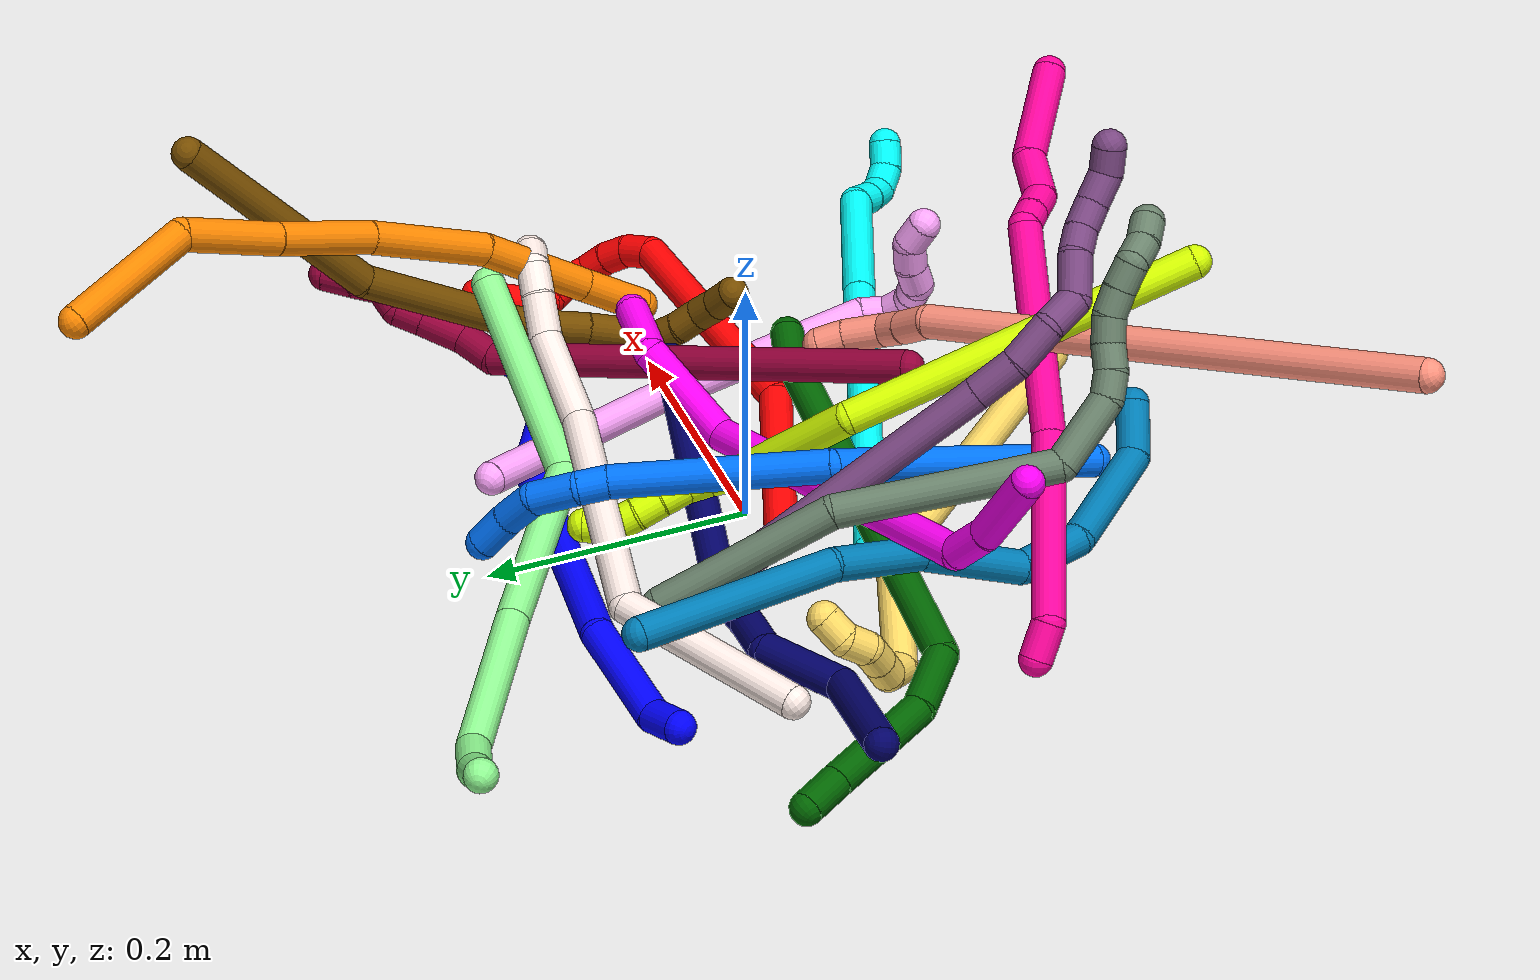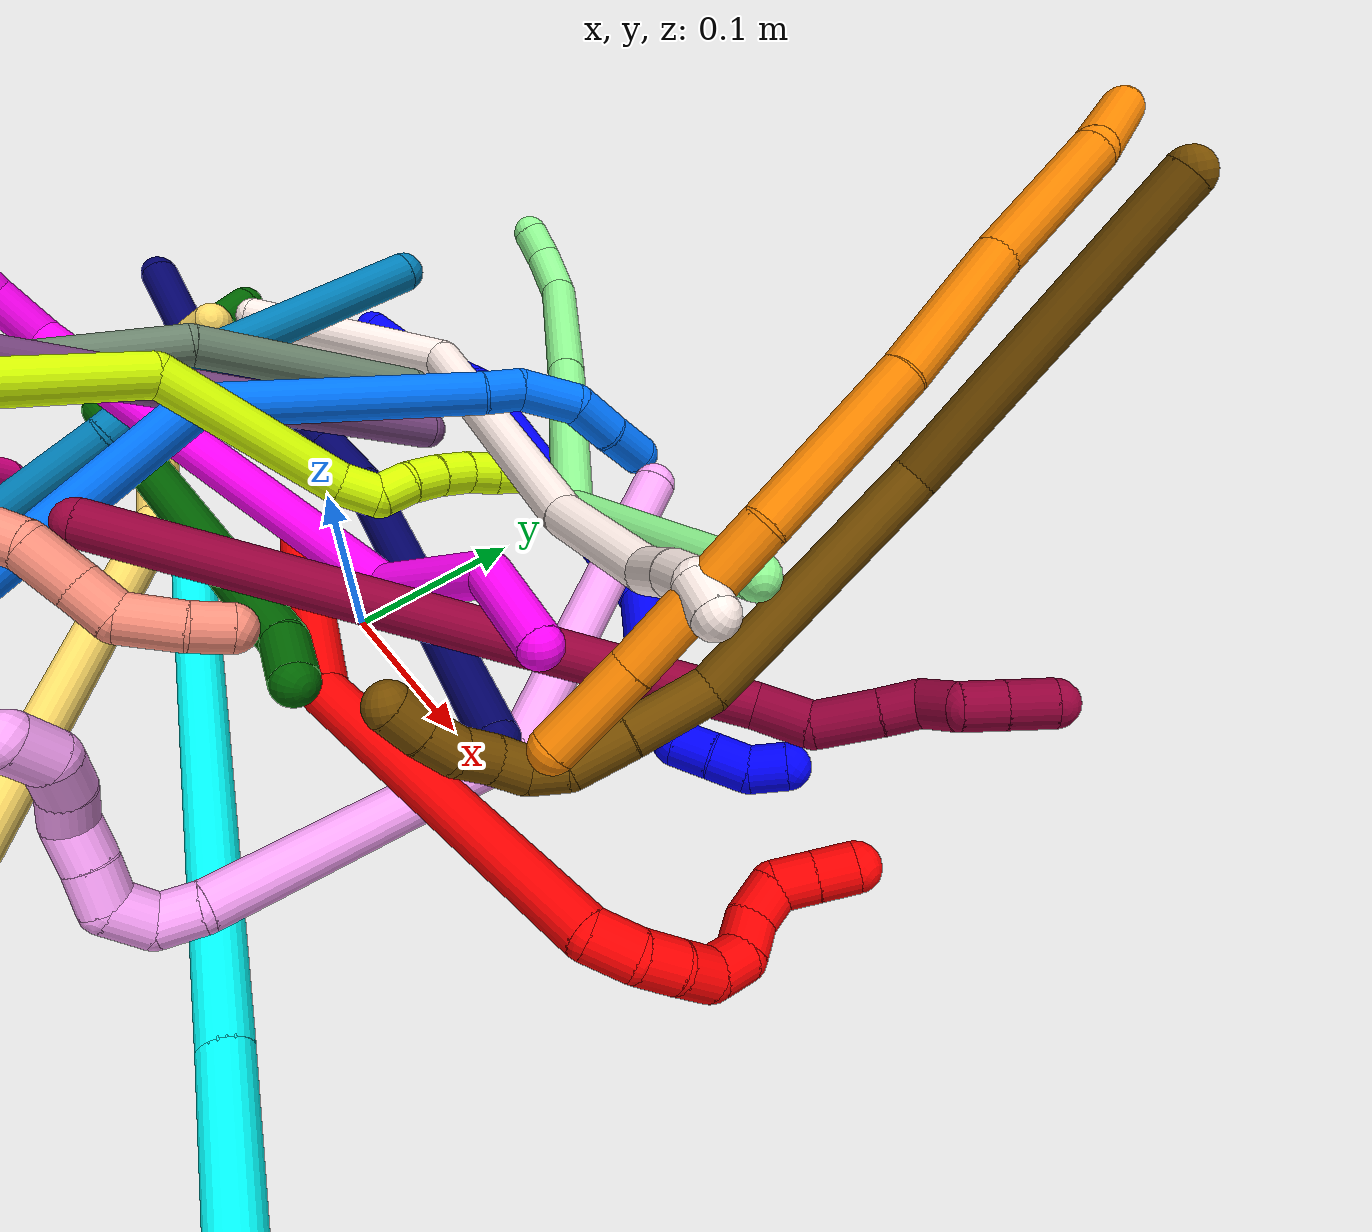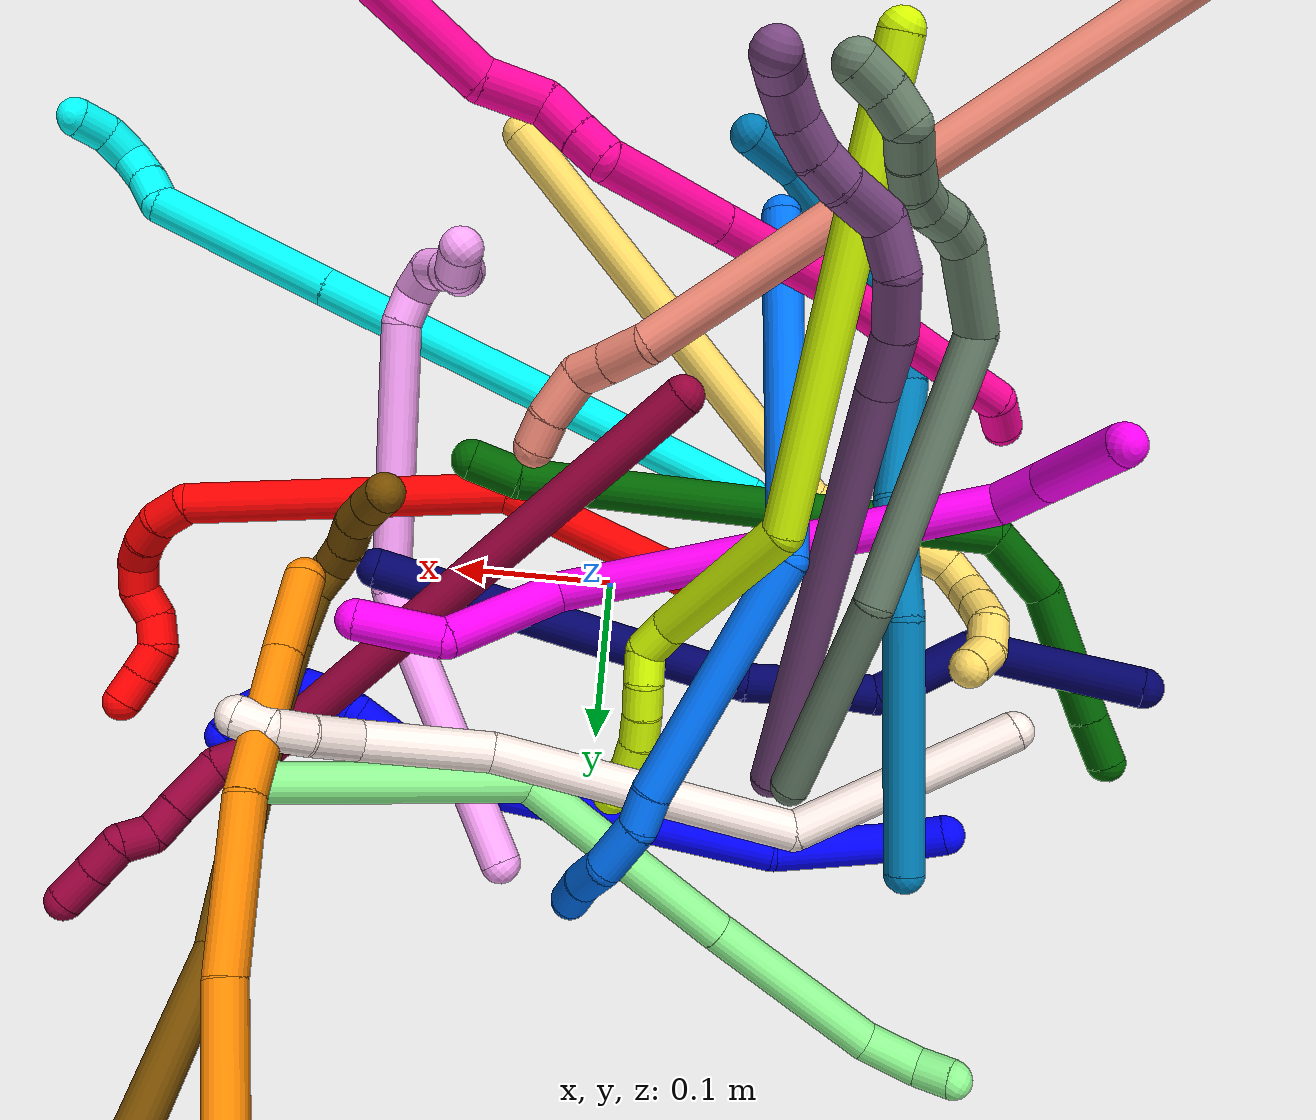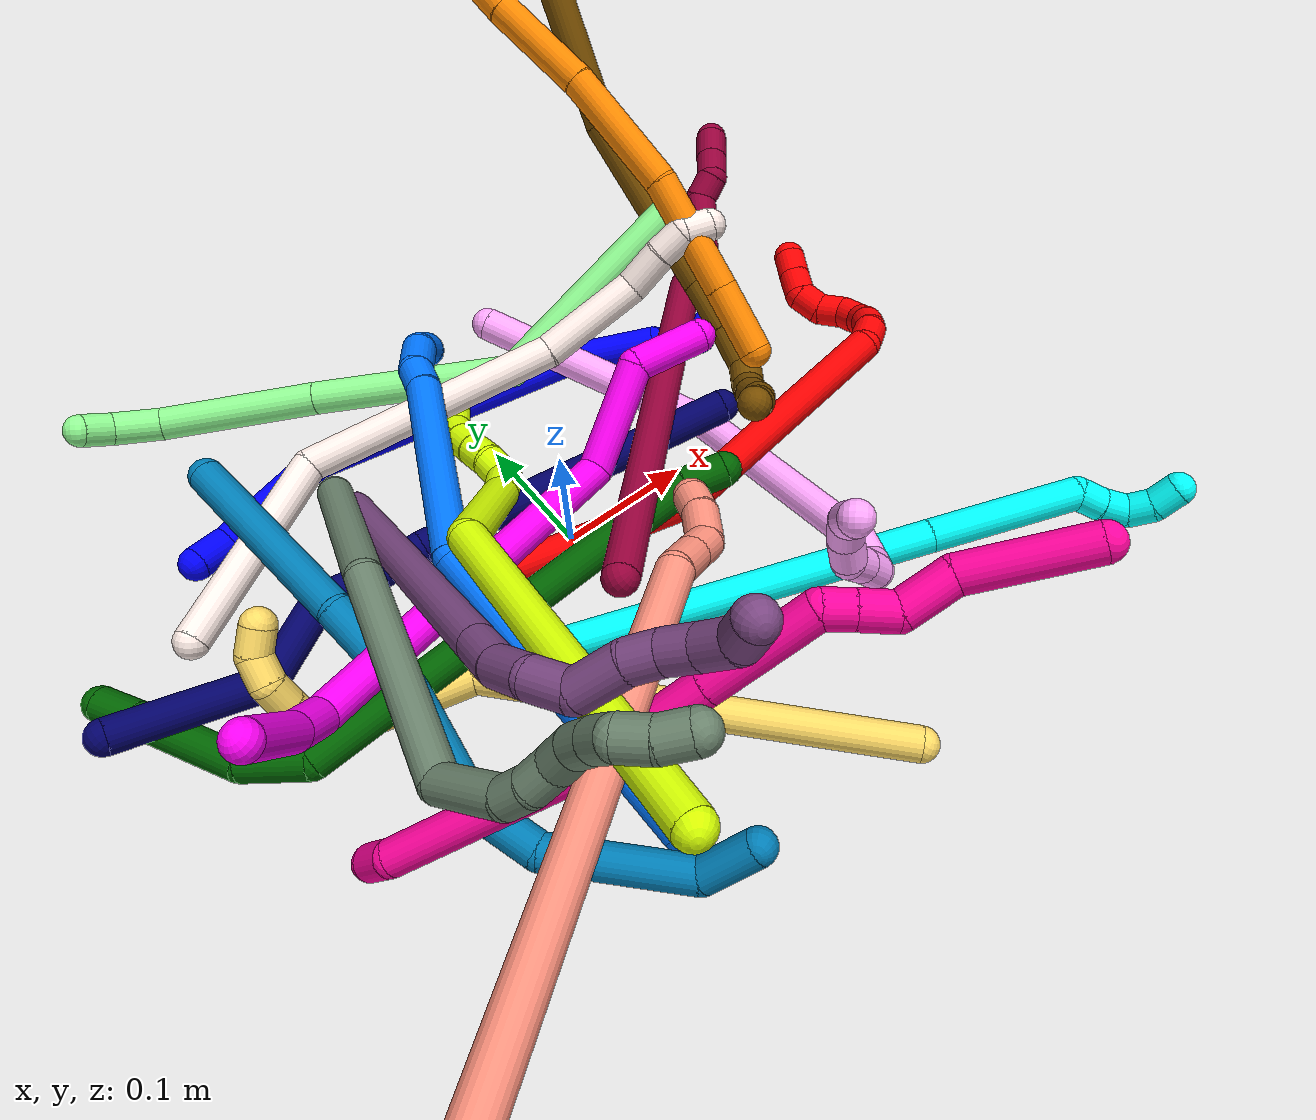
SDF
<sdf version="1.7">
 <world name="default">
  <plugin name="TubeGeneratorPlugin" filename="libtube_generator_plugin.so"/>
  <model name="photoneo_s_sensor">
   <static>1</static>
   <pose>0 0 2 1.57079 1.57079 3.14159</pose>
   <link name="link">
    <inertial><mass>0.1</mass></inertial>
    <sensor name="sensor" type="depth">
     <update_rate>30</update_rate>
     <camera>
      <horizontal_fov>1.22</horizontal_fov>
      <image><width>1920</width><height>1200</height><format>B8G8R8</format></image>
      <clip><near>0.1</near><far>4</far></clip>
      <depth_camera><output>points</output></depth_camera>
     </camera>
     <plugin name="camera_plugin" filename="libgazebo_ros_depth_camera.so">
      <baseline>0.2</baseline>
      <alwaysOn>1</alwaysOn>
      <updateRate>0.0</updateRate>
      <cameraName>camera_ir</cameraName>
      <imageTopicName>/camera/color/image_raw</imageTopicName>
      <cameraInfoTopicName>/camera/color/camera_info</cameraInfoTopicName>
      <depthImageTopicName>/camera/depth/image_raw</depthImageTopicName>
      <depthImageCameraInfoTopicName>/camera/depth/camera_info</depthImageCameraInfoTopicName>
      <pointCloudTopicName>/camera/depth/points</pointCloudTopicName>
      <frameName>fr_optical</frameName>
      <pointCloudCutoff>0.1</pointCloudCutoff>
      <pointCloudCutoffMax>2.0</pointCloudCutoffMax>
      <distortionK1>0</distortionK1>
      <distortionK2>0</distortionK2>
      <distortionK3>0</distortionK3>
      <distortionT1>0</distortionT1>
      <distortionT2>0</distortionT2>
      <CxPrime>0</CxPrime>
      <Cx>0</Cx>
      <Cy>0</Cy>
      <focalLength>0</focalLength>
      <hackBaseline>0</hackBaseline>
     </plugin>
    </sensor>
   </link>
  </model>
  <gravity>0 0 -9.8</gravity>
  <magnetic_field>6e-06 2.3e-05 -4.2e-05</magnetic_field>
  <atmosphere type="adiabatic"/>
  <physics name="default_physics" default="0" type="ode">
   <max_step_size>0.003</max_step_size>
   <real_time_factor>1</real_time_factor>
   <real_time_update_rate>1000</real_time_update_rate>
   <max_contacts>10000</max_contacts>
   <ode>
    <solver>
     <type>quick</type>
     <iters>100</iters>
     <sor>1.3</sor>
     <use_dynamic_moi_rescaling>0</use_dynamic_moi_rescaling>
    </solver>
    <constraints>
     <contact_max_correcting_vel>0</contact_max_correcting_vel>
     <contact_surface_layer>0.001</contact_surface_layer>
     <cfm>0</cfm>
     <erp>0.2</erp>
    </constraints>
   </ode>
  </physics>
  <scene><ambient>0.4 0.4 0.4 1</ambient><background>0.7 0.7 0.7 1</background><shadows>0</shadows></scene>
  <audio><device>default</device></audio>
  <spherical_coordinates>
   <surface_model>EARTH_WGS84</surface_model>
   <latitude_deg>0</latitude_deg>
   <longitude_deg>0</longitude_deg>
   <elevation>0</elevation>
   <heading_deg>0</heading_deg>
  </spherical_coordinates>
  <model name="bin">
   <static>1</static>
   <link name="bottom">
    <collision name="collision-bottom">
     <pose>0 0 -0.01 0 -0 0</pose>
     <geometry><box><size>0.8 0.6 0.02</size></box></geometry>
     <surface>
      <friction><ode><mu>100</mu><mu2>100</mu2></ode></friction>
      <contact><collide_bitmask>65535</collide_bitmask></contact>
     </surface>
    </collision>
   </link>
   <link name="west_wall">
    <collision name="collision-west_wall">
     <pose>-0.41 0 0.1 0 -0 0</pose>
     <geometry><box><size>0.02 0.6 0.2</size></box></geometry>
     <surface>
      <friction><ode><mu>100</mu><mu2>100</mu2></ode></friction>
      <contact><collide_bitmask>65535</collide_bitmask></contact>
     </surface>
    </collision>
   </link>
   <link name="east_wall">
    <collision name="collision-east_wall">
     <pose>0.41 0 0.1 0 -0 0</pose>
     <geometry><box><size>0.02 0.6 0.2</size></box></geometry>
     <surface>
      <friction><ode><mu>100</mu><mu2>100</mu2></ode></friction>
      <contact><collide_bitmask>65535</collide_bitmask></contact>
     </surface>
    </collision>
   </link>
   <link name="south_wall">
    <collision name="collision-south_wall">
     <pose>0 -0.31 0.1 0 -0 0</pose>
     <geometry><box><size>0.8 0.02 0.2</size></box></geometry>
     <surface>
      <friction><ode><mu>100</mu><mu2>100</mu2></ode></friction>
      <contact><collide_bitmask>65535</collide_bitmask></contact>
     </surface>
    </collision>
   </link>
   <link name="north_wall">
    <collision name="collision-north_wall">
     <pose>0 0.31 0.1 0 -0 0</pose>
     <geometry><box><size>0.8 0.02 0.2</size></box></geometry>
     <surface>
      <friction><ode><mu>100</mu><mu2>100</mu2></ode></friction>
      <contact><collide_bitmask>65535</collide_bitmask></contact>
     </surface>
    </collision>
   </link>
  </model>
  <model name="1">
   <static>0</static>
   <link name="1">
    <collision name="collision-cylinder-e_1_1_4">
     <pose>0.000406 -0.000487 -0.014796 3.10866 0.027416 1.38844</pose>
     <geometry><cylinder><radius>0.0125</radius><length>0.029619</length></cylinder></geometry>
     <surface>
      <friction><ode><mu>1.16</mu><mu2>1.16</mu2><slip1>0</slip1><slip2>0</slip2></ode></friction>
      <contact><ode><kp>1e+06</kp><kd>1</kd><max_vel>0</max_vel><min_depth>0.001</min_depth></ode></contact>
     </surface>
    </collision>
    <visual name="visual-cylinder-e_1_1_4">
     <pose>0.000406 -0.000487 -0.014796 3.10866 0.027416 1.38844</pose>
     <geometry><cylinder><radius>0.0125</radius><length>0.029619</length></cylinder></geometry>
     <material><ambient>0 0 1 1</ambient></material>
    </visual>
    <collision name="collision-cylinder-e_2_4_5">
     <pose>0.020417 0.004562 -0.066507 -2.99271 0.483622 -2.55431</pose>
     <geometry><cylinder><radius>0.0125</radius><length>0.084326</length></cylinder></geometry>
     <surface>
      <friction><ode><mu>1.16</mu><mu2>1.16</mu2><slip1>0</slip1><slip2>0</slip2></ode></friction>
      <contact><ode><kp>1e+06</kp><kd>1</kd><max_vel>0</max_vel><min_depth>0.001</min_depth></ode></contact>
     </surface>
    </collision>
    <visual name="visual-cylinder-e_2_4_5">
     <pose>0.020417 0.004562 -0.066507 -2.99271 0.483622 -2.55431</pose>
     <geometry><cylinder><radius>0.0125</radius><length>0.084326</length></cylinder></geometry>
     <material><ambient>0 0 1 1</ambient></material>
    </visual>
    <collision name="collision-cylinder-e_3_5_6">
     <pose>0.08765 -0.012303 -0.197232 2.90718 0.458686 2.20732</pose>
     <geometry><cylinder><radius>0.0125</radius><length>0.215134</length></cylinder></geometry>
     <surface>
      <friction><ode><mu>1.16</mu><mu2>1.16</mu2><slip1>0</slip1><slip2>0</slip2></ode></friction>
      <contact><ode><kp>1e+06</kp><kd>1</kd><max_vel>0</max_vel><min_depth>0.001</min_depth></ode></contact>
     </surface>
    </collision>
    <visual name="visual-cylinder-e_3_5_6">
     <pose>0.08765 -0.012303 -0.197232 2.90718 0.458686 2.20732</pose>
     <geometry><cylinder><radius>0.0125</radius><length>0.215134</length></cylinder></geometry>
     <material><ambient>0 0 1 1</ambient></material>
    </visual>
    <collision name="collision-cylinder-e_4_6_7">
     <pose>0.163222 -0.046512 -0.308187 2.53851 0.930559 2.03229</pose>
     <geometry><cylinder><radius>0.0125</radius><length>0.069691</length></cylinder></geometry>
     <surface>
      <friction><ode><mu>1.16</mu><mu2>1.16</mu2><slip1>0</slip1><slip2>0</slip2></ode></friction>
      <contact><ode><kp>1e+06</kp><kd>1</kd><max_vel>0</max_vel><min_depth>0.001</min_depth></ode></contact>
     </surface>
    </collision>
    <visual name="visual-cylinder-e_4_6_7">
     <pose>0.163222 -0.046512 -0.308187 2.53851 0.930559 2.03229</pose>
     <geometry><cylinder><radius>0.0125</radius><length>0.069691</length></cylinder></geometry>
     <material><ambient>0 0 1 1</ambient></material>
    </visual>
    <collision name="collision-cylinder-e_5_7_8">
     <pose>0.194168 -0.064505 -0.333002 2.46289 0.295678 0.798445</pose>
     <geometry><cylinder><radius>0.0125</radius><length>0.020603</length></cylinder></geometry>
     <surface>
      <friction><ode><mu>1.16</mu><mu2>1.16</mu2><slip1>0</slip1><slip2>0</slip2></ode></friction>
      <contact><ode><kp>1e+06</kp><kd>1</kd><max_vel>0</max_vel><min_depth>0.001</min_depth></ode></contact>
     </surface>
    </collision>
    <visual name="visual-cylinder-e_5_7_8">
     <pose>0.194168 -0.064505 -0.333002 2.46289 0.295678 0.798445</pose>
     <geometry><cylinder><radius>0.0125</radius><length>0.020603</length></cylinder></geometry>
     <material><ambient>0 0 1 1</ambient></material>
    </visual>
    <collision name="collision-cylinder-e_6_8_9">
     <pose>0.201821 -0.073927 -0.349221 2.77975 0.470676 1.83821</pose>
     <geometry><cylinder><radius>0.0125</radius><length>0.020512</length></cylinder></geometry>
     <surface>
      <friction><ode><mu>1.16</mu><mu2>1.16</mu2><slip1>0</slip1><slip2>0</slip2></ode></friction>
      <contact><ode><kp>1e+06</kp><kd>1</kd><max_vel>0</max_vel><min_depth>0.001</min_depth></ode></contact>
     </surface>
    </collision>
    <visual name="visual-cylinder-e_6_8_9">
     <pose>0.201821 -0.073927 -0.349221 2.77975 0.470676 1.83821</pose>
     <geometry><cylinder><radius>0.0125</radius><length>0.020512</length></cylinder></geometry>
     <material><ambient>0 0 1 1</ambient></material>
    </visual>
    <collision name="collision-cylinder-e_7_9_10">
     <pose>0.207519 -0.074418 -0.367369 -2.86305 0.104484 -0.71406</pose>
     <geometry><cylinder><radius>0.0125</radius><length>0.020077</length></cylinder></geometry>
     <surface>
      <friction><ode><mu>1.16</mu><mu2>1.16</mu2><slip1>0</slip1><slip2>0</slip2></ode></friction>
      <contact><ode><kp>1e+06</kp><kd>1</kd><max_vel>0</max_vel><min_depth>0.001</min_depth></ode></contact>
     </surface>
    </collision>
    <visual name="visual-cylinder-e_7_9_10">
     <pose>0.207519 -0.074418 -0.367369 -2.86305 0.104484 -0.71406</pose>
     <geometry><cylinder><radius>0.0125</radius><length>0.020077</length></cylinder></geometry>
     <material><ambient>0 0 1 1</ambient></material>
    </visual>
    <collision name="collision-cylinder-e_8_10_11">
     <pose>0.208477 -0.069186 -0.386668 -2.89065 -0.008925 0.070733</pose>
     <geometry><cylinder><radius>0.0125</radius><length>0.020028</length></cylinder></geometry>
     <surface>
      <friction><ode><mu>1.16</mu><mu2>1.16</mu2><slip1>0</slip1><slip2>0</slip2></ode></friction>
      <contact><ode><kp>1e+06</kp><kd>1</kd><max_vel>0</max_vel><min_depth>0.001</min_depth></ode></contact>
     </surface>
    </collision>
    <visual name="visual-cylinder-e_8_10_11">
     <pose>0.208477 -0.069186 -0.386668 -2.89065 -0.008925 0.070733</pose>
     <geometry><cylinder><radius>0.0125</radius><length>0.020028</length></cylinder></geometry>
     <material><ambient>0 0 1 1</ambient></material>
    </visual>
    <collision name="collision-cylinder-e_9_11_2">
     <pose>0.207745 -0.060261 -0.403998 -2.44067 -0.06426 0.175401</pose>
     <geometry><cylinder><radius>0.0125</radius><length>0.020009</length></cylinder></geometry>
     <surface>
      <friction><ode><mu>1.16</mu><mu2>1.16</mu2><slip1>0</slip1><slip2>0</slip2></ode></friction>
      <contact><ode><kp>1e+06</kp><kd>1</kd><max_vel>0</max_vel><min_depth>0.001</min_depth></ode></contact>
     </surface>
    </collision>
    <visual name="visual-cylinder-e_9_11_2">
     <pose>0.207745 -0.060261 -0.403998 -2.44067 -0.06426 0.175401</pose>
     <geometry><cylinder><radius>0.0125</radius><length>0.020009</length></cylinder></geometry>
     <material><ambient>0 0 1 1</ambient></material>
    </visual>
    <collision name="collision-sphere-2">
     <pose>0.207103 -0.053822 -0.411628 0 -0 0</pose>
     <geometry><sphere><radius>0.0125</radius></sphere></geometry>
     <surface>
      <friction><ode><mu>1.16</mu><mu2>1.16</mu2><slip1>0</slip1><slip2>0</slip2></ode></friction>
      <contact><ode><kp>1e+06</kp><kd>1</kd><max_vel>0</max_vel><min_depth>0.001</min_depth></ode></contact>
     </surface>
    </collision>
    <visual name="visual-sphere-2">
     <pose>0.207103 -0.053822 -0.411628 0 -0 0</pose>
     <geometry><sphere><radius>0.0125</radius></sphere></geometry>
     <material><ambient>0 0 1 1</ambient></material>
    </visual>
    <collision name="collision-sphere-11">
     <pose>0.208387 -0.0667 -0.396368 0 -0 0</pose>
     <geometry><sphere><radius>0.0125</radius></sphere></geometry>
     <surface>
      <friction><ode><mu>1.16</mu><mu2>1.16</mu2><slip1>0</slip1><slip2>0</slip2></ode></friction>
      <contact><ode><kp>1e+06</kp><kd>1</kd><max_vel>0</max_vel><min_depth>0.001</min_depth></ode></contact>
     </surface>
    </collision>
    <visual name="visual-sphere-11">
     <pose>0.208387 -0.0667 -0.396368 0 -0 0</pose>
     <geometry><sphere><radius>0.0125</radius></sphere></geometry>
     <material><ambient>0 0 1 1</ambient></material>
    </visual>
    <collision name="collision-sphere-10">
     <pose>0.208566 -0.071673 -0.376968 0 -0 0</pose>
     <geometry><sphere><radius>0.0125</radius></sphere></geometry>
     <surface>
      <friction><ode><mu>1.16</mu><mu2>1.16</mu2><slip1>0</slip1><slip2>0</slip2></ode></friction>
      <contact><ode><kp>1e+06</kp><kd>1</kd><max_vel>0</max_vel><min_depth>0.001</min_depth></ode></contact>
     </surface>
    </collision>
    <visual name="visual-sphere-10">
     <pose>0.208566 -0.071673 -0.376968 0 -0 0</pose>
     <geometry><sphere><radius>0.0125</radius></sphere></geometry>
     <material><ambient>0 0 1 1</ambient></material>
    </visual>
    <collision name="collision-sphere-9">
     <pose>0.206472 -0.077163 -0.35777 0 -0 0</pose>
     <geometry><sphere><radius>0.0125</radius></sphere></geometry>
     <surface>
      <friction><ode><mu>1.16</mu><mu2>1.16</mu2><slip1>0</slip1><slip2>0</slip2></ode></friction>
      <contact><ode><kp>1e+06</kp><kd>1</kd><max_vel>0</max_vel><min_depth>0.001</min_depth></ode></contact>
     </surface>
    </collision>
    <visual name="visual-sphere-9">
     <pose>0.206472 -0.077163 -0.35777 0 -0 0</pose>
     <geometry><sphere><radius>0.0125</radius></sphere></geometry>
     <material><ambient>0 0 1 1</ambient></material>
    </visual>
    <collision name="collision-sphere-4">
     <pose>0.000812 -0.000975 -0.029592 0 -0 0</pose>
     <geometry><sphere><radius>0.0125</radius></sphere></geometry>
     <surface>
      <friction><ode><mu>1.16</mu><mu2>1.16</mu2><slip1>0</slip1><slip2>0</slip2></ode></friction>
      <contact><ode><kp>1e+06</kp><kd>1</kd><max_vel>0</max_vel><min_depth>0.001</min_depth></ode></contact>
     </surface>
    </collision>
    <visual name="visual-sphere-4">
     <pose>0.000812 -0.000975 -0.029592 0 -0 0</pose>
     <geometry><sphere><radius>0.0125</radius></sphere></geometry>
     <material><ambient>0 0 1 1</ambient></material>
    </visual>
    <collision name="collision-sphere-1">
     <geometry><sphere><radius>0.0125</radius></sphere></geometry>
     <surface>
      <friction><ode><mu>1.16</mu><mu2>1.16</mu2><slip1>0</slip1><slip2>0</slip2></ode></friction>
      <contact><ode><kp>1e+06</kp><kd>1</kd><max_vel>0</max_vel><min_depth>0.001</min_depth></ode></contact>
     </surface>
    </collision>
    <visual name="visual-sphere-1">
     <geometry><sphere><radius>0.0125</radius></sphere></geometry>
     <material><ambient>0 0 1 1</ambient></material>
    </visual>
    <collision name="collision-sphere-8">
     <pose>0.19717 -0.070692 -0.340672 0 -0 0</pose>
     <geometry><sphere><radius>0.0125</radius></sphere></geometry>
     <surface>
      <friction><ode><mu>1.16</mu><mu2>1.16</mu2><slip1>0</slip1><slip2>0</slip2></ode></friction>
      <contact><ode><kp>1e+06</kp><kd>1</kd><max_vel>0</max_vel><min_depth>0.001</min_depth></ode></contact>
     </surface>
    </collision>
    <visual name="visual-sphere-8">
     <pose>0.19717 -0.070692 -0.340672 0 -0 0</pose>
     <geometry><sphere><radius>0.0125</radius></sphere></geometry>
     <material><ambient>0 0 1 1</ambient></material>
    </visual>
    <collision name="collision-sphere-5">
     <pose>0.040023 0.010099 -0.103422 0 -0 0</pose>
     <geometry><sphere><radius>0.0125</radius></sphere></geometry>
     <surface>
      <friction><ode><mu>1.16</mu><mu2>1.16</mu2><slip1>0</slip1><slip2>0</slip2></ode></friction>
      <contact><ode><kp>1e+06</kp><kd>1</kd><max_vel>0</max_vel><min_depth>0.001</min_depth></ode></contact>
     </surface>
    </collision>
    <visual name="visual-sphere-5">
     <pose>0.040023 0.010099 -0.103422 0 -0 0</pose>
     <geometry><sphere><radius>0.0125</radius></sphere></geometry>
     <material><ambient>0 0 1 1</ambient></material>
    </visual>
    <collision name="collision-sphere-6">
     <pose>0.135278 -0.034705 -0.291043 0 -0 0</pose>
     <geometry><sphere><radius>0.0125</radius></sphere></geometry>
     <surface>
      <friction><ode><mu>1.16</mu><mu2>1.16</mu2><slip1>0</slip1><slip2>0</slip2></ode></friction>
      <contact><ode><kp>1e+06</kp><kd>1</kd><max_vel>0</max_vel><min_depth>0.001</min_depth></ode></contact>
     </surface>
    </collision>
    <visual name="visual-sphere-6">
     <pose>0.135278 -0.034705 -0.291043 0 -0 0</pose>
     <geometry><sphere><radius>0.0125</radius></sphere></geometry>
     <material><ambient>0 0 1 1</ambient></material>
    </visual>
    <collision name="collision-sphere-7">
     <pose>0.191167 -0.058318 -0.325331 0 -0 0</pose>
     <geometry><sphere><radius>0.0125</radius></sphere></geometry>
     <surface>
      <friction><ode><mu>1.16</mu><mu2>1.16</mu2><slip1>0</slip1><slip2>0</slip2></ode></friction>
      <contact><ode><kp>1e+06</kp><kd>1</kd><max_vel>0</max_vel><min_depth>0.001</min_depth></ode></contact>
     </surface>
    </collision>
    <visual name="visual-sphere-7">
     <pose>0.191167 -0.058318 -0.325331 0 -0 0</pose>
     <geometry><sphere><radius>0.0125</radius></sphere></geometry>
     <material><ambient>0 0 1 1</ambient></material>
    </visual>
    <inertial>
     <pose>0.105208 -0.024898 -0.214367 0 -0 0</pose>
     <mass>0.5</mass>
     <inertia>
      <ixx>0.000127</ixx>
      <ixy>0</ixy>
      <ixz>0</ixz>
      <iyy>0.001215</iyy>
      <iyz>0</iyz>
      <izz>-0.000276</izz>
     </inertia>
    </inertial>
   </link>
   <pose>-0.227113 0.139582 0.020349 1.16789 -0.779089 -0.92576</pose>
  </model>
  <model name="2">
   <static>0</static>
   <link name="2">
    <collision name="collision-cylinder-e_1_1_4">
     <pose>0.027513 -0.011588 0.063522 0.180439 0.402797 0.036936</pose>
     <geometry><cylinder><radius>0.0125</radius><length>0.140375</length></cylinder></geometry>
     <surface>
      <friction><ode><mu>1.16</mu><mu2>1.16</mu2><slip1>0</slip1><slip2>0</slip2></ode></friction>
      <contact><ode><kp>1e+06</kp><kd>1</kd><max_vel>0</max_vel><min_depth>0.001</min_depth></ode></contact>
     </surface>
    </collision>
    <visual name="visual-cylinder-e_1_1_4">
     <pose>0.027513 -0.011588 0.063522 0.180439 0.402797 0.036936</pose>
     <geometry><cylinder><radius>0.0125</radius><length>0.140375</length></cylinder></geometry>
     <material><ambient>1 0 0 1</ambient></material>
    </visual>
    <collision name="collision-cylinder-e_2_4_5">
     <pose>0.054863 -0.012601 0.224173 -0.10845 -0.001672 9.1e-05</pose>
     <geometry><cylinder><radius>0.0125</radius><length>0.195407</length></cylinder></geometry>
     <surface>
      <friction><ode><mu>1.16</mu><mu2>1.16</mu2><slip1>0</slip1><slip2>0</slip2></ode></friction>
      <contact><ode><kp>1e+06</kp><kd>1</kd><max_vel>0</max_vel><min_depth>0.001</min_depth></ode></contact>
     </surface>
    </collision>
    <visual name="visual-cylinder-e_2_4_5">
     <pose>0.054863 -0.012601 0.224173 -0.10845 -0.001672 9.1e-05</pose>
     <geometry><cylinder><radius>0.0125</radius><length>0.195407</length></cylinder></geometry>
     <material><ambient>1 0 0 1</ambient></material>
    </visual>
    <collision name="collision-cylinder-e_3_5_6">
     <pose>0.051023 0.004199 0.330494 -0.595244 -0.31981 0.09886</pose>
     <geometry><cylinder><radius>0.0125</radius><length>0.023388</length></cylinder></geometry>
     <surface>
      <friction><ode><mu>1.16</mu><mu2>1.16</mu2><slip1>0</slip1><slip2>0</slip2></ode></friction>
      <contact><ode><kp>1e+06</kp><kd>1</kd><max_vel>0</max_vel><min_depth>0.001</min_depth></ode></contact>
     </surface>
    </collision>
    <visual name="visual-cylinder-e_3_5_6">
     <pose>0.051023 0.004199 0.330494 -0.595244 -0.31981 0.09886</pose>
     <geometry><cylinder><radius>0.0125</radius><length>0.023388</length></cylinder></geometry>
     <material><ambient>1 0 0 1</ambient></material>
    </visual>
    <collision name="collision-cylinder-e_4_6_7">
     <pose>0.0431 0.01813 0.34488 -0.977804 -0.428588 0.230528</pose>
     <geometry><cylinder><radius>0.0125</radius><length>0.020435</length></cylinder></geometry>
     <surface>
      <friction><ode><mu>1.16</mu><mu2>1.16</mu2><slip1>0</slip1><slip2>0</slip2></ode></friction>
      <contact><ode><kp>1e+06</kp><kd>1</kd><max_vel>0</max_vel><min_depth>0.001</min_depth></ode></contact>
     </surface>
    </collision>
    <visual name="visual-cylinder-e_4_6_7">
     <pose>0.0431 0.01813 0.34488 -0.977804 -0.428588 0.230528</pose>
     <geometry><cylinder><radius>0.0125</radius><length>0.020435</length></cylinder></geometry>
     <material><ambient>1 0 0 1</ambient></material>
    </visual>
    <collision name="collision-cylinder-e_5_7_8">
     <pose>0.035002 0.034515 0.353246 -1.22029 -0.395024 0.278019</pose>
     <geometry><cylinder><radius>0.0125</radius><length>0.02002</length></cylinder></geometry>
     <surface>
      <friction><ode><mu>1.16</mu><mu2>1.16</mu2><slip1>0</slip1><slip2>0</slip2></ode></friction>
      <contact><ode><kp>1e+06</kp><kd>1</kd><max_vel>0</max_vel><min_depth>0.001</min_depth></ode></contact>
     </surface>
    </collision>
    <visual name="visual-cylinder-e_5_7_8">
     <pose>0.035002 0.034515 0.353246 -1.22029 -0.395024 0.278019</pose>
     <geometry><cylinder><radius>0.0125</radius><length>0.02002</length></cylinder></geometry>
     <material><ambient>1 0 0 1</ambient></material>
    </visual>
    <collision name="collision-cylinder-e_6_8_9">
     <pose>0.02307 0.049292 0.356631 -1.53601 -0.923798 0.896325</pose>
     <geometry><cylinder><radius>0.0125</radius><length>0.020252</length></cylinder></geometry>
     <surface>
      <friction><ode><mu>1.16</mu><mu2>1.16</mu2><slip1>0</slip1><slip2>0</slip2></ode></friction>
      <contact><ode><kp>1e+06</kp><kd>1</kd><max_vel>0</max_vel><min_depth>0.001</min_depth></ode></contact>
     </surface>
    </collision>
    <visual name="visual-cylinder-e_6_8_9">
     <pose>0.02307 0.049292 0.356631 -1.53601 -0.923798 0.896325</pose>
     <geometry><cylinder><radius>0.0125</radius><length>0.020252</length></cylinder></geometry>
     <material><ambient>1 0 0 1</ambient></material>
    </visual>
    <collision name="collision-cylinder-e_7_9_10">
     <pose>0.006801 0.058241 0.351852 -2.62303 -0.958901 2.19807</pose>
     <geometry><cylinder><radius>0.0125</radius><length>0.020009</length></cylinder></geometry>
     <surface>
      <friction><ode><mu>1.16</mu><mu2>1.16</mu2><slip1>0</slip1><slip2>0</slip2></ode></friction>
      <contact><ode><kp>1e+06</kp><kd>1</kd><max_vel>0</max_vel><min_depth>0.001</min_depth></ode></contact>
     </surface>
    </collision>
    <visual name="visual-cylinder-e_7_9_10">
     <pose>0.006801 0.058241 0.351852 -2.62303 -0.958901 2.19807</pose>
     <geometry><cylinder><radius>0.0125</radius><length>0.020009</length></cylinder></geometry>
     <material><ambient>1 0 0 1</ambient></material>
    </visual>
    <collision name="collision-cylinder-e_8_10_11">
     <pose>-0.011347 0.061697 0.345639 -2.67963 -1.4347 2.61495</pose>
     <geometry><cylinder><radius>0.0125</radius><length>0.020103</length></cylinder></geometry>
     <surface>
      <friction><ode><mu>1.16</mu><mu2>1.16</mu2><slip1>0</slip1><slip2>0</slip2></ode></friction>
      <contact><ode><kp>1e+06</kp><kd>1</kd><max_vel>0</max_vel><min_depth>0.001</min_depth></ode></contact>
     </surface>
    </collision>
    <visual name="visual-cylinder-e_8_10_11">
     <pose>-0.011347 0.061697 0.345639 -2.67963 -1.4347 2.61495</pose>
     <geometry><cylinder><radius>0.0125</radius><length>0.020103</length></cylinder></geometry>
     <material><ambient>1 0 0 1</ambient></material>
    </visual>
    <collision name="collision-cylinder-e_9_11_12">
     <pose>-0.029478 0.06444 0.34978 -0.378973 -0.955947 0.198056</pose>
     <geometry><cylinder><radius>0.0125</radius><length>0.020009</length></cylinder></geometry>
     <surface>
      <friction><ode><mu>1.16</mu><mu2>1.16</mu2><slip1>0</slip1><slip2>0</slip2></ode></friction>
      <contact><ode><kp>1e+06</kp><kd>1</kd><max_vel>0</max_vel><min_depth>0.001</min_depth></ode></contact>
     </surface>
    </collision>
    <visual name="visual-cylinder-e_9_11_12">
     <pose>-0.029478 0.06444 0.34978 -0.378973 -0.955947 0.198056</pose>
     <geometry><cylinder><radius>0.0125</radius><length>0.020009</length></cylinder></geometry>
     <material><ambient>1 0 0 1</ambient></material>
    </visual>
    <collision name="collision-cylinder-e_10_12_2">
     <pose>-0.045762 0.068269 0.360739 -0.293814 -0.946145 0.151188</pose>
     <geometry><cylinder><radius>0.0125</radius><length>0.020001</length></cylinder></geometry>
     <surface>
      <friction><ode><mu>1.16</mu><mu2>1.16</mu2><slip1>0</slip1><slip2>0</slip2></ode></friction>
      <contact><ode><kp>1e+06</kp><kd>1</kd><max_vel>0</max_vel><min_depth>0.001</min_depth></ode></contact>
     </surface>
    </collision>
    <visual name="visual-cylinder-e_10_12_2">
     <pose>-0.045762 0.068269 0.360739 -0.293814 -0.946145 0.151188</pose>
     <geometry><cylinder><radius>0.0125</radius><length>0.020001</length></cylinder></geometry>
     <material><ambient>1 0 0 1</ambient></material>
    </visual>
    <collision name="collision-sphere-2">
     <pose>-0.053874 0.069963 0.366337 0 -0 0</pose>
     <geometry><sphere><radius>0.0125</radius></sphere></geometry>
     <surface>
      <friction><ode><mu>1.16</mu><mu2>1.16</mu2><slip1>0</slip1><slip2>0</slip2></ode></friction>
      <contact><ode><kp>1e+06</kp><kd>1</kd><max_vel>0</max_vel><min_depth>0.001</min_depth></ode></contact>
     </surface>
    </collision>
    <visual name="visual-sphere-2">
     <pose>-0.053874 0.069963 0.366337 0 -0 0</pose>
     <geometry><sphere><radius>0.0125</radius></sphere></geometry>
     <material><ambient>1 0 0 1</ambient></material>
    </visual>
    <collision name="collision-sphere-12">
     <pose>-0.03765 0.066575 0.355142 0 -0 0</pose>
     <geometry><sphere><radius>0.0125</radius></sphere></geometry>
     <surface>
      <friction><ode><mu>1.16</mu><mu2>1.16</mu2><slip1>0</slip1><slip2>0</slip2></ode></friction>
      <contact><ode><kp>1e+06</kp><kd>1</kd><max_vel>0</max_vel><min_depth>0.001</min_depth></ode></contact>
     </surface>
    </collision>
    <visual name="visual-sphere-12">
     <pose>-0.03765 0.066575 0.355142 0 -0 0</pose>
     <geometry><sphere><radius>0.0125</radius></sphere></geometry>
     <material><ambient>1 0 0 1</ambient></material>
    </visual>
    <collision name="collision-sphere-11">
     <pose>-0.021306 0.062305 0.344419 0 -0 0</pose>
     <geometry><sphere><radius>0.0125</radius></sphere></geometry>
     <surface>
      <friction><ode><mu>1.16</mu><mu2>1.16</mu2><slip1>0</slip1><slip2>0</slip2></ode></friction>
      <contact><ode><kp>1e+06</kp><kd>1</kd><max_vel>0</max_vel><min_depth>0.001</min_depth></ode></contact>
     </surface>
    </collision>
    <visual name="visual-sphere-11">
     <pose>-0.021306 0.062305 0.344419 0 -0 0</pose>
     <geometry><sphere><radius>0.0125</radius></sphere></geometry>
     <material><ambient>1 0 0 1</ambient></material>
    </visual>
    <collision name="collision-sphere-10">
     <pose>-0.001388 0.061089 0.34686 0 -0 0</pose>
     <geometry><sphere><radius>0.0125</radius></sphere></geometry>
     <surface>
      <friction><ode><mu>1.16</mu><mu2>1.16</mu2><slip1>0</slip1><slip2>0</slip2></ode></friction>
      <contact><ode><kp>1e+06</kp><kd>1</kd><max_vel>0</max_vel><min_depth>0.001</min_depth></ode></contact>
     </surface>
    </collision>
    <visual name="visual-sphere-10">
     <pose>-0.001388 0.061089 0.34686 0 -0 0</pose>
     <geometry><sphere><radius>0.0125</radius></sphere></geometry>
     <material><ambient>1 0 0 1</ambient></material>
    </visual>
    <collision name="collision-sphere-9">
     <pose>0.014991 0.055393 0.356843 0 -0 0</pose>
     <geometry><sphere><radius>0.0125</radius></sphere></geometry>
     <surface>
      <friction><ode><mu>1.16</mu><mu2>1.16</mu2><slip1>0</slip1><slip2>0</slip2></ode></friction>
      <contact><ode><kp>1e+06</kp><kd>1</kd><max_vel>0</max_vel><min_depth>0.001</min_depth></ode></contact>
     </surface>
    </collision>
    <visual name="visual-sphere-9">
     <pose>0.014991 0.055393 0.356843 0 -0 0</pose>
     <geometry><sphere><radius>0.0125</radius></sphere></geometry>
     <material><ambient>1 0 0 1</ambient></material>
    </visual>
    <collision name="collision-sphere-4">
     <pose>0.055026 -0.023176 0.127044 0 -0 0</pose>
     <geometry><sphere><radius>0.0125</radius></sphere></geometry>
     <surface>
      <friction><ode><mu>1.16</mu><mu2>1.16</mu2><slip1>0</slip1><slip2>0</slip2></ode></friction>
      <contact><ode><kp>1e+06</kp><kd>1</kd><max_vel>0</max_vel><min_depth>0.001</min_depth></ode></contact>
     </surface>
    </collision>
    <visual name="visual-sphere-4">
     <pose>0.055026 -0.023176 0.127044 0 -0 0</pose>
     <geometry><sphere><radius>0.0125</radius></sphere></geometry>
     <material><ambient>1 0 0 1</ambient></material>
    </visual>
    <collision name="collision-sphere-1">
     <geometry><sphere><radius>0.0125</radius></sphere></geometry>
     <surface>
      <friction><ode><mu>1.16</mu><mu2>1.16</mu2><slip1>0</slip1><slip2>0</slip2></ode></friction>
      <contact><ode><kp>1e+06</kp><kd>1</kd><max_vel>0</max_vel><min_depth>0.001</min_depth></ode></contact>
     </surface>
    </collision>
    <visual name="visual-sphere-1">
     <geometry><sphere><radius>0.0125</radius></sphere></geometry>
     <material><ambient>1 0 0 1</ambient></material>
    </visual>
    <collision name="collision-sphere-8">
     <pose>0.03115 0.043192 0.356418 0 -0 0</pose>
     <geometry><sphere><radius>0.0125</radius></sphere></geometry>
     <surface>
      <friction><ode><mu>1.16</mu><mu2>1.16</mu2><slip1>0</slip1><slip2>0</slip2></ode></friction>
      <contact><ode><kp>1e+06</kp><kd>1</kd><max_vel>0</max_vel><min_depth>0.001</min_depth></ode></contact>
     </surface>
    </collision>
    <visual name="visual-sphere-8">
     <pose>0.03115 0.043192 0.356418 0 -0 0</pose>
     <geometry><sphere><radius>0.0125</radius></sphere></geometry>
     <material><ambient>1 0 0 1</ambient></material>
    </visual>
    <collision name="collision-sphere-5">
     <pose>0.054699 -0.002025 0.321303 0 -0 0</pose>
     <geometry><sphere><radius>0.0125</radius></sphere></geometry>
     <surface>
      <friction><ode><mu>1.16</mu><mu2>1.16</mu2><slip1>0</slip1><slip2>0</slip2></ode></friction>
      <contact><ode><kp>1e+06</kp><kd>1</kd><max_vel>0</max_vel><min_depth>0.001</min_depth></ode></contact>
     </surface>
    </collision>
    <visual name="visual-sphere-5">
     <pose>0.054699 -0.002025 0.321303 0 -0 0</pose>
     <geometry><sphere><radius>0.0125</radius></sphere></geometry>
     <material><ambient>1 0 0 1</ambient></material>
    </visual>
    <collision name="collision-sphere-6">
     <pose>0.047347 0.010423 0.339686 0 -0 0</pose>
     <geometry><sphere><radius>0.0125</radius></sphere></geometry>
     <surface>
      <friction><ode><mu>1.16</mu><mu2>1.16</mu2><slip1>0</slip1><slip2>0</slip2></ode></friction>
      <contact><ode><kp>1e+06</kp><kd>1</kd><max_vel>0</max_vel><min_depth>0.001</min_depth></ode></contact>
     </surface>
    </collision>
    <visual name="visual-sphere-6">
     <pose>0.047347 0.010423 0.339686 0 -0 0</pose>
     <geometry><sphere><radius>0.0125</radius></sphere></geometry>
     <material><ambient>1 0 0 1</ambient></material>
    </visual>
    <collision name="collision-sphere-7">
     <pose>0.038854 0.025837 0.350073 0 -0 0</pose>
     <geometry><sphere><radius>0.0125</radius></sphere></geometry>
     <surface>
      <friction><ode><mu>1.16</mu><mu2>1.16</mu2><slip1>0</slip1><slip2>0</slip2></ode></friction>
      <contact><ode><kp>1e+06</kp><kd>1</kd><max_vel>0</max_vel><min_depth>0.001</min_depth></ode></contact>
     </surface>
    </collision>
    <visual name="visual-sphere-7">
     <pose>0.038854 0.025837 0.350073 0 -0 0</pose>
     <geometry><sphere><radius>0.0125</radius></sphere></geometry>
     <material><ambient>1 0 0 1</ambient></material>
    </visual>
    <inertial>
     <pose>0.032455 0.006259 0.219993 0 -0 0</pose>
     <mass>0.5</mass>
     <inertia>
      <ixx>0.000859</ixx>
      <ixy>0</ixy>
      <ixz>0</ixz>
      <iyy>0.000884</iyy>
      <iyz>0</iyz>
      <izz>-8.9e-05</izz>
     </inertia>
    </inertial>
   </link>
   <pose>-0.060299 -0.003982 0.019499 -1.41895 0.285543 -1.43433</pose>
  </model>
  <model name="3">
   <static>0</static>
   <link name="3">
    <collision name="collision-cylinder-e_1_1_4">
     <pose>0.137307 -0.061666 -0.004766 1.64794 1.14757 1.21904</pose>
     <geometry><cylinder><radius>0.0125</radius><length>0.301188</length></cylinder></geometry>
     <surface>
      <friction><ode><mu>1.16</mu><mu2>1.16</mu2><slip1>0</slip1><slip2>0</slip2></ode></friction>
      <contact><ode><kp>1e+06</kp><kd>1</kd><max_vel>0</max_vel><min_depth>0.001</min_depth></ode></contact>
     </surface>
    </collision>
    <visual name="visual-cylinder-e_1_1_4">
     <pose>0.137307 -0.061666 -0.004766 1.64794 1.14757 1.21904</pose>
     <geometry><cylinder><radius>0.0125</radius><length>0.301188</length></cylinder></geometry>
     <material><ambient>0.003922 1 0.996078 1</ambient></material>
    </visual>
    <collision name="collision-cylinder-e_2_4_5">
     <pose>0.32775 -0.147772 -0.011218 1.63964 1.13881 1.20225</pose>
     <geometry><cylinder><radius>0.0125</radius><length>0.117022</length></cylinder></geometry>
     <surface>
      <friction><ode><mu>1.16</mu><mu2>1.16</mu2><slip1>0</slip1><slip2>0</slip2></ode></friction>
      <contact><ode><kp>1e+06</kp><kd>1</kd><max_vel>0</max_vel><min_depth>0.001</min_depth></ode></contact>
     </surface>
    </collision>
    <visual name="visual-cylinder-e_2_4_5">
     <pose>0.32775 -0.147772 -0.011218 1.63964 1.13881 1.20225</pose>
     <geometry><cylinder><radius>0.0125</radius><length>0.117022</length></cylinder></geometry>
     <material><ambient>0.003922 1 0.996078 1</ambient></material>
    </visual>
    <collision name="collision-cylinder-e_3_5_6">
     <pose>0.386418 -0.179063 -0.018325 2.24018 0.564471 1.07969</pose>
     <geometry><cylinder><radius>0.0125</radius><length>0.020685</length></cylinder></geometry>
     <surface>
      <friction><ode><mu>1.16</mu><mu2>1.16</mu2><slip1>0</slip1><slip2>0</slip2></ode></friction>
      <contact><ode><kp>1e+06</kp><kd>1</kd><max_vel>0</max_vel><min_depth>0.001</min_depth></ode></contact>
     </surface>
    </collision>
    <visual name="visual-cylinder-e_3_5_6">
     <pose>0.386418 -0.179063 -0.018325 2.24018 0.564471 1.07969</pose>
     <geometry><cylinder><radius>0.0125</radius><length>0.020685</length></cylinder></geometry>
     <material><ambient>0.003922 1 0.996078 1</ambient></material>
    </visual>
    <collision name="collision-cylinder-e_4_6_7">
     <pose>0.398565 -0.192369 -0.028053 2.15918 0.705982 1.20623</pose>
     <geometry><cylinder><radius>0.0125</radius><length>0.020388</length></cylinder></geometry>
     <surface>
      <friction><ode><mu>1.16</mu><mu2>1.16</mu2><slip1>0</slip1><slip2>0</slip2></ode></friction>
      <contact><ode><kp>1e+06</kp><kd>1</kd><max_vel>0</max_vel><min_depth>0.001</min_depth></ode></contact>
     </surface>
    </collision>
    <visual name="visual-cylinder-e_4_6_7">
     <pose>0.398565 -0.192369 -0.028053 2.15918 0.705982 1.20623</pose>
     <geometry><cylinder><radius>0.0125</radius><length>0.020388</length></cylinder></geometry>
     <material><ambient>0.003922 1 0.996078 1</ambient></material>
    </visual>
    <collision name="collision-cylinder-e_5_7_8">
     <pose>0.411406 -0.206247 -0.029469 1.19973 0.66338 0.46268</pose>
     <geometry><cylinder><radius>0.0125</radius><length>0.020225</length></cylinder></geometry>
     <surface>
      <friction><ode><mu>1.16</mu><mu2>1.16</mu2><slip1>0</slip1><slip2>0</slip2></ode></friction>
      <contact><ode><kp>1e+06</kp><kd>1</kd><max_vel>0</max_vel><min_depth>0.001</min_depth></ode></contact>
     </surface>
    </collision>
    <visual name="visual-cylinder-e_5_7_8">
     <pose>0.411406 -0.206247 -0.029469 1.19973 0.66338 0.46268</pose>
     <geometry><cylinder><radius>0.0125</radius><length>0.020225</length></cylinder></geometry>
     <material><ambient>0.003922 1 0.996078 1</ambient></material>
    </visual>
    <collision name="collision-cylinder-e_6_8_2">
     <pose>0.424487 -0.218565 -0.020743 0.6976 0.7328 0.277309</pose>
     <geometry><cylinder><radius>0.0125</radius><length>0.020491</length></cylinder></geometry>
     <surface>
      <friction><ode><mu>1.16</mu><mu2>1.16</mu2><slip1>0</slip1><slip2>0</slip2></ode></friction>
      <contact><ode><kp>1e+06</kp><kd>1</kd><max_vel>0</max_vel><min_depth>0.001</min_depth></ode></contact>
     </surface>
    </collision>
    <visual name="visual-cylinder-e_6_8_2">
     <pose>0.424487 -0.218565 -0.020743 0.6976 0.7328 0.277309</pose>
     <geometry><cylinder><radius>0.0125</radius><length>0.020491</length></cylinder></geometry>
     <material><ambient>0.003922 1 0.996078 1</ambient></material>
    </visual>
    <collision name="collision-sphere-2">
     <pose>0.431341 -0.223457 -0.014907 0 -0 0</pose>
     <geometry><sphere><radius>0.0125</radius></sphere></geometry>
     <surface>
      <friction><ode><mu>1.16</mu><mu2>1.16</mu2><slip1>0</slip1><slip2>0</slip2></ode></friction>
      <contact><ode><kp>1e+06</kp><kd>1</kd><max_vel>0</max_vel><min_depth>0.001</min_depth></ode></contact>
     </surface>
    </collision>
    <visual name="visual-sphere-2">
     <pose>0.431341 -0.223457 -0.014907 0 -0 0</pose>
     <geometry><sphere><radius>0.0125</radius></sphere></geometry>
     <material><ambient>0.003922 1 0.996078 1</ambient></material>
    </visual>
    <collision name="collision-sphere-4">
     <pose>0.274614 -0.123332 -0.009533 0 -0 0</pose>
     <geometry><sphere><radius>0.0125</radius></sphere></geometry>
     <surface>
      <friction><ode><mu>1.16</mu><mu2>1.16</mu2><slip1>0</slip1><slip2>0</slip2></ode></friction>
      <contact><ode><kp>1e+06</kp><kd>1</kd><max_vel>0</max_vel><min_depth>0.001</min_depth></ode></contact>
     </surface>
    </collision>
    <visual name="visual-sphere-4">
     <pose>0.274614 -0.123332 -0.009533 0 -0 0</pose>
     <geometry><sphere><radius>0.0125</radius></sphere></geometry>
     <material><ambient>0.003922 1 0.996078 1</ambient></material>
    </visual>
    <collision name="collision-sphere-1">
     <geometry><sphere><radius>0.0125</radius></sphere></geometry>
     <surface>
      <friction><ode><mu>1.16</mu><mu2>1.16</mu2><slip1>0</slip1><slip2>0</slip2></ode></friction>
      <contact><ode><kp>1e+06</kp><kd>1</kd><max_vel>0</max_vel><min_depth>0.001</min_depth></ode></contact>
     </surface>
    </collision>
    <visual name="visual-sphere-1">
     <geometry><sphere><radius>0.0125</radius></sphere></geometry>
     <material><ambient>0.003922 1 0.996078 1</ambient></material>
    </visual>
    <collision name="collision-sphere-8">
     <pose>0.417633 -0.213673 -0.02658 0 -0 0</pose>
     <geometry><sphere><radius>0.0125</radius></sphere></geometry>
     <surface>
      <friction><ode><mu>1.16</mu><mu2>1.16</mu2><slip1>0</slip1><slip2>0</slip2></ode></friction>
      <contact><ode><kp>1e+06</kp><kd>1</kd><max_vel>0</max_vel><min_depth>0.001</min_depth></ode></contact>
     </surface>
    </collision>
    <visual name="visual-sphere-8">
     <pose>0.417633 -0.213673 -0.02658 0 -0 0</pose>
     <geometry><sphere><radius>0.0125</radius></sphere></geometry>
     <material><ambient>0.003922 1 0.996078 1</ambient></material>
    </visual>
    <collision name="collision-sphere-5">
     <pose>0.380886 -0.172211 -0.012903 0 -0 0</pose>
     <geometry><sphere><radius>0.0125</radius></sphere></geometry>
     <surface>
      <friction><ode><mu>1.16</mu><mu2>1.16</mu2><slip1>0</slip1><slip2>0</slip2></ode></friction>
      <contact><ode><kp>1e+06</kp><kd>1</kd><max_vel>0</max_vel><min_depth>0.001</min_depth></ode></contact>
     </surface>
    </collision>
    <visual name="visual-sphere-5">
     <pose>0.380886 -0.172211 -0.012903 0 -0 0</pose>
     <geometry><sphere><radius>0.0125</radius></sphere></geometry>
     <material><ambient>0.003922 1 0.996078 1</ambient></material>
    </visual>
    <collision name="collision-sphere-6">
     <pose>0.391951 -0.185916 -0.023747 0 -0 0</pose>
     <geometry><sphere><radius>0.0125</radius></sphere></geometry>
     <surface>
      <friction><ode><mu>1.16</mu><mu2>1.16</mu2><slip1>0</slip1><slip2>0</slip2></ode></friction>
      <contact><ode><kp>1e+06</kp><kd>1</kd><max_vel>0</max_vel><min_depth>0.001</min_depth></ode></contact>
     </surface>
    </collision>
    <visual name="visual-sphere-6">
     <pose>0.391951 -0.185916 -0.023747 0 -0 0</pose>
     <geometry><sphere><radius>0.0125</radius></sphere></geometry>
     <material><ambient>0.003922 1 0.996078 1</ambient></material>
    </visual>
    <collision name="collision-sphere-7">
     <pose>0.405179 -0.198822 -0.032358 0 -0 0</pose>
     <geometry><sphere><radius>0.0125</radius></sphere></geometry>
     <surface>
      <friction><ode><mu>1.16</mu><mu2>1.16</mu2><slip1>0</slip1><slip2>0</slip2></ode></friction>
      <contact><ode><kp>1e+06</kp><kd>1</kd><max_vel>0</max_vel><min_depth>0.001</min_depth></ode></contact>
     </surface>
    </collision>
    <visual name="visual-sphere-7">
     <pose>0.405179 -0.198822 -0.032358 0 -0 0</pose>
     <geometry><sphere><radius>0.0125</radius></sphere></geometry>
     <material><ambient>0.003922 1 0.996078 1</ambient></material>
    </visual>
    <inertial>
     <pose>0.225694 -0.104283 -0.009441 0 -0 0</pose>
     <mass>0.5</mass>
     <inertia>
      <ixx>0.001321</ixx>
      <ixy>0</ixy>
      <ixz>0</ixz>
      <iyy>0.00293</iyy>
      <iyz>0</iyz>
      <izz>-0.001218</izz>
     </inertia>
    </inertial>
   </link>
   <pose>-0.084381 -0.064163 0.011497 -0.299465 0.068349 0.046267</pose>
  </model>
  <model name="4">
   <static>0</static>
   <link name="4">
    <collision name="collision-cylinder-e_1_1_4">
     <pose>-0.000357 -0.034923 0.085769 0.386682 -0.003852 -0.000754</pose>
     <geometry><cylinder><radius>0.0125</radius><length>0.185214</length></cylinder></geometry>
     <surface>
      <friction><ode><mu>1.16</mu><mu2>1.16</mu2><slip1>0</slip1><slip2>0</slip2></ode></friction>
      <contact><ode><kp>1e+06</kp><kd>1</kd><max_vel>0</max_vel><min_depth>0.001</min_depth></ode></contact>
     </surface>
    </collision>
    <visual name="visual-cylinder-e_1_1_4">
     <pose>-0.000357 -0.034923 0.085769 0.386682 -0.003852 -0.000754</pose>
     <geometry><cylinder><radius>0.0125</radius><length>0.185214</length></cylinder></geometry>
     <material><ambient>1 0.65098 0.996078 1</ambient></material>
    </visual>
    <collision name="collision-cylinder-e_2_4_5">
     <pose>-0.049015 -0.099882 0.235244 0.440559 -0.601121 -0.138582</pose>
     <geometry><cylinder><radius>0.0125</radius><length>0.170806</length></cylinder></geometry>
     <surface>
      <friction><ode><mu>1.16</mu><mu2>1.16</mu2><slip1>0</slip1><slip2>0</slip2></ode></friction>
      <contact><ode><kp>1e+06</kp><kd>1</kd><max_vel>0</max_vel><min_depth>0.001</min_depth></ode></contact>
     </surface>
    </collision>
    <visual name="visual-cylinder-e_2_4_5">
     <pose>-0.049015 -0.099882 0.235244 0.440559 -0.601121 -0.138582</pose>
     <geometry><cylinder><radius>0.0125</radius><length>0.170806</length></cylinder></geometry>
     <material><ambient>1 0.65098 0.996078 1</ambient></material>
    </visual>
    <collision name="collision-cylinder-e_3_5_6">
     <pose>-0.103871 -0.136141 0.303951 0.893911 -0.687537 -0.339857</pose>
     <geometry><cylinder><radius>0.0125</radius><length>0.020659</length></cylinder></geometry>
     <surface>
      <friction><ode><mu>1.16</mu><mu2>1.16</mu2><slip1>0</slip1><slip2>0</slip2></ode></friction>
      <contact><ode><kp>1e+06</kp><kd>1</kd><max_vel>0</max_vel><min_depth>0.001</min_depth></ode></contact>
     </surface>
    </collision>
    <visual name="visual-cylinder-e_3_5_6">
     <pose>-0.103871 -0.136141 0.303951 0.893911 -0.687537 -0.339857</pose>
     <geometry><cylinder><radius>0.0125</radius><length>0.020659</length></cylinder></geometry>
     <material><ambient>1 0.65098 0.996078 1</ambient></material>
    </visual>
    <collision name="collision-cylinder-e_4_6_7">
     <pose>-0.121323 -0.142412 0.31094 0.024288 -1.39024 -0.020256</pose>
     <geometry><cylinder><radius>0.0125</radius><length>0.022152</length></cylinder></geometry>
     <surface>
      <friction><ode><mu>1.16</mu><mu2>1.16</mu2><slip1>0</slip1><slip2>0</slip2></ode></friction>
      <contact><ode><kp>1e+06</kp><kd>1</kd><max_vel>0</max_vel><min_depth>0.001</min_depth></ode></contact>
     </surface>
    </collision>
    <visual name="visual-cylinder-e_4_6_7">
     <pose>-0.121323 -0.142412 0.31094 0.024288 -1.39024 -0.020256</pose>
     <geometry><cylinder><radius>0.0125</radius><length>0.022152</length></cylinder></geometry>
     <material><ambient>1 0.65098 0.996078 1</ambient></material>
    </visual>
    <collision name="collision-cylinder-e_5_7_8">
     <pose>-0.140436 -0.138038 0.308599 -2.34567 -0.925332 1.74093</pose>
     <geometry><cylinder><radius>0.0125</radius><length>0.020573</length></cylinder></geometry>
     <surface>
      <friction><ode><mu>1.16</mu><mu2>1.16</mu2><slip1>0</slip1><slip2>0</slip2></ode></friction>
      <contact><ode><kp>1e+06</kp><kd>1</kd><max_vel>0</max_vel><min_depth>0.001</min_depth></ode></contact>
     </surface>
    </collision>
    <visual name="visual-cylinder-e_5_7_8">
     <pose>-0.140436 -0.138038 0.308599 -2.34567 -0.925332 1.74093</pose>
     <geometry><cylinder><radius>0.0125</radius><length>0.020573</length></cylinder></geometry>
     <material><ambient>1 0.65098 0.996078 1</ambient></material>
    </visual>
    <collision name="collision-cylinder-e_6_8_9">
     <pose>-0.157282 -0.129908 0.300121 -2.41204 -0.998043 1.9193</pose>
     <geometry><cylinder><radius>0.0125</radius><length>0.020535</length></cylinder></geometry>
     <surface>
      <friction><ode><mu>1.16</mu><mu2>1.16</mu2><slip1>0</slip1><slip2>0</slip2></ode></friction>
      <contact><ode><kp>1e+06</kp><kd>1</kd><max_vel>0</max_vel><min_depth>0.001</min_depth></ode></contact>
     </surface>
    </collision>
    <visual name="visual-cylinder-e_6_8_9">
     <pose>-0.157282 -0.129908 0.300121 -2.41204 -0.998043 1.9193</pose>
     <geometry><cylinder><radius>0.0125</radius><length>0.020535</length></cylinder></geometry>
     <material><ambient>1 0.65098 0.996078 1</ambient></material>
    </visual>
    <collision name="collision-cylinder-e_7_9_10">
     <pose>-0.170821 -0.11754 0.294761 -1.70991 -0.511629 0.584228</pose>
     <geometry><cylinder><radius>0.0125</radius><length>0.020056</length></cylinder></geometry>
     <surface>
      <friction><ode><mu>1.16</mu><mu2>1.16</mu2><slip1>0</slip1><slip2>0</slip2></ode></friction>
      <contact><ode><kp>1e+06</kp><kd>1</kd><max_vel>0</max_vel><min_depth>0.001</min_depth></ode></contact>
     </surface>
    </collision>
    <visual name="visual-cylinder-e_7_9_10">
     <pose>-0.170821 -0.11754 0.294761 -1.70991 -0.511629 0.584228</pose>
     <geometry><cylinder><radius>0.0125</radius><length>0.020056</length></cylinder></geometry>
     <material><ambient>1 0.65098 0.996078 1</ambient></material>
    </visual>
    <collision name="collision-cylinder-e_8_10_11">
     <pose>-0.181893 -0.101018 0.294038 -1.50864 -0.663879 0.626485</pose>
     <geometry><cylinder><radius>0.0125</radius><length>0.020004</length></cylinder></geometry>
     <surface>
      <friction><ode><mu>1.16</mu><mu2>1.16</mu2><slip1>0</slip1><slip2>0</slip2></ode></friction>
      <contact><ode><kp>1e+06</kp><kd>1</kd><max_vel>0</max_vel><min_depth>0.001</min_depth></ode></contact>
     </surface>
    </collision>
    <visual name="visual-cylinder-e_8_10_11">
     <pose>-0.181893 -0.101018 0.294038 -1.50864 -0.663879 0.626485</pose>
     <geometry><cylinder><radius>0.0125</radius><length>0.020004</length></cylinder></geometry>
     <material><ambient>1 0.65098 0.996078 1</ambient></material>
    </visual>
    <collision name="collision-cylinder-e_9_11_2">
     <pose>-0.196982 -0.089917 0.297666 -0.800947 -1.10291 0.509496</pose>
     <geometry><cylinder><radius>0.0125</radius><length>0.020001</length></cylinder></geometry>
     <surface>
      <friction><ode><mu>1.16</mu><mu2>1.16</mu2><slip1>0</slip1><slip2>0</slip2></ode></friction>
      <contact><ode><kp>1e+06</kp><kd>1</kd><max_vel>0</max_vel><min_depth>0.001</min_depth></ode></contact>
     </surface>
    </collision>
    <visual name="visual-cylinder-e_9_11_2">
     <pose>-0.196982 -0.089917 0.297666 -0.800947 -1.10291 0.509496</pose>
     <geometry><cylinder><radius>0.0125</radius><length>0.020001</length></cylinder></geometry>
     <material><ambient>1 0.65098 0.996078 1</ambient></material>
    </visual>
    <collision name="collision-sphere-2">
     <pose>-0.205907 -0.086679 0.300805 0 -0 0</pose>
     <geometry><sphere><radius>0.0125</radius></sphere></geometry>
     <surface>
      <friction><ode><mu>1.16</mu><mu2>1.16</mu2><slip1>0</slip1><slip2>0</slip2></ode></friction>
      <contact><ode><kp>1e+06</kp><kd>1</kd><max_vel>0</max_vel><min_depth>0.001</min_depth></ode></contact>
     </surface>
    </collision>
    <visual name="visual-sphere-2">
     <pose>-0.205907 -0.086679 0.300805 0 -0 0</pose>
     <geometry><sphere><radius>0.0125</radius></sphere></geometry>
     <material><ambient>1 0.65098 0.996078 1</ambient></material>
    </visual>
    <collision name="collision-sphere-11">
     <pose>-0.188056 -0.093156 0.294527 0 -0 0</pose>
     <geometry><sphere><radius>0.0125</radius></sphere></geometry>
     <surface>
      <friction><ode><mu>1.16</mu><mu2>1.16</mu2><slip1>0</slip1><slip2>0</slip2></ode></friction>
      <contact><ode><kp>1e+06</kp><kd>1</kd><max_vel>0</max_vel><min_depth>0.001</min_depth></ode></contact>
     </surface>
    </collision>
    <visual name="visual-sphere-11">
     <pose>-0.188056 -0.093156 0.294527 0 -0 0</pose>
     <geometry><sphere><radius>0.0125</radius></sphere></geometry>
     <material><ambient>1 0.65098 0.996078 1</ambient></material>
    </visual>
    <collision name="collision-sphere-10">
     <pose>-0.17573 -0.10888 0.293548 0 -0 0</pose>
     <geometry><sphere><radius>0.0125</radius></sphere></geometry>
     <surface>
      <friction><ode><mu>1.16</mu><mu2>1.16</mu2><slip1>0</slip1><slip2>0</slip2></ode></friction>
      <contact><ode><kp>1e+06</kp><kd>1</kd><max_vel>0</max_vel><min_depth>0.001</min_depth></ode></contact>
     </surface>
    </collision>
    <visual name="visual-sphere-10">
     <pose>-0.17573 -0.10888 0.293548 0 -0 0</pose>
     <geometry><sphere><radius>0.0125</radius></sphere></geometry>
     <material><ambient>1 0.65098 0.996078 1</ambient></material>
    </visual>
    <collision name="collision-sphere-9">
     <pose>-0.165911 -0.126199 0.295973 0 -0 0</pose>
     <geometry><sphere><radius>0.0125</radius></sphere></geometry>
     <surface>
      <friction><ode><mu>1.16</mu><mu2>1.16</mu2><slip1>0</slip1><slip2>0</slip2></ode></friction>
      <contact><ode><kp>1e+06</kp><kd>1</kd><max_vel>0</max_vel><min_depth>0.001</min_depth></ode></contact>
     </surface>
    </collision>
    <visual name="visual-sphere-9">
     <pose>-0.165911 -0.126199 0.295973 0 -0 0</pose>
     <geometry><sphere><radius>0.0125</radius></sphere></geometry>
     <material><ambient>1 0.65098 0.996078 1</ambient></material>
    </visual>
    <collision name="collision-sphere-4">
     <pose>-0.000713 -0.069847 0.171538 0 -0 0</pose>
     <geometry><sphere><radius>0.0125</radius></sphere></geometry>
     <surface>
      <friction><ode><mu>1.16</mu><mu2>1.16</mu2><slip1>0</slip1><slip2>0</slip2></ode></friction>
      <contact><ode><kp>1e+06</kp><kd>1</kd><max_vel>0</max_vel><min_depth>0.001</min_depth></ode></contact>
     </surface>
    </collision>
    <visual name="visual-sphere-4">
     <pose>-0.000713 -0.069847 0.171538 0 -0 0</pose>
     <geometry><sphere><radius>0.0125</radius></sphere></geometry>
     <material><ambient>1 0.65098 0.996078 1</ambient></material>
    </visual>
    <collision name="collision-sphere-1">
     <geometry><sphere><radius>0.0125</radius></sphere></geometry>
     <surface>
      <friction><ode><mu>1.16</mu><mu2>1.16</mu2><slip1>0</slip1><slip2>0</slip2></ode></friction>
      <contact><ode><kp>1e+06</kp><kd>1</kd><max_vel>0</max_vel><min_depth>0.001</min_depth></ode></contact>
     </surface>
    </collision>
    <visual name="visual-sphere-1">
     <geometry><sphere><radius>0.0125</radius></sphere></geometry>
     <material><ambient>1 0.65098 0.996078 1</ambient></material>
    </visual>
    <collision name="collision-sphere-8">
     <pose>-0.148653 -0.133617 0.304269 0 -0 0</pose>
     <geometry><sphere><radius>0.0125</radius></sphere></geometry>
     <surface>
      <friction><ode><mu>1.16</mu><mu2>1.16</mu2><slip1>0</slip1><slip2>0</slip2></ode></friction>
      <contact><ode><kp>1e+06</kp><kd>1</kd><max_vel>0</max_vel><min_depth>0.001</min_depth></ode></contact>
     </surface>
    </collision>
    <visual name="visual-sphere-8">
     <pose>-0.148653 -0.133617 0.304269 0 -0 0</pose>
     <geometry><sphere><radius>0.0125</radius></sphere></geometry>
     <material><ambient>1 0.65098 0.996078 1</ambient></material>
    </visual>
    <collision name="collision-sphere-5">
     <pose>-0.097316 -0.129918 0.298951 0 -0 0</pose>
     <geometry><sphere><radius>0.0125</radius></sphere></geometry>
     <surface>
      <friction><ode><mu>1.16</mu><mu2>1.16</mu2><slip1>0</slip1><slip2>0</slip2></ode></friction>
      <contact><ode><kp>1e+06</kp><kd>1</kd><max_vel>0</max_vel><min_depth>0.001</min_depth></ode></contact>
     </surface>
    </collision>
    <visual name="visual-sphere-5">
     <pose>-0.097316 -0.129918 0.298951 0 -0 0</pose>
     <geometry><sphere><radius>0.0125</radius></sphere></geometry>
     <material><ambient>1 0.65098 0.996078 1</ambient></material>
    </visual>
    <collision name="collision-sphere-6">
     <pose>-0.110427 -0.142363 0.308951 0 -0 0</pose>
     <geometry><sphere><radius>0.0125</radius></sphere></geometry>
     <surface>
      <friction><ode><mu>1.16</mu><mu2>1.16</mu2><slip1>0</slip1><slip2>0</slip2></ode></friction>
      <contact><ode><kp>1e+06</kp><kd>1</kd><max_vel>0</max_vel><min_depth>0.001</min_depth></ode></contact>
     </surface>
    </collision>
    <visual name="visual-sphere-6">
     <pose>-0.110427 -0.142363 0.308951 0 -0 0</pose>
     <geometry><sphere><radius>0.0125</radius></sphere></geometry>
     <material><ambient>1 0.65098 0.996078 1</ambient></material>
    </visual>
    <collision name="collision-sphere-7">
     <pose>-0.132219 -0.14246 0.312928 0 -0 0</pose>
     <geometry><sphere><radius>0.0125</radius></sphere></geometry>
     <surface>
      <friction><ode><mu>1.16</mu><mu2>1.16</mu2><slip1>0</slip1><slip2>0</slip2></ode></friction>
      <contact><ode><kp>1e+06</kp><kd>1</kd><max_vel>0</max_vel><min_depth>0.001</min_depth></ode></contact>
     </surface>
    </collision>
    <visual name="visual-sphere-7">
     <pose>-0.132219 -0.14246 0.312928 0 -0 0</pose>
     <geometry><sphere><radius>0.0125</radius></sphere></geometry>
     <material><ambient>1 0.65098 0.996078 1</ambient></material>
    </visual>
    <inertial>
     <pose>-0.06079 -0.08236 0.198986 0 -0 0</pose>
     <mass>0.5</mass>
     <inertia>
      <ixx>0.000823</ixx>
      <ixy>0</ixy>
      <ixz>0</ixz>
      <iyy>0.000844</iyy>
      <iyz>0</iyz>
      <izz>0.00062</izz>
     </inertia>
    </inertial>
   </link>
   <pose>0.051737 0.177241 0.04627 1.43586 0.713439 0.669869</pose>
  </model>
  <model name="5">
   <static>0</static>
   <link name="5">
    <collision name="collision-cylinder-e_1_1_4">
     <pose>-0.072875 0.110516 -0.06959 -2.13276 -0.508963 0.880669</pose>
     <geometry><cylinder><radius>0.0125</radius><length>0.299115</length></cylinder></geometry>
     <surface>
      <friction><ode><mu>1.16</mu><mu2>1.16</mu2><slip1>0</slip1><slip2>0</slip2></ode></friction>
      <contact><ode><kp>1e+06</kp><kd>1</kd><max_vel>0</max_vel><min_depth>0.001</min_depth></ode></contact>
     </surface>
    </collision>
    <visual name="visual-cylinder-e_1_1_4">
     <pose>-0.072875 0.110516 -0.06959 -2.13276 -0.508963 0.880669</pose>
     <geometry><cylinder><radius>0.0125</radius><length>0.299115</length></cylinder></geometry>
     <material><ambient>1 0.858824 0.4 1</ambient></material>
    </visual>
    <collision name="collision-cylinder-e_2_4_5">
     <pose>-0.175124 0.236472 -0.176424 -2.7486 -0.629642 2.04424</pose>
     <geometry><cylinder><radius>0.0125</radius><length>0.099765</length></cylinder></geometry>
     <surface>
      <friction><ode><mu>1.16</mu><mu2>1.16</mu2><slip1>0</slip1><slip2>0</slip2></ode></friction>
      <contact><ode><kp>1e+06</kp><kd>1</kd><max_vel>0</max_vel><min_depth>0.001</min_depth></ode></contact>
     </surface>
    </collision>
    <visual name="visual-cylinder-e_2_4_5">
     <pose>-0.175124 0.236472 -0.176424 -2.7486 -0.629642 2.04424</pose>
     <geometry><cylinder><radius>0.0125</radius><length>0.099765</length></cylinder></geometry>
     <material><ambient>1 0.858824 0.4 1</ambient></material>
    </visual>
    <collision name="collision-cylinder-e_3_5_6">
     <pose>-0.210546 0.259815 -0.215406 -1.78732 -0.641841 0.784143</pose>
     <geometry><cylinder><radius>0.0125</radius><length>0.020205</length></cylinder></geometry>
     <surface>
      <friction><ode><mu>1.16</mu><mu2>1.16</mu2><slip1>0</slip1><slip2>0</slip2></ode></friction>
      <contact><ode><kp>1e+06</kp><kd>1</kd><max_vel>0</max_vel><min_depth>0.001</min_depth></ode></contact>
     </surface>
    </collision>
    <visual name="visual-cylinder-e_3_5_6">
     <pose>-0.210546 0.259815 -0.215406 -1.78732 -0.641841 0.784143</pose>
     <geometry><cylinder><radius>0.0125</radius><length>0.020205</length></cylinder></geometry>
     <material><ambient>1 0.858824 0.4 1</ambient></material>
    </visual>
    <collision name="collision-cylinder-e_4_6_7">
     <pose>-0.222895 0.273983 -0.212053 -0.888345 -0.662757 0.324593</pose>
     <geometry><cylinder><radius>0.0125</radius><length>0.020483</length></cylinder></geometry>
     <surface>
      <friction><ode><mu>1.16</mu><mu2>1.16</mu2><slip1>0</slip1><slip2>0</slip2></ode></friction>
      <contact><ode><kp>1e+06</kp><kd>1</kd><max_vel>0</max_vel><min_depth>0.001</min_depth></ode></contact>
     </surface>
    </collision>
    <visual name="visual-cylinder-e_4_6_7">
     <pose>-0.222895 0.273983 -0.212053 -0.888345 -0.662757 0.324593</pose>
     <geometry><cylinder><radius>0.0125</radius><length>0.020483</length></cylinder></geometry>
     <material><ambient>1 0.858824 0.4 1</ambient></material>
    </visual>
    <collision name="collision-cylinder-e_5_7_8">
     <pose>-0.23494 0.286634 -0.201828 -0.893731 -0.611385 0.300178</pose>
     <geometry><cylinder><radius>0.0125</radius><length>0.020011</length></cylinder></geometry>
     <surface>
      <friction><ode><mu>1.16</mu><mu2>1.16</mu2><slip1>0</slip1><slip2>0</slip2></ode></friction>
      <contact><ode><kp>1e+06</kp><kd>1</kd><max_vel>0</max_vel><min_depth>0.001</min_depth></ode></contact>
     </surface>
    </collision>
    <visual name="visual-cylinder-e_5_7_8">
     <pose>-0.23494 0.286634 -0.201828 -0.893731 -0.611385 0.300178</pose>
     <geometry><cylinder><radius>0.0125</radius><length>0.020011</length></cylinder></geometry>
     <material><ambient>1 0.858824 0.4 1</ambient></material>
    </visual>
    <collision name="collision-cylinder-e_6_8_9">
     <pose>-0.242005 0.302256 -0.192558 -1.1497 -0.129878 0.084208</pose>
     <geometry><cylinder><radius>0.0125</radius><length>0.020415</length></cylinder></geometry>
     <surface>
      <friction><ode><mu>1.16</mu><mu2>1.16</mu2><slip1>0</slip1><slip2>0</slip2></ode></friction>
      <contact><ode><kp>1e+06</kp><kd>1</kd><max_vel>0</max_vel><min_depth>0.001</min_depth></ode></contact>
     </surface>
    </collision>
    <visual name="visual-cylinder-e_6_8_9">
     <pose>-0.242005 0.302256 -0.192558 -1.1497 -0.129878 0.084208</pose>
     <geometry><cylinder><radius>0.0125</radius><length>0.020415</length></cylinder></geometry>
     <material><ambient>1 0.858824 0.4 1</ambient></material>
    </visual>
    <collision name="collision-cylinder-e_7_9_2">
     <pose>-0.241466 0.317262 -0.180463 -0.627205 0.187067 -0.060826</pose>
     <geometry><cylinder><radius>0.0125</radius><length>0.020007</length></cylinder></geometry>
     <surface>
      <friction><ode><mu>1.16</mu><mu2>1.16</mu2><slip1>0</slip1><slip2>0</slip2></ode></friction>
      <contact><ode><kp>1e+06</kp><kd>1</kd><max_vel>0</max_vel><min_depth>0.001</min_depth></ode></contact>
     </surface>
    </collision>
    <visual name="visual-cylinder-e_7_9_2">
     <pose>-0.241466 0.317262 -0.180463 -0.627205 0.187067 -0.060826</pose>
     <geometry><cylinder><radius>0.0125</radius><length>0.020007</length></cylinder></geometry>
     <material><ambient>1 0.858824 0.4 1</ambient></material>
    </visual>
    <collision name="collision-sphere-2">
     <pose>-0.239606 0.323031 -0.172505 0 -0 0</pose>
     <geometry><sphere><radius>0.0125</radius></sphere></geometry>
     <surface>
      <friction><ode><mu>1.16</mu><mu2>1.16</mu2><slip1>0</slip1><slip2>0</slip2></ode></friction>
      <contact><ode><kp>1e+06</kp><kd>1</kd><max_vel>0</max_vel><min_depth>0.001</min_depth></ode></contact>
     </surface>
    </collision>
    <visual name="visual-sphere-2">
     <pose>-0.239606 0.323031 -0.172505 0 -0 0</pose>
     <geometry><sphere><radius>0.0125</radius></sphere></geometry>
     <material><ambient>1 0.858824 0.4 1</ambient></material>
    </visual>
    <collision name="collision-sphere-9">
     <pose>-0.243327 0.311494 -0.188421 0 -0 0</pose>
     <geometry><sphere><radius>0.0125</radius></sphere></geometry>
     <surface>
      <friction><ode><mu>1.16</mu><mu2>1.16</mu2><slip1>0</slip1><slip2>0</slip2></ode></friction>
      <contact><ode><kp>1e+06</kp><kd>1</kd><max_vel>0</max_vel><min_depth>0.001</min_depth></ode></contact>
     </surface>
    </collision>
    <visual name="visual-sphere-9">
     <pose>-0.243327 0.311494 -0.188421 0 -0 0</pose>
     <geometry><sphere><radius>0.0125</radius></sphere></geometry>
     <material><ambient>1 0.858824 0.4 1</ambient></material>
    </visual>
    <collision name="collision-sphere-4">
     <pose>-0.14575 0.221032 -0.139181 0 -0 0</pose>
     <geometry><sphere><radius>0.0125</radius></sphere></geometry>
     <surface>
      <friction><ode><mu>1.16</mu><mu2>1.16</mu2><slip1>0</slip1><slip2>0</slip2></ode></friction>
      <contact><ode><kp>1e+06</kp><kd>1</kd><max_vel>0</max_vel><min_depth>0.001</min_depth></ode></contact>
     </surface>
    </collision>
    <visual name="visual-sphere-4">
     <pose>-0.14575 0.221032 -0.139181 0 -0 0</pose>
     <geometry><sphere><radius>0.0125</radius></sphere></geometry>
     <material><ambient>1 0.858824 0.4 1</ambient></material>
    </visual>
    <collision name="collision-sphere-1">
     <geometry><sphere><radius>0.0125</radius></sphere></geometry>
     <surface>
      <friction><ode><mu>1.16</mu><mu2>1.16</mu2><slip1>0</slip1><slip2>0</slip2></ode></friction>
      <contact><ode><kp>1e+06</kp><kd>1</kd><max_vel>0</max_vel><min_depth>0.001</min_depth></ode></contact>
     </surface>
    </collision>
    <visual name="visual-sphere-1">
     <geometry><sphere><radius>0.0125</radius></sphere></geometry>
     <material><ambient>1 0.858824 0.4 1</ambient></material>
    </visual>
    <collision name="collision-sphere-8">
     <pose>-0.240683 0.293019 -0.196695 0 -0 0</pose>
     <geometry><sphere><radius>0.0125</radius></sphere></geometry>
     <surface>
      <friction><ode><mu>1.16</mu><mu2>1.16</mu2><slip1>0</slip1><slip2>0</slip2></ode></friction>
      <contact><ode><kp>1e+06</kp><kd>1</kd><max_vel>0</max_vel><min_depth>0.001</min_depth></ode></contact>
     </surface>
    </collision>
    <visual name="visual-sphere-8">
     <pose>-0.240683 0.293019 -0.196695 0 -0 0</pose>
     <geometry><sphere><radius>0.0125</radius></sphere></geometry>
     <material><ambient>1 0.858824 0.4 1</ambient></material>
    </visual>
    <collision name="collision-sphere-5">
     <pose>-0.204498 0.251912 -0.213668 0 -0 0</pose>
     <geometry><sphere><radius>0.0125</radius></sphere></geometry>
     <surface>
      <friction><ode><mu>1.16</mu><mu2>1.16</mu2><slip1>0</slip1><slip2>0</slip2></ode></friction>
      <contact><ode><kp>1e+06</kp><kd>1</kd><max_vel>0</max_vel><min_depth>0.001</min_depth></ode></contact>
     </surface>
    </collision>
    <visual name="visual-sphere-5">
     <pose>-0.204498 0.251912 -0.213668 0 -0 0</pose>
     <geometry><sphere><radius>0.0125</radius></sphere></geometry>
     <material><ambient>1 0.858824 0.4 1</ambient></material>
    </visual>
    <collision name="collision-sphere-6">
     <pose>-0.216594 0.267718 -0.217145 0 -0 0</pose>
     <geometry><sphere><radius>0.0125</radius></sphere></geometry>
     <surface>
      <friction><ode><mu>1.16</mu><mu2>1.16</mu2><slip1>0</slip1><slip2>0</slip2></ode></friction>
      <contact><ode><kp>1e+06</kp><kd>1</kd><max_vel>0</max_vel><min_depth>0.001</min_depth></ode></contact>
     </surface>
    </collision>
    <visual name="visual-sphere-6">
     <pose>-0.216594 0.267718 -0.217145 0 -0 0</pose>
     <geometry><sphere><radius>0.0125</radius></sphere></geometry>
     <material><ambient>1 0.858824 0.4 1</ambient></material>
    </visual>
    <collision name="collision-sphere-7">
     <pose>-0.229196 0.280248 -0.206961 0 -0 0</pose>
     <geometry><sphere><radius>0.0125</radius></sphere></geometry>
     <surface>
      <friction><ode><mu>1.16</mu><mu2>1.16</mu2><slip1>0</slip1><slip2>0</slip2></ode></friction>
      <contact><ode><kp>1e+06</kp><kd>1</kd><max_vel>0</max_vel><min_depth>0.001</min_depth></ode></contact>
     </surface>
    </collision>
    <visual name="visual-sphere-7">
     <pose>-0.229196 0.280248 -0.206961 0 -0 0</pose>
     <geometry><sphere><radius>0.0125</radius></sphere></geometry>
     <material><ambient>1 0.858824 0.4 1</ambient></material>
    </visual>
    <inertial>
     <pose>-0.125123 0.171528 -0.117385 0 -0 0</pose>
     <mass>0.5</mass>
     <inertia>
      <ixx>0.002775</ixx>
      <ixy>0</ixy>
      <ixz>0</ixz>
      <iyy>0.001609</iyy>
      <iyz>0</iyz>
      <izz>-0.000556</izz>
     </inertia>
    </inertial>
   </link>
   <pose>0.082071 -0.282548 0.011487 0.227578 0.636922 0.154999</pose>
  </model>
  <model name="6">
   <static>0</static>
   <link name="6">
    <collision name="collision-cylinder-e_1_1_4">
     <pose>-0.005746 0.004418 0.012987 -0.327894 -0.396657 0.066469</pose>
     <geometry><cylinder><radius>0.0125</radius><length>0.029744</length></cylinder></geometry>
     <surface>
      <friction><ode><mu>1.16</mu><mu2>1.16</mu2><slip1>0</slip1><slip2>0</slip2></ode></friction>
      <contact><ode><kp>1e+06</kp><kd>1</kd><max_vel>0</max_vel><min_depth>0.001</min_depth></ode></contact>
     </surface>
    </collision>
    <visual name="visual-cylinder-e_1_1_4">
     <pose>-0.005746 0.004418 0.012987 -0.327894 -0.396657 0.066469</pose>
     <geometry><cylinder><radius>0.0125</radius><length>0.029744</length></cylinder></geometry>
     <material><ambient>0 0.392157 0.003922 1</ambient></material>
    </visual>
    <collision name="collision-cylinder-e_2_4_5">
     <pose>-0.037456 0.034291 0.17204 -0.172539 -0.17336 0.01503</pose>
     <geometry><cylinder><radius>0.0125</radius><length>0.30105</length></cylinder></geometry>
     <surface>
      <friction><ode><mu>1.16</mu><mu2>1.16</mu2><slip1>0</slip1><slip2>0</slip2></ode></friction>
      <contact><ode><kp>1e+06</kp><kd>1</kd><max_vel>0</max_vel><min_depth>0.001</min_depth></ode></contact>
     </surface>
    </collision>
    <visual name="visual-cylinder-e_2_4_5">
     <pose>-0.037456 0.034291 0.17204 -0.172539 -0.17336 0.01503</pose>
     <geometry><cylinder><radius>0.0125</radius><length>0.30105</length></cylinder></geometry>
     <material><ambient>0 0.392157 0.003922 1</ambient></material>
    </visual>
    <collision name="collision-cylinder-e_3_5_6">
     <pose>-0.082142 0.066421 0.333489 -0.40945 -0.840401 0.185017</pose>
     <geometry><cylinder><radius>0.0125</radius><length>0.050267</length></cylinder></geometry>
     <surface>
      <friction><ode><mu>1.16</mu><mu2>1.16</mu2><slip1>0</slip1><slip2>0</slip2></ode></friction>
      <contact><ode><kp>1e+06</kp><kd>1</kd><max_vel>0</max_vel><min_depth>0.001</min_depth></ode></contact>
     </surface>
    </collision>
    <visual name="visual-cylinder-e_3_5_6">
     <pose>-0.082142 0.066421 0.333489 -0.40945 -0.840401 0.185017</pose>
     <geometry><cylinder><radius>0.0125</radius><length>0.050267</length></cylinder></geometry>
     <material><ambient>0 0.392157 0.003922 1</ambient></material>
    </visual>
    <collision name="collision-cylinder-e_4_6_7">
     <pose>-0.140148 0.087773 0.360685 -0.89304 -1.12362 0.585431</pose>
     <geometry><cylinder><radius>0.0125</radius><length>0.087135</length></cylinder></geometry>
     <surface>
      <friction><ode><mu>1.16</mu><mu2>1.16</mu2><slip1>0</slip1><slip2>0</slip2></ode></friction>
      <contact><ode><kp>1e+06</kp><kd>1</kd><max_vel>0</max_vel><min_depth>0.001</min_depth></ode></contact>
     </surface>
    </collision>
    <visual name="visual-cylinder-e_4_6_7">
     <pose>-0.140148 0.087773 0.360685 -0.89304 -1.12362 0.585431</pose>
     <geometry><cylinder><radius>0.0125</radius><length>0.087135</length></cylinder></geometry>
     <material><ambient>0 0.392157 0.003922 1</ambient></material>
    </visual>
    <collision name="collision-cylinder-e_5_7_2">
     <pose>-0.193598 0.107924 0.37721 -0.860177 -1.09924 0.547889</pose>
     <geometry><cylinder><radius>0.0125</radius><length>0.031804</length></cylinder></geometry>
     <surface>
      <friction><ode><mu>1.16</mu><mu2>1.16</mu2><slip1>0</slip1><slip2>0</slip2></ode></friction>
      <contact><ode><kp>1e+06</kp><kd>1</kd><max_vel>0</max_vel><min_depth>0.001</min_depth></ode></contact>
     </surface>
    </collision>
    <visual name="visual-cylinder-e_5_7_2">
     <pose>-0.193598 0.107924 0.37721 -0.860177 -1.09924 0.547889</pose>
     <geometry><cylinder><radius>0.0125</radius><length>0.031804</length></cylinder></geometry>
     <material><ambient>0 0.392157 0.003922 1</ambient></material>
    </visual>
    <collision name="collision-sphere-2">
     <pose>-0.207765 0.113399 0.381922 0 -0 0</pose>
     <geometry><sphere><radius>0.0125</radius></sphere></geometry>
     <surface>
      <friction><ode><mu>1.16</mu><mu2>1.16</mu2><slip1>0</slip1><slip2>0</slip2></ode></friction>
      <contact><ode><kp>1e+06</kp><kd>1</kd><max_vel>0</max_vel><min_depth>0.001</min_depth></ode></contact>
     </surface>
    </collision>
    <visual name="visual-sphere-2">
     <pose>-0.207765 0.113399 0.381922 0 -0 0</pose>
     <geometry><sphere><radius>0.0125</radius></sphere></geometry>
     <material><ambient>0 0.392157 0.003922 1</ambient></material>
    </visual>
    <collision name="collision-sphere-7">
     <pose>-0.179432 0.102448 0.372498 0 -0 0</pose>
     <geometry><sphere><radius>0.0125</radius></sphere></geometry>
     <surface>
      <friction><ode><mu>1.16</mu><mu2>1.16</mu2><slip1>0</slip1><slip2>0</slip2></ode></friction>
      <contact><ode><kp>1e+06</kp><kd>1</kd><max_vel>0</max_vel><min_depth>0.001</min_depth></ode></contact>
     </surface>
    </collision>
    <visual name="visual-sphere-7">
     <pose>-0.179432 0.102448 0.372498 0 -0 0</pose>
     <geometry><sphere><radius>0.0125</radius></sphere></geometry>
     <material><ambient>0 0.392157 0.003922 1</ambient></material>
    </visual>
    <collision name="collision-sphere-6">
     <pose>-0.100864 0.073097 0.348871 0 -0 0</pose>
     <geometry><sphere><radius>0.0125</radius></sphere></geometry>
     <surface>
      <friction><ode><mu>1.16</mu><mu2>1.16</mu2><slip1>0</slip1><slip2>0</slip2></ode></friction>
      <contact><ode><kp>1e+06</kp><kd>1</kd><max_vel>0</max_vel><min_depth>0.001</min_depth></ode></contact>
     </surface>
    </collision>
    <visual name="visual-sphere-6">
     <pose>-0.100864 0.073097 0.348871 0 -0 0</pose>
     <geometry><sphere><radius>0.0125</radius></sphere></geometry>
     <material><ambient>0 0.392157 0.003922 1</ambient></material>
    </visual>
    <collision name="collision-sphere-5">
     <pose>-0.06342 0.059746 0.318107 0 -0 0</pose>
     <geometry><sphere><radius>0.0125</radius></sphere></geometry>
     <surface>
      <friction><ode><mu>1.16</mu><mu2>1.16</mu2><slip1>0</slip1><slip2>0</slip2></ode></friction>
      <contact><ode><kp>1e+06</kp><kd>1</kd><max_vel>0</max_vel><min_depth>0.001</min_depth></ode></contact>
     </surface>
    </collision>
    <visual name="visual-sphere-5">
     <pose>-0.06342 0.059746 0.318107 0 -0 0</pose>
     <geometry><sphere><radius>0.0125</radius></sphere></geometry>
     <material><ambient>0 0.392157 0.003922 1</ambient></material>
    </visual>
    <collision name="collision-sphere-1">
     <geometry><sphere><radius>0.0125</radius></sphere></geometry>
     <surface>
      <friction><ode><mu>1.16</mu><mu2>1.16</mu2><slip1>0</slip1><slip2>0</slip2></ode></friction>
      <contact><ode><kp>1e+06</kp><kd>1</kd><max_vel>0</max_vel><min_depth>0.001</min_depth></ode></contact>
     </surface>
    </collision>
    <visual name="visual-sphere-1">
     <geometry><sphere><radius>0.0125</radius></sphere></geometry>
     <material><ambient>0 0.392157 0.003922 1</ambient></material>
    </visual>
    <collision name="collision-sphere-4">
     <pose>-0.011491 0.008835 0.025973 0 -0 0</pose>
     <geometry><sphere><radius>0.0125</radius></sphere></geometry>
     <surface>
      <friction><ode><mu>1.16</mu><mu2>1.16</mu2><slip1>0</slip1><slip2>0</slip2></ode></friction>
      <contact><ode><kp>1e+06</kp><kd>1</kd><max_vel>0</max_vel><min_depth>0.001</min_depth></ode></contact>
     </surface>
    </collision>
    <visual name="visual-sphere-4">
     <pose>-0.011491 0.008835 0.025973 0 -0 0</pose>
     <geometry><sphere><radius>0.0125</radius></sphere></geometry>
     <material><ambient>0 0.392157 0.003922 1</ambient></material>
    </visual>
    <inertial>
     <pose>-0.06789 0.049748 0.224735 0 -0 0</pose>
     <mass>0.5</mass>
     <inertia>
      <ixx>0.002319</ixx>
      <ixy>0</ixy>
      <ixz>0</ixz>
      <iyy>0.002384</iyy>
      <iyz>0</iyz>
      <izz>7.9e-05</izz>
     </inertia>
    </inertial>
   </link>
   <pose>0.088272 -0.068032 0.084882 1.8457 -0.387177 -1.46986</pose>
  </model>
  <model name="7">
   <static>0</static>
   <link name="7">
    <collision name="collision-cylinder-e_1_1_4">
     <pose>-0.113227 0.041161 -0.024007 -2.09881 -1.17245 1.71538</pose>
     <geometry><cylinder><radius>0.0125</radius><length>0.24569</length></cylinder></geometry>
     <surface>
      <friction><ode><mu>1.16</mu><mu2>1.16</mu2><slip1>0</slip1><slip2>0</slip2></ode></friction>
      <contact><ode><kp>1e+06</kp><kd>1</kd><max_vel>0</max_vel><min_depth>0.001</min_depth></ode></contact>
     </surface>
    </collision>
    <visual name="visual-cylinder-e_1_1_4">
     <pose>-0.113227 0.041161 -0.024007 -2.09881 -1.17245 1.71538</pose>
     <geometry><cylinder><radius>0.0125</radius><length>0.24569</length></cylinder></geometry>
     <material><ambient>0.003922 0 0.403922 1</ambient></material>
    </visual>
    <collision name="collision-cylinder-e_2_4_5">
     <pose>-0.243424 0.095558 -0.04881 -1.63084 -0.907555 0.955763</pose>
     <geometry><cylinder><radius>0.0125</radius><length>0.043072</length></cylinder></geometry>
     <surface>
      <friction><ode><mu>1.16</mu><mu2>1.16</mu2><slip1>0</slip1><slip2>0</slip2></ode></friction>
      <contact><ode><kp>1e+06</kp><kd>1</kd><max_vel>0</max_vel><min_depth>0.001</min_depth></ode></contact>
     </surface>
    </collision>
    <visual name="visual-cylinder-e_2_4_5">
     <pose>-0.243424 0.095558 -0.04881 -1.63084 -0.907555 0.955763</pose>
     <geometry><cylinder><radius>0.0125</radius><length>0.043072</length></cylinder></geometry>
     <material><ambient>0.003922 0 0.403922 1</ambient></material>
    </visual>
    <collision name="collision-cylinder-e_3_5_6">
     <pose>-0.275895 0.121135 -0.052393 -1.79291 -0.886214 1.07157</pose>
     <geometry><cylinder><radius>0.0125</radius><length>0.040018</length></cylinder></geometry>
     <surface>
      <friction><ode><mu>1.16</mu><mu2>1.16</mu2><slip1>0</slip1><slip2>0</slip2></ode></friction>
      <contact><ode><kp>1e+06</kp><kd>1</kd><max_vel>0</max_vel><min_depth>0.001</min_depth></ode></contact>
     </surface>
    </collision>
    <visual name="visual-cylinder-e_3_5_6">
     <pose>-0.275895 0.121135 -0.052393 -1.79291 -0.886214 1.07157</pose>
     <geometry><cylinder><radius>0.0125</radius><length>0.040018</length></cylinder></geometry>
     <material><ambient>0.003922 0 0.403922 1</ambient></material>
    </visual>
    <collision name="collision-cylinder-e_4_6_7">
     <pose>-0.312749 0.154668 -0.040503 -0.965069 -0.691803 0.373179</pose>
     <geometry><cylinder><radius>0.0125</radius><length>0.066947</length></cylinder></geometry>
     <surface>
      <friction><ode><mu>1.16</mu><mu2>1.16</mu2><slip1>0</slip1><slip2>0</slip2></ode></friction>
      <contact><ode><kp>1e+06</kp><kd>1</kd><max_vel>0</max_vel><min_depth>0.001</min_depth></ode></contact>
     </surface>
    </collision>
    <visual name="visual-cylinder-e_4_6_7">
     <pose>-0.312749 0.154668 -0.040503 -0.965069 -0.691803 0.373179</pose>
     <geometry><cylinder><radius>0.0125</radius><length>0.066947</length></cylinder></geometry>
     <material><ambient>0.003922 0 0.403922 1</ambient></material>
    </visual>
    <collision name="collision-cylinder-e_5_7_2">
     <pose>-0.370231 0.210963 -0.03927 -1.93653 -0.765575 1.05918</pose>
     <geometry><cylinder><radius>0.0125</radius><length>0.104274</length></cylinder></geometry>
     <surface>
      <friction><ode><mu>1.16</mu><mu2>1.16</mu2><slip1>0</slip1><slip2>0</slip2></ode></friction>
      <contact><ode><kp>1e+06</kp><kd>1</kd><max_vel>0</max_vel><min_depth>0.001</min_depth></ode></contact>
     </surface>
    </collision>
    <visual name="visual-cylinder-e_5_7_2">
     <pose>-0.370231 0.210963 -0.03927 -1.93653 -0.765575 1.05918</pose>
     <geometry><cylinder><radius>0.0125</radius><length>0.104274</length></cylinder></geometry>
     <material><ambient>0.003922 0 0.403922 1</ambient></material>
    </visual>
    <collision name="collision-sphere-2">
     <pose>-0.406359 0.246067 -0.052714 0 -0 0</pose>
     <geometry><sphere><radius>0.0125</radius></sphere></geometry>
     <surface>
      <friction><ode><mu>1.16</mu><mu2>1.16</mu2><slip1>0</slip1><slip2>0</slip2></ode></friction>
      <contact><ode><kp>1e+06</kp><kd>1</kd><max_vel>0</max_vel><min_depth>0.001</min_depth></ode></contact>
     </surface>
    </collision>
    <visual name="visual-sphere-2">
     <pose>-0.406359 0.246067 -0.052714 0 -0 0</pose>
     <geometry><sphere><radius>0.0125</radius></sphere></geometry>
     <material><ambient>0.003922 0 0.403922 1</ambient></material>
    </visual>
    <collision name="collision-sphere-7">
     <pose>-0.334102 0.17586 -0.025827 0 -0 0</pose>
     <geometry><sphere><radius>0.0125</radius></sphere></geometry>
     <surface>
      <friction><ode><mu>1.16</mu><mu2>1.16</mu2><slip1>0</slip1><slip2>0</slip2></ode></friction>
      <contact><ode><kp>1e+06</kp><kd>1</kd><max_vel>0</max_vel><min_depth>0.001</min_depth></ode></contact>
     </surface>
    </collision>
    <visual name="visual-sphere-7">
     <pose>-0.334102 0.17586 -0.025827 0 -0 0</pose>
     <geometry><sphere><radius>0.0125</radius></sphere></geometry>
     <material><ambient>0.003922 0 0.403922 1</ambient></material>
    </visual>
    <collision name="collision-sphere-6">
     <pose>-0.291395 0.133477 -0.05518 0 -0 0</pose>
     <geometry><sphere><radius>0.0125</radius></sphere></geometry>
     <surface>
      <friction><ode><mu>1.16</mu><mu2>1.16</mu2><slip1>0</slip1><slip2>0</slip2></ode></friction>
      <contact><ode><kp>1e+06</kp><kd>1</kd><max_vel>0</max_vel><min_depth>0.001</min_depth></ode></contact>
     </surface>
    </collision>
    <visual name="visual-sphere-6">
     <pose>-0.291395 0.133477 -0.05518 0 -0 0</pose>
     <geometry><sphere><radius>0.0125</radius></sphere></geometry>
     <material><ambient>0.003922 0 0.403922 1</ambient></material>
    </visual>
    <collision name="collision-sphere-5">
     <pose>-0.260394 0.108793 -0.049606 0 -0 0</pose>
     <geometry><sphere><radius>0.0125</radius></sphere></geometry>
     <surface>
      <friction><ode><mu>1.16</mu><mu2>1.16</mu2><slip1>0</slip1><slip2>0</slip2></ode></friction>
      <contact><ode><kp>1e+06</kp><kd>1</kd><max_vel>0</max_vel><min_depth>0.001</min_depth></ode></contact>
     </surface>
    </collision>
    <visual name="visual-sphere-5">
     <pose>-0.260394 0.108793 -0.049606 0 -0 0</pose>
     <geometry><sphere><radius>0.0125</radius></sphere></geometry>
     <material><ambient>0.003922 0 0.403922 1</ambient></material>
    </visual>
    <collision name="collision-sphere-1">
     <geometry><sphere><radius>0.0125</radius></sphere></geometry>
     <surface>
      <friction><ode><mu>1.16</mu><mu2>1.16</mu2><slip1>0</slip1><slip2>0</slip2></ode></friction>
      <contact><ode><kp>1e+06</kp><kd>1</kd><max_vel>0</max_vel><min_depth>0.001</min_depth></ode></contact>
     </surface>
    </collision>
    <visual name="visual-sphere-1">
     <geometry><sphere><radius>0.0125</radius></sphere></geometry>
     <material><ambient>0.003922 0 0.403922 1</ambient></material>
    </visual>
    <collision name="collision-sphere-4">
     <pose>-0.226453 0.082322 -0.048014 0 -0 0</pose>
     <geometry><sphere><radius>0.0125</radius></sphere></geometry>
     <surface>
      <friction><ode><mu>1.16</mu><mu2>1.16</mu2><slip1>0</slip1><slip2>0</slip2></ode></friction>
      <contact><ode><kp>1e+06</kp><kd>1</kd><max_vel>0</max_vel><min_depth>0.001</min_depth></ode></contact>
     </surface>
    </collision>
    <visual name="visual-sphere-4">
     <pose>-0.226453 0.082322 -0.048014 0 -0 0</pose>
     <geometry><sphere><radius>0.0125</radius></sphere></geometry>
     <material><ambient>0.003922 0 0.403922 1</ambient></material>
    </visual>
    <inertial>
     <pose>-0.217774 0.102858 -0.033807 0 -0 0</pose>
     <mass>0.5</mass>
     <inertia>
      <ixx>0.000514</ixx>
      <ixy>0</ixy>
      <ixz>0</ixz>
      <iyy>0.001714</iyy>
      <iyz>0</iyz>
      <izz>0.000731</izz>
     </inertia>
    </inertial>
   </link>
   <pose>0.145668 0.002519 0.040433 2.0099 -0.511417 -0.182578</pose>
  </model>
  <model name="8">
   <static>0</static>
   <link name="8">
    <collision name="collision-cylinder-e_1_1_4">
     <pose>0.053297 0.164729 -0.000233 -1.57221 0.312913 -0.313349</pose>
     <geometry><cylinder><radius>0.0125</radius><length>0.346274</length></cylinder></geometry>
     <surface>
      <friction><ode><mu>1.16</mu><mu2>1.16</mu2><slip1>0</slip1><slip2>0</slip2></ode></friction>
      <contact><ode><kp>1e+06</kp><kd>1</kd><max_vel>0</max_vel><min_depth>0.001</min_depth></ode></contact>
     </surface>
    </collision>
    <visual name="visual-cylinder-e_1_1_4">
     <pose>0.053297 0.164729 -0.000233 -1.57221 0.312913 -0.313349</pose>
     <geometry><cylinder><radius>0.0125</radius><length>0.346274</length></cylinder></geometry>
     <material><ambient>0.584314 0 0.227451 1</ambient></material>
    </visual>
    <collision name="collision-cylinder-e_2_4_5">
     <pose>0.110672 0.342892 0.007321 -1.04547 0.256852 -0.148543</pose>
     <geometry><cylinder><radius>0.0125</radius><length>0.032107</length></cylinder></geometry>
     <surface>
      <friction><ode><mu>1.16</mu><mu2>1.16</mu2><slip1>0</slip1><slip2>0</slip2></ode></friction>
      <contact><ode><kp>1e+06</kp><kd>1</kd><max_vel>0</max_vel><min_depth>0.001</min_depth></ode></contact>
     </surface>
    </collision>
    <visual name="visual-cylinder-e_2_4_5">
     <pose>0.110672 0.342892 0.007321 -1.04547 0.256852 -0.148543</pose>
     <geometry><cylinder><radius>0.0125</radius><length>0.032107</length></cylinder></geometry>
     <material><ambient>0.584314 0 0.227451 1</ambient></material>
    </visual>
    <collision name="collision-cylinder-e_3_5_6">
     <pose>0.111118 0.372634 0.019667 -1.2982 -0.211319 0.160598</pose>
     <geometry><cylinder><radius>0.0125</radius><length>0.034639</length></cylinder></geometry>
     <surface>
      <friction><ode><mu>1.16</mu><mu2>1.16</mu2><slip1>0</slip1><slip2>0</slip2></ode></friction>
      <contact><ode><kp>1e+06</kp><kd>1</kd><max_vel>0</max_vel><min_depth>0.001</min_depth></ode></contact>
     </surface>
    </collision>
    <visual name="visual-cylinder-e_3_5_6">
     <pose>0.111118 0.372634 0.019667 -1.2982 -0.211319 0.160598</pose>
     <geometry><cylinder><radius>0.0125</radius><length>0.034639</length></cylinder></geometry>
     <material><ambient>0.584314 0 0.227451 1</ambient></material>
    </visual>
    <collision name="collision-cylinder-e_4_6_7">
     <pose>0.105052 0.398585 0.026519 -1.33735 -0.240692 0.190516</pose>
     <geometry><cylinder><radius>0.0125</radius><length>0.020411</length></cylinder></geometry>
     <surface>
      <friction><ode><mu>1.16</mu><mu2>1.16</mu2><slip1>0</slip1><slip2>0</slip2></ode></friction>
      <contact><ode><kp>1e+06</kp><kd>1</kd><max_vel>0</max_vel><min_depth>0.001</min_depth></ode></contact>
     </surface>
    </collision>
    <visual name="visual-cylinder-e_4_6_7">
     <pose>0.105052 0.398585 0.026519 -1.33735 -0.240692 0.190516</pose>
     <geometry><cylinder><radius>0.0125</radius><length>0.020411</length></cylinder></geometry>
     <material><ambient>0.584314 0 0.227451 1</ambient></material>
    </visual>
    <collision name="collision-cylinder-e_5_7_8">
     <pose>0.10209 0.415014 0.036424 -0.728108 -0.051918 0.019787</pose>
     <geometry><cylinder><radius>0.0125</radius><length>0.020424</length></cylinder></geometry>
     <surface>
      <friction><ode><mu>1.16</mu><mu2>1.16</mu2><slip1>0</slip1><slip2>0</slip2></ode></friction>
      <contact><ode><kp>1e+06</kp><kd>1</kd><max_vel>0</max_vel><min_depth>0.001</min_depth></ode></contact>
     </surface>
    </collision>
    <visual name="visual-cylinder-e_5_7_8">
     <pose>0.10209 0.415014 0.036424 -0.728108 -0.051918 0.019787</pose>
     <geometry><cylinder><radius>0.0125</radius><length>0.020424</length></cylinder></geometry>
     <material><ambient>0.584314 0 0.227451 1</ambient></material>
    </visual>
    <collision name="collision-cylinder-e_6_8_9">
     <pose>0.101395 0.432817 0.045282 -1.4582 -0.014833 0.01325</pose>
     <geometry><cylinder><radius>0.0125</radius><length>0.022176</length></cylinder></geometry>
     <surface>
      <friction><ode><mu>1.16</mu><mu2>1.16</mu2><slip1>0</slip1><slip2>0</slip2></ode></friction>
      <contact><ode><kp>1e+06</kp><kd>1</kd><max_vel>0</max_vel><min_depth>0.001</min_depth></ode></contact>
     </surface>
    </collision>
    <visual name="visual-cylinder-e_6_8_9">
     <pose>0.101395 0.432817 0.045282 -1.4582 -0.014833 0.01325</pose>
     <geometry><cylinder><radius>0.0125</radius><length>0.022176</length></cylinder></geometry>
     <material><ambient>0.584314 0 0.227451 1</ambient></material>
    </visual>
    <collision name="collision-cylinder-e_7_9_2">
     <pose>0.100935 0.45569 0.048253 -1.4263 -0.024657 0.021329</pose>
     <geometry><cylinder><radius>0.0125</radius><length>0.02397</length></cylinder></geometry>
     <surface>
      <friction><ode><mu>1.16</mu><mu2>1.16</mu2><slip1>0</slip1><slip2>0</slip2></ode></friction>
      <contact><ode><kp>1e+06</kp><kd>1</kd><max_vel>0</max_vel><min_depth>0.001</min_depth></ode></contact>
     </surface>
    </collision>
    <visual name="visual-cylinder-e_7_9_2">
     <pose>0.100935 0.45569 0.048253 -1.4263 -0.024657 0.021329</pose>
     <geometry><cylinder><radius>0.0125</radius><length>0.02397</length></cylinder></geometry>
     <material><ambient>0.584314 0 0.227451 1</ambient></material>
    </visual>
    <collision name="collision-sphere-2">
     <pose>0.10064 0.467546 0.049978 0 -0 0</pose>
     <geometry><sphere><radius>0.0125</radius></sphere></geometry>
     <surface>
      <friction><ode><mu>1.16</mu><mu2>1.16</mu2><slip1>0</slip1><slip2>0</slip2></ode></friction>
      <contact><ode><kp>1e+06</kp><kd>1</kd><max_vel>0</max_vel><min_depth>0.001</min_depth></ode></contact>
     </surface>
    </collision>
    <visual name="visual-sphere-2">
     <pose>0.10064 0.467546 0.049978 0 -0 0</pose>
     <geometry><sphere><radius>0.0125</radius></sphere></geometry>
     <material><ambient>0.584314 0 0.227451 1</ambient></material>
    </visual>
    <collision name="collision-sphere-9">
     <pose>0.101231 0.443833 0.046528 0 -0 0</pose>
     <geometry><sphere><radius>0.0125</radius></sphere></geometry>
     <surface>
      <friction><ode><mu>1.16</mu><mu2>1.16</mu2><slip1>0</slip1><slip2>0</slip2></ode></friction>
      <contact><ode><kp>1e+06</kp><kd>1</kd><max_vel>0</max_vel><min_depth>0.001</min_depth></ode></contact>
     </surface>
    </collision>
    <visual name="visual-sphere-9">
     <pose>0.101231 0.443833 0.046528 0 -0 0</pose>
     <geometry><sphere><radius>0.0125</radius></sphere></geometry>
     <material><ambient>0.584314 0 0.227451 1</ambient></material>
    </visual>
    <collision name="collision-sphere-4">
     <pose>0.106594 0.329459 -0.000465 0 -0 0</pose>
     <geometry><sphere><radius>0.0125</radius></sphere></geometry>
     <surface>
      <friction><ode><mu>1.16</mu><mu2>1.16</mu2><slip1>0</slip1><slip2>0</slip2></ode></friction>
      <contact><ode><kp>1e+06</kp><kd>1</kd><max_vel>0</max_vel><min_depth>0.001</min_depth></ode></contact>
     </surface>
    </collision>
    <visual name="visual-sphere-4">
     <pose>0.106594 0.329459 -0.000465 0 -0 0</pose>
     <geometry><sphere><radius>0.0125</radius></sphere></geometry>
     <material><ambient>0.584314 0 0.227451 1</ambient></material>
    </visual>
    <collision name="collision-sphere-1">
     <geometry><sphere><radius>0.0125</radius></sphere></geometry>
     <surface>
      <friction><ode><mu>1.16</mu><mu2>1.16</mu2><slip1>0</slip1><slip2>0</slip2></ode></friction>
      <contact><ode><kp>1e+06</kp><kd>1</kd><max_vel>0</max_vel><min_depth>0.001</min_depth></ode></contact>
     </surface>
    </collision>
    <visual name="visual-sphere-1">
     <geometry><sphere><radius>0.0125</radius></sphere></geometry>
     <material><ambient>0.584314 0 0.227451 1</ambient></material>
    </visual>
    <collision name="collision-sphere-8">
     <pose>0.10156 0.4218 0.044036 0 -0 0</pose>
     <geometry><sphere><radius>0.0125</radius></sphere></geometry>
     <surface>
      <friction><ode><mu>1.16</mu><mu2>1.16</mu2><slip1>0</slip1><slip2>0</slip2></ode></friction>
      <contact><ode><kp>1e+06</kp><kd>1</kd><max_vel>0</max_vel><min_depth>0.001</min_depth></ode></contact>
     </surface>
    </collision>
    <visual name="visual-sphere-8">
     <pose>0.10156 0.4218 0.044036 0 -0 0</pose>
     <geometry><sphere><radius>0.0125</radius></sphere></geometry>
     <material><ambient>0.584314 0 0.227451 1</ambient></material>
    </visual>
    <collision name="collision-sphere-5">
     <pose>0.11475 0.356325 0.015108 0 -0 0</pose>
     <geometry><sphere><radius>0.0125</radius></sphere></geometry>
     <surface>
      <friction><ode><mu>1.16</mu><mu2>1.16</mu2><slip1>0</slip1><slip2>0</slip2></ode></friction>
      <contact><ode><kp>1e+06</kp><kd>1</kd><max_vel>0</max_vel><min_depth>0.001</min_depth></ode></contact>
     </surface>
    </collision>
    <visual name="visual-sphere-5">
     <pose>0.11475 0.356325 0.015108 0 -0 0</pose>
     <geometry><sphere><radius>0.0125</radius></sphere></geometry>
     <material><ambient>0.584314 0 0.227451 1</ambient></material>
    </visual>
    <collision name="collision-sphere-6">
     <pose>0.107485 0.388942 0.024226 0 -0 0</pose>
     <geometry><sphere><radius>0.0125</radius></sphere></geometry>
     <surface>
      <friction><ode><mu>1.16</mu><mu2>1.16</mu2><slip1>0</slip1><slip2>0</slip2></ode></friction>
      <contact><ode><kp>1e+06</kp><kd>1</kd><max_vel>0</max_vel><min_depth>0.001</min_depth></ode></contact>
     </surface>
    </collision>
    <visual name="visual-sphere-6">
     <pose>0.107485 0.388942 0.024226 0 -0 0</pose>
     <geometry><sphere><radius>0.0125</radius></sphere></geometry>
     <material><ambient>0.584314 0 0.227451 1</ambient></material>
    </visual>
    <collision name="collision-sphere-7">
     <pose>0.10262 0.408227 0.028812 0 -0 0</pose>
     <geometry><sphere><radius>0.0125</radius></sphere></geometry>
     <surface>
      <friction><ode><mu>1.16</mu><mu2>1.16</mu2><slip1>0</slip1><slip2>0</slip2></ode></friction>
      <contact><ode><kp>1e+06</kp><kd>1</kd><max_vel>0</max_vel><min_depth>0.001</min_depth></ode></contact>
     </surface>
    </collision>
    <visual name="visual-sphere-7">
     <pose>0.10262 0.408227 0.028812 0 -0 0</pose>
     <geometry><sphere><radius>0.0125</radius></sphere></geometry>
     <material><ambient>0.584314 0 0.227451 1</ambient></material>
    </visual>
    <inertial>
     <pose>0.06951 0.236182 0.008563 0 -0 0</pose>
     <mass>0.5</mass>
     <inertia>
      <ixx>0.002149</ixx>
      <ixy>0</ixy>
      <ixz>0</ixz>
      <iyy>-0.000651</iyy>
      <iyz>0</iyz>
      <izz>-0.004384</izz>
     </inertia>
    </inertial>
   </link>
   <pose>-0.031383 -0.112827 0.124699 -0.048232 0.875447 -0.621681</pose>
  </model>
  <model name="9">
   <static>0</static>
   <link name="9">
    <collision name="collision-cylinder-e_1_1_4">
     <pose>-0.020637 -0.001313 1.9e-05 1.55607 -1.50726 -1.49256</pose>
     <geometry><cylinder><radius>0.0125</radius><length>0.041358</length></cylinder></geometry>
     <surface>
      <friction><ode><mu>1.16</mu><mu2>1.16</mu2><slip1>0</slip1><slip2>0</slip2></ode></friction>
      <contact><ode><kp>1e+06</kp><kd>1</kd><max_vel>0</max_vel><min_depth>0.001</min_depth></ode></contact>
     </surface>
    </collision>
    <visual name="visual-cylinder-e_1_1_4">
     <pose>-0.020637 -0.001313 1.9e-05 1.55607 -1.50726 -1.49256</pose>
     <geometry><cylinder><radius>0.0125</radius><length>0.041358</length></cylinder></geometry>
     <material><ambient>0 0.490196 0.709804 1</ambient></material>
    </visual>
    <collision name="collision-cylinder-e_2_4_5">
     <pose>-0.081958 0.026339 0.001417 -1.52326 -0.951563 0.913373</pose>
     <geometry><cylinder><radius>0.0125</radius><length>0.099919</length></cylinder></geometry>
     <surface>
      <friction><ode><mu>1.16</mu><mu2>1.16</mu2><slip1>0</slip1><slip2>0</slip2></ode></friction>
      <contact><ode><kp>1e+06</kp><kd>1</kd><max_vel>0</max_vel><min_depth>0.001</min_depth></ode></contact>
     </surface>
    </collision>
    <visual name="visual-cylinder-e_2_4_5">
     <pose>-0.081958 0.026339 0.001417 -1.52326 -0.951563 0.913373</pose>
     <geometry><cylinder><radius>0.0125</radius><length>0.099919</length></cylinder></geometry>
     <material><ambient>0 0.490196 0.709804 1</ambient></material>
    </visual>
    <collision name="collision-cylinder-e_3_5_6">
     <pose>-0.132081 0.068106 -0.001744 -1.91146 -0.607345 0.834958</pose>
     <geometry><cylinder><radius>0.0125</radius><length>0.033084</length></cylinder></geometry>
     <surface>
      <friction><ode><mu>1.16</mu><mu2>1.16</mu2><slip1>0</slip1><slip2>0</slip2></ode></friction>
      <contact><ode><kp>1e+06</kp><kd>1</kd><max_vel>0</max_vel><min_depth>0.001</min_depth></ode></contact>
     </surface>
    </collision>
    <visual name="visual-cylinder-e_3_5_6">
     <pose>-0.132081 0.068106 -0.001744 -1.91146 -0.607345 0.834958</pose>
     <geometry><cylinder><radius>0.0125</radius><length>0.033084</length></cylinder></geometry>
     <material><ambient>0 0.490196 0.709804 1</ambient></material>
    </visual>
    <collision name="collision-cylinder-e_4_6_7">
     <pose>-0.14723 0.088669 -0.009264 -1.93767 -0.601739 0.848444</pose>
     <geometry><cylinder><radius>0.0125</radius><length>0.020167</length></cylinder></geometry>
     <surface>
      <friction><ode><mu>1.16</mu><mu2>1.16</mu2><slip1>0</slip1><slip2>0</slip2></ode></friction>
      <contact><ode><kp>1e+06</kp><kd>1</kd><max_vel>0</max_vel><min_depth>0.001</min_depth></ode></contact>
     </surface>
    </collision>
    <visual name="visual-cylinder-e_4_6_7">
     <pose>-0.14723 0.088669 -0.009264 -1.93767 -0.601739 0.848444</pose>
     <geometry><cylinder><radius>0.0125</radius><length>0.020167</length></cylinder></geometry>
     <material><ambient>0 0.490196 0.709804 1</ambient></material>
    </visual>
    <collision name="collision-cylinder-e_5_7_8">
     <pose>-0.156166 0.134995 -0.02433 -1.87444 -0.079707 0.108454</pose>
     <geometry><cylinder><radius>0.0125</radius><length>0.081089</length></cylinder></geometry>
     <surface>
      <friction><ode><mu>1.16</mu><mu2>1.16</mu2><slip1>0</slip1><slip2>0</slip2></ode></friction>
      <contact><ode><kp>1e+06</kp><kd>1</kd><max_vel>0</max_vel><min_depth>0.001</min_depth></ode></contact>
     </surface>
    </collision>
    <visual name="visual-cylinder-e_5_7_8">
     <pose>-0.156166 0.134995 -0.02433 -1.87444 -0.079707 0.108454</pose>
     <geometry><cylinder><radius>0.0125</radius><length>0.081089</length></cylinder></geometry>
     <material><ambient>0 0.490196 0.709804 1</ambient></material>
    </visual>
    <collision name="collision-cylinder-e_6_8_9">
     <pose>-0.171339 0.207015 -0.045359 -1.83207 -0.332157 0.429914</pose>
     <geometry><cylinder><radius>0.0125</radius><length>0.073262</length></cylinder></geometry>
     <surface>
      <friction><ode><mu>1.16</mu><mu2>1.16</mu2><slip1>0</slip1><slip2>0</slip2></ode></friction>
      <contact><ode><kp>1e+06</kp><kd>1</kd><max_vel>0</max_vel><min_depth>0.001</min_depth></ode></contact>
     </surface>
    </collision>
    <visual name="visual-cylinder-e_6_8_9">
     <pose>-0.171339 0.207015 -0.045359 -1.83207 -0.332157 0.429914</pose>
     <geometry><cylinder><radius>0.0125</radius><length>0.073262</length></cylinder></geometry>
     <material><ambient>0 0.490196 0.709804 1</ambient></material>
    </visual>
    <collision name="collision-cylinder-e_7_9_2">
     <pose>-0.217876 0.298619 -0.087939 -2.0952 -0.475531 0.795512</pose>
     <geometry><cylinder><radius>0.0125</radius><length>0.151121</length></cylinder></geometry>
     <surface>
      <friction><ode><mu>1.16</mu><mu2>1.16</mu2><slip1>0</slip1><slip2>0</slip2></ode></friction>
      <contact><ode><kp>1e+06</kp><kd>1</kd><max_vel>0</max_vel><min_depth>0.001</min_depth></ode></contact>
     </surface>
    </collision>
    <visual name="visual-cylinder-e_7_9_2">
     <pose>-0.217876 0.298619 -0.087939 -2.0952 -0.475531 0.795512</pose>
     <geometry><cylinder><radius>0.0125</radius><length>0.151121</length></cylinder></geometry>
     <material><ambient>0 0.490196 0.709804 1</ambient></material>
    </visual>
    <collision name="collision-sphere-2">
     <pose>-0.252469 0.356769 -0.121574 0 -0 0</pose>
     <geometry><sphere><radius>0.0125</radius></sphere></geometry>
     <surface>
      <friction><ode><mu>1.16</mu><mu2>1.16</mu2><slip1>0</slip1><slip2>0</slip2></ode></friction>
      <contact><ode><kp>1e+06</kp><kd>1</kd><max_vel>0</max_vel><min_depth>0.001</min_depth></ode></contact>
     </surface>
    </collision>
    <visual name="visual-sphere-2">
     <pose>-0.252469 0.356769 -0.121574 0 -0 0</pose>
     <geometry><sphere><radius>0.0125</radius></sphere></geometry>
     <material><ambient>0 0.490196 0.709804 1</ambient></material>
    </visual>
    <collision name="collision-sphere-9">
     <pose>-0.183284 0.240469 -0.054304 0 -0 0</pose>
     <geometry><sphere><radius>0.0125</radius></sphere></geometry>
     <surface>
      <friction><ode><mu>1.16</mu><mu2>1.16</mu2><slip1>0</slip1><slip2>0</slip2></ode></friction>
      <contact><ode><kp>1e+06</kp><kd>1</kd><max_vel>0</max_vel><min_depth>0.001</min_depth></ode></contact>
     </surface>
    </collision>
    <visual name="visual-sphere-9">
     <pose>-0.183284 0.240469 -0.054304 0 -0 0</pose>
     <geometry><sphere><radius>0.0125</radius></sphere></geometry>
     <material><ambient>0 0.490196 0.709804 1</ambient></material>
    </visual>
    <collision name="collision-sphere-4">
     <pose>-0.041274 -0.002626 3.9e-05 0 -0 0</pose>
     <geometry><sphere><radius>0.0125</radius></sphere></geometry>
     <surface>
      <friction><ode><mu>1.16</mu><mu2>1.16</mu2><slip1>0</slip1><slip2>0</slip2></ode></friction>
      <contact><ode><kp>1e+06</kp><kd>1</kd><max_vel>0</max_vel><min_depth>0.001</min_depth></ode></contact>
     </surface>
    </collision>
    <visual name="visual-sphere-4">
     <pose>-0.041274 -0.002626 3.9e-05 0 -0 0</pose>
     <geometry><sphere><radius>0.0125</radius></sphere></geometry>
     <material><ambient>0 0.490196 0.709804 1</ambient></material>
    </visual>
    <collision name="collision-sphere-1">
     <geometry><sphere><radius>0.0125</radius></sphere></geometry>
     <surface>
      <friction><ode><mu>1.16</mu><mu2>1.16</mu2><slip1>0</slip1><slip2>0</slip2></ode></friction>
      <contact><ode><kp>1e+06</kp><kd>1</kd><max_vel>0</max_vel><min_depth>0.001</min_depth></ode></contact>
     </surface>
    </collision>
    <visual name="visual-sphere-1">
     <geometry><sphere><radius>0.0125</radius></sphere></geometry>
     <material><ambient>0 0.490196 0.709804 1</ambient></material>
    </visual>
    <collision name="collision-sphere-8">
     <pose>-0.159395 0.173561 -0.036414 0 -0 0</pose>
     <geometry><sphere><radius>0.0125</radius></sphere></geometry>
     <surface>
      <friction><ode><mu>1.16</mu><mu2>1.16</mu2><slip1>0</slip1><slip2>0</slip2></ode></friction>
      <contact><ode><kp>1e+06</kp><kd>1</kd><max_vel>0</max_vel><min_depth>0.001</min_depth></ode></contact>
     </surface>
    </collision>
    <visual name="visual-sphere-8">
     <pose>-0.159395 0.173561 -0.036414 0 -0 0</pose>
     <geometry><sphere><radius>0.0125</radius></sphere></geometry>
     <material><ambient>0 0.490196 0.709804 1</ambient></material>
    </visual>
    <collision name="collision-sphere-5">
     <pose>-0.122641 0.055303 0.002795 0 -0 0</pose>
     <geometry><sphere><radius>0.0125</radius></sphere></geometry>
     <surface>
      <friction><ode><mu>1.16</mu><mu2>1.16</mu2><slip1>0</slip1><slip2>0</slip2></ode></friction>
      <contact><ode><kp>1e+06</kp><kd>1</kd><max_vel>0</max_vel><min_depth>0.001</min_depth></ode></contact>
     </surface>
    </collision>
    <visual name="visual-sphere-5">
     <pose>-0.122641 0.055303 0.002795 0 -0 0</pose>
     <geometry><sphere><radius>0.0125</radius></sphere></geometry>
     <material><ambient>0 0.490196 0.709804 1</ambient></material>
    </visual>
    <collision name="collision-sphere-6">
     <pose>-0.141522 0.080909 -0.006282 0 -0 0</pose>
     <geometry><sphere><radius>0.0125</radius></sphere></geometry>
     <surface>
      <friction><ode><mu>1.16</mu><mu2>1.16</mu2><slip1>0</slip1><slip2>0</slip2></ode></friction>
      <contact><ode><kp>1e+06</kp><kd>1</kd><max_vel>0</max_vel><min_depth>0.001</min_depth></ode></contact>
     </surface>
    </collision>
    <visual name="visual-sphere-6">
     <pose>-0.141522 0.080909 -0.006282 0 -0 0</pose>
     <geometry><sphere><radius>0.0125</radius></sphere></geometry>
     <material><ambient>0 0.490196 0.709804 1</ambient></material>
    </visual>
    <collision name="collision-sphere-7">
     <pose>-0.152938 0.096428 -0.012246 0 -0 0</pose>
     <geometry><sphere><radius>0.0125</radius></sphere></geometry>
     <surface>
      <friction><ode><mu>1.16</mu><mu2>1.16</mu2><slip1>0</slip1><slip2>0</slip2></ode></friction>
      <contact><ode><kp>1e+06</kp><kd>1</kd><max_vel>0</max_vel><min_depth>0.001</min_depth></ode></contact>
     </surface>
    </collision>
    <visual name="visual-sphere-7">
     <pose>-0.152938 0.096428 -0.012246 0 -0 0</pose>
     <geometry><sphere><radius>0.0125</radius></sphere></geometry>
     <material><ambient>0 0.490196 0.709804 1</ambient></material>
    </visual>
    <inertial>
     <pose>-0.149047 0.155718 -0.037375 0 -0 0</pose>
     <mass>0.5</mass>
     <inertia>
      <ixx>0.000523</ixx>
      <ixy>0</ixy>
      <ixz>0</ixz>
      <iyy>0.000306</iyy>
      <iyz>0</iyz>
      <izz>-0.000136</izz>
     </inertia>
    </inertial>
   </link>
   <pose>-0.060438 -0.280517 0.065271 0.789541 -0.538282 -0.440618</pose>
  </model>
  <model name="10">
   <static>0</static>
   <link name="10">
    <collision name="collision-cylinder-e_1_1_4">
     <pose>0.003329 0.014089 -0.028062 -2.6763 0.105633 -0.439052</pose>
     <geometry><cylinder><radius>0.0125</radius><length>0.063152</length></cylinder></geometry>
     <surface>
      <friction><ode><mu>1.16</mu><mu2>1.16</mu2><slip1>0</slip1><slip2>0</slip2></ode></friction>
      <contact><ode><kp>1e+06</kp><kd>1</kd><max_vel>0</max_vel><min_depth>0.001</min_depth></ode></contact>
     </surface>
    </collision>
    <visual name="visual-cylinder-e_1_1_4">
     <pose>0.003329 0.014089 -0.028062 -2.6763 0.105633 -0.439052</pose>
     <geometry><cylinder><radius>0.0125</radius><length>0.063152</length></cylinder></geometry>
     <material><ambient>1 0 0.964706 1</ambient></material>
    </visual>
    <collision name="collision-cylinder-e_2_4_5">
     <pose>0.011706 0.037508 -0.069804 -2.54304 0.295856 -0.899864</pose>
     <geometry><cylinder><radius>0.0125</radius><length>0.034623</length></cylinder></geometry>
     <surface>
      <friction><ode><mu>1.16</mu><mu2>1.16</mu2><slip1>0</slip1><slip2>0</slip2></ode></friction>
      <contact><ode><kp>1e+06</kp><kd>1</kd><max_vel>0</max_vel><min_depth>0.001</min_depth></ode></contact>
     </surface>
    </collision>
    <visual name="visual-cylinder-e_2_4_5">
     <pose>0.011706 0.037508 -0.069804 -2.54304 0.295856 -0.899864</pose>
     <geometry><cylinder><radius>0.0125</radius><length>0.034623</length></cylinder></geometry>
     <material><ambient>1 0 0.964706 1</ambient></material>
    </visual>
    <collision name="collision-cylinder-e_3_5_6">
     <pose>0.128118 0.101478 -0.133516 -2.31219 0.98378 -1.76604</pose>
     <geometry><cylinder><radius>0.0125</radius><length>0.267513</length></cylinder></geometry>
     <surface>
      <friction><ode><mu>1.16</mu><mu2>1.16</mu2><slip1>0</slip1><slip2>0</slip2></ode></friction>
      <contact><ode><kp>1e+06</kp><kd>1</kd><max_vel>0</max_vel><min_depth>0.001</min_depth></ode></contact>
     </surface>
    </collision>
    <visual name="visual-cylinder-e_3_5_6">
     <pose>0.128118 0.101478 -0.133516 -2.31219 0.98378 -1.76604</pose>
     <geometry><cylinder><radius>0.0125</radius><length>0.267513</length></cylinder></geometry>
     <material><ambient>1 0 0.964706 1</ambient></material>
    </visual>
    <collision name="collision-cylinder-e_4_6_7">
     <pose>0.273289 0.172734 -0.169165 -0.85737 0.994377 -0.486211</pose>
     <geometry><cylinder><radius>0.0125</radius><length>0.080641</length></cylinder></geometry>
     <surface>
      <friction><ode><mu>1.16</mu><mu2>1.16</mu2><slip1>0</slip1><slip2>0</slip2></ode></friction>
      <contact><ode><kp>1e+06</kp><kd>1</kd><max_vel>0</max_vel><min_depth>0.001</min_depth></ode></contact>
     </surface>
    </collision>
    <visual name="visual-cylinder-e_4_6_7">
     <pose>0.273289 0.172734 -0.169165 -0.85737 0.994377 -0.486211</pose>
     <geometry><cylinder><radius>0.0125</radius><length>0.080641</length></cylinder></geometry>
     <material><ambient>1 0 0.964706 1</ambient></material>
    </visual>
    <collision name="collision-cylinder-e_5_7_2">
     <pose>0.33318 0.189221 -0.161888 3.12342 1.30486 3.1178</pose>
     <geometry><cylinder><radius>0.0125</radius><length>0.054071</length></cylinder></geometry>
     <surface>
      <friction><ode><mu>1.16</mu><mu2>1.16</mu2><slip1>0</slip1><slip2>0</slip2></ode></friction>
      <contact><ode><kp>1e+06</kp><kd>1</kd><max_vel>0</max_vel><min_depth>0.001</min_depth></ode></contact>
     </surface>
    </collision>
    <visual name="visual-cylinder-e_5_7_2">
     <pose>0.33318 0.189221 -0.161888 3.12342 1.30486 3.1178</pose>
     <geometry><cylinder><radius>0.0125</radius><length>0.054071</length></cylinder></geometry>
     <material><ambient>1 0 0.964706 1</ambient></material>
    </visual>
    <collision name="collision-sphere-2">
     <pose>0.359265 0.189092 -0.168992 0 -0 0</pose>
     <geometry><sphere><radius>0.0125</radius></sphere></geometry>
     <surface>
      <friction><ode><mu>1.16</mu><mu2>1.16</mu2><slip1>0</slip1><slip2>0</slip2></ode></friction>
      <contact><ode><kp>1e+06</kp><kd>1</kd><max_vel>0</max_vel><min_depth>0.001</min_depth></ode></contact>
     </surface>
    </collision>
    <visual name="visual-sphere-2">
     <pose>0.359265 0.189092 -0.168992 0 -0 0</pose>
     <geometry><sphere><radius>0.0125</radius></sphere></geometry>
     <material><ambient>1 0 0.964706 1</ambient></material>
    </visual>
    <collision name="collision-sphere-7">
     <pose>0.307094 0.18935 -0.154783 0 -0 0</pose>
     <geometry><sphere><radius>0.0125</radius></sphere></geometry>
     <surface>
      <friction><ode><mu>1.16</mu><mu2>1.16</mu2><slip1>0</slip1><slip2>0</slip2></ode></friction>
      <contact><ode><kp>1e+06</kp><kd>1</kd><max_vel>0</max_vel><min_depth>0.001</min_depth></ode></contact>
     </surface>
    </collision>
    <visual name="visual-sphere-7">
     <pose>0.307094 0.18935 -0.154783 0 -0 0</pose>
     <geometry><sphere><radius>0.0125</radius></sphere></geometry>
     <material><ambient>1 0 0.964706 1</ambient></material>
    </visual>
    <collision name="collision-sphere-6">
     <pose>0.239483 0.156117 -0.183546 0 -0 0</pose>
     <geometry><sphere><radius>0.0125</radius></sphere></geometry>
     <surface>
      <friction><ode><mu>1.16</mu><mu2>1.16</mu2><slip1>0</slip1><slip2>0</slip2></ode></friction>
      <contact><ode><kp>1e+06</kp><kd>1</kd><max_vel>0</max_vel><min_depth>0.001</min_depth></ode></contact>
     </surface>
    </collision>
    <visual name="visual-sphere-6">
     <pose>0.239483 0.156117 -0.183546 0 -0 0</pose>
     <geometry><sphere><radius>0.0125</radius></sphere></geometry>
     <material><ambient>1 0 0.964706 1</ambient></material>
    </visual>
    <collision name="collision-sphere-5">
     <pose>0.016753 0.046838 -0.083485 0 -0 0</pose>
     <geometry><sphere><radius>0.0125</radius></sphere></geometry>
     <surface>
      <friction><ode><mu>1.16</mu><mu2>1.16</mu2><slip1>0</slip1><slip2>0</slip2></ode></friction>
      <contact><ode><kp>1e+06</kp><kd>1</kd><max_vel>0</max_vel><min_depth>0.001</min_depth></ode></contact>
     </surface>
    </collision>
    <visual name="visual-sphere-5">
     <pose>0.016753 0.046838 -0.083485 0 -0 0</pose>
     <geometry><sphere><radius>0.0125</radius></sphere></geometry>
     <material><ambient>1 0 0.964706 1</ambient></material>
    </visual>
    <collision name="collision-sphere-1">
     <geometry><sphere><radius>0.0125</radius></sphere></geometry>
     <surface>
      <friction><ode><mu>1.16</mu><mu2>1.16</mu2><slip1>0</slip1><slip2>0</slip2></ode></friction>
      <contact><ode><kp>1e+06</kp><kd>1</kd><max_vel>0</max_vel><min_depth>0.001</min_depth></ode></contact>
     </surface>
    </collision>
    <visual name="visual-sphere-1">
     <geometry><sphere><radius>0.0125</radius></sphere></geometry>
     <material><ambient>1 0 0.964706 1</ambient></material>
    </visual>
    <collision name="collision-sphere-4">
     <pose>0.006659 0.028177 -0.056124 0 -0 0</pose>
     <geometry><sphere><radius>0.0125</radius></sphere></geometry>
     <surface>
      <friction><ode><mu>1.16</mu><mu2>1.16</mu2><slip1>0</slip1><slip2>0</slip2></ode></friction>
      <contact><ode><kp>1e+06</kp><kd>1</kd><max_vel>0</max_vel><min_depth>0.001</min_depth></ode></contact>
     </surface>
    </collision>
    <visual name="visual-sphere-4">
     <pose>0.006659 0.028177 -0.056124 0 -0 0</pose>
     <geometry><sphere><radius>0.0125</radius></sphere></geometry>
     <material><ambient>1 0 0.964706 1</ambient></material>
    </visual>
    <inertial>
     <pose>0.149885 0.106991 -0.124602 0 -0 0</pose>
     <mass>0.5</mass>
     <inertia>
      <ixx>-0.001</ixx>
      <ixy>0</ixy>
      <ixz>0</ixz>
      <iyy>0.000331</iyy>
      <iyz>0</iyz>
      <izz>-0.002096</izz>
     </inertia>
    </inertial>
   </link>
   <pose>-0.260705 -0.101735 0.189129 -0.127721 -0.250648 -0.080483</pose>
  </model>
  <model name="11">
   <static>0</static>
   <link name="11">
    <collision name="collision-cylinder-e_1_1_4">
     <pose>0.057519 -0.006905 0.047926 0.143092 0.871069 0.066675</pose>
     <geometry><cylinder><radius>0.0125</radius><length>0.150372</length></cylinder></geometry>
     <surface>
      <friction><ode><mu>1.16</mu><mu2>1.16</mu2><slip1>0</slip1><slip2>0</slip2></ode></friction>
      <contact><ode><kp>1e+06</kp><kd>1</kd><max_vel>0</max_vel><min_depth>0.001</min_depth></ode></contact>
     </surface>
    </collision>
    <visual name="visual-cylinder-e_1_1_4">
     <pose>0.057519 -0.006905 0.047926 0.143092 0.871069 0.066675</pose>
     <geometry><cylinder><radius>0.0125</radius><length>0.150372</length></cylinder></geometry>
     <material><ambient>1 0.933333 0.909804 1</ambient></material>
    </visual>
    <collision name="collision-cylinder-e_2_4_5">
     <pose>0.167688 -0.081503 0.13926 1.00059 0.579692 0.323247</pose>
     <geometry><cylinder><radius>0.0125</radius><length>0.192238</length></cylinder></geometry>
     <surface>
      <friction><ode><mu>1.16</mu><mu2>1.16</mu2><slip1>0</slip1><slip2>0</slip2></ode></friction>
      <contact><ode><kp>1e+06</kp><kd>1</kd><max_vel>0</max_vel><min_depth>0.001</min_depth></ode></contact>
     </surface>
    </collision>
    <visual name="visual-cylinder-e_2_4_5">
     <pose>0.167688 -0.081503 0.13926 1.00059 0.579692 0.323247</pose>
     <geometry><cylinder><radius>0.0125</radius><length>0.192238</length></cylinder></geometry>
     <material><ambient>1 0.933333 0.909804 1</ambient></material>
    </visual>
    <collision name="collision-cylinder-e_3_5_6">
     <pose>0.240191 -0.173094 0.207957 0.757128 0.518506 0.210206</pose>
     <geometry><cylinder><radius>0.0125</radius><length>0.080116</length></cylinder></geometry>
     <surface>
      <friction><ode><mu>1.16</mu><mu2>1.16</mu2><slip1>0</slip1><slip2>0</slip2></ode></friction>
      <contact><ode><kp>1e+06</kp><kd>1</kd><max_vel>0</max_vel><min_depth>0.001</min_depth></ode></contact>
     </surface>
    </collision>
    <visual name="visual-cylinder-e_3_5_6">
     <pose>0.240191 -0.173094 0.207957 0.757128 0.518506 0.210206</pose>
     <geometry><cylinder><radius>0.0125</radius><length>0.080116</length></cylinder></geometry>
     <material><ambient>1 0.933333 0.909804 1</ambient></material>
    </visual>
    <collision name="collision-cylinder-e_4_6_7">
     <pose>0.261639 -0.206548 0.246379 0.629102 0.097954 0.031893</pose>
     <geometry><cylinder><radius>0.0125</radius><length>0.032643</length></cylinder></geometry>
     <surface>
      <friction><ode><mu>1.16</mu><mu2>1.16</mu2><slip1>0</slip1><slip2>0</slip2></ode></friction>
      <contact><ode><kp>1e+06</kp><kd>1</kd><max_vel>0</max_vel><min_depth>0.001</min_depth></ode></contact>
     </surface>
    </collision>
    <visual name="visual-cylinder-e_4_6_7">
     <pose>0.261639 -0.206548 0.246379 0.629102 0.097954 0.031893</pose>
     <geometry><cylinder><radius>0.0125</radius><length>0.032643</length></cylinder></geometry>
     <material><ambient>1 0.933333 0.909804 1</ambient></material>
    </visual>
    <collision name="collision-cylinder-e_5_7_8">
     <pose>0.265667 -0.223624 0.268144 0.716551 0.209343 0.078632</pose>
     <geometry><cylinder><radius>0.0125</radius><length>0.023404</length></cylinder></geometry>
     <surface>
      <friction><ode><mu>1.16</mu><mu2>1.16</mu2><slip1>0</slip1><slip2>0</slip2></ode></friction>
      <contact><ode><kp>1e+06</kp><kd>1</kd><max_vel>0</max_vel><min_depth>0.001</min_depth></ode></contact>
     </surface>
    </collision>
    <visual name="visual-cylinder-e_5_7_8">
     <pose>0.265667 -0.223624 0.268144 0.716551 0.209343 0.078632</pose>
     <geometry><cylinder><radius>0.0125</radius><length>0.023404</length></cylinder></geometry>
     <material><ambient>1 0.933333 0.909804 1</ambient></material>
    </visual>
    <collision name="collision-cylinder-e_6_8_2">
     <pose>0.274416 -0.238997 0.280098 1.17058 0.637474 0.430621</pose>
     <geometry><cylinder><radius>0.0125</radius><length>0.021228</length></cylinder></geometry>
     <surface>
      <friction><ode><mu>1.16</mu><mu2>1.16</mu2><slip1>0</slip1><slip2>0</slip2></ode></friction>
      <contact><ode><kp>1e+06</kp><kd>1</kd><max_vel>0</max_vel><min_depth>0.001</min_depth></ode></contact>
     </surface>
    </collision>
    <visual name="visual-cylinder-e_6_8_2">
     <pose>0.274416 -0.238997 0.280098 1.17058 0.637474 0.430621</pose>
     <geometry><cylinder><radius>0.0125</radius><length>0.021228</length></cylinder></geometry>
     <material><ambient>1 0.933333 0.909804 1</ambient></material>
    </visual>
    <collision name="collision-sphere-2">
     <pose>0.280733 -0.246852 0.283422 0 -0 0</pose>
     <geometry><sphere><radius>0.0125</radius></sphere></geometry>
     <surface>
      <friction><ode><mu>1.16</mu><mu2>1.16</mu2><slip1>0</slip1><slip2>0</slip2></ode></friction>
      <contact><ode><kp>1e+06</kp><kd>1</kd><max_vel>0</max_vel><min_depth>0.001</min_depth></ode></contact>
     </surface>
    </collision>
    <visual name="visual-sphere-2">
     <pose>0.280733 -0.246852 0.283422 0 -0 0</pose>
     <geometry><sphere><radius>0.0125</radius></sphere></geometry>
     <material><ambient>1 0.933333 0.909804 1</ambient></material>
    </visual>
    <collision name="collision-sphere-4">
     <pose>0.115037 -0.01381 0.095851 0 -0 0</pose>
     <geometry><sphere><radius>0.0125</radius></sphere></geometry>
     <surface>
      <friction><ode><mu>1.16</mu><mu2>1.16</mu2><slip1>0</slip1><slip2>0</slip2></ode></friction>
      <contact><ode><kp>1e+06</kp><kd>1</kd><max_vel>0</max_vel><min_depth>0.001</min_depth></ode></contact>
     </surface>
    </collision>
    <visual name="visual-sphere-4">
     <pose>0.115037 -0.01381 0.095851 0 -0 0</pose>
     <geometry><sphere><radius>0.0125</radius></sphere></geometry>
     <material><ambient>1 0.933333 0.909804 1</ambient></material>
    </visual>
    <collision name="collision-sphere-1">
     <geometry><sphere><radius>0.0125</radius></sphere></geometry>
     <surface>
      <friction><ode><mu>1.16</mu><mu2>1.16</mu2><slip1>0</slip1><slip2>0</slip2></ode></friction>
      <contact><ode><kp>1e+06</kp><kd>1</kd><max_vel>0</max_vel><min_depth>0.001</min_depth></ode></contact>
     </surface>
    </collision>
    <visual name="visual-sphere-1">
     <geometry><sphere><radius>0.0125</radius></sphere></geometry>
     <material><ambient>1 0.933333 0.909804 1</ambient></material>
    </visual>
    <collision name="collision-sphere-8">
     <pose>0.268099 -0.231142 0.276775 0 -0 0</pose>
     <geometry><sphere><radius>0.0125</radius></sphere></geometry>
     <surface>
      <friction><ode><mu>1.16</mu><mu2>1.16</mu2><slip1>0</slip1><slip2>0</slip2></ode></friction>
      <contact><ode><kp>1e+06</kp><kd>1</kd><max_vel>0</max_vel><min_depth>0.001</min_depth></ode></contact>
     </surface>
    </collision>
    <visual name="visual-sphere-8">
     <pose>0.268099 -0.231142 0.276775 0 -0 0</pose>
     <geometry><sphere><radius>0.0125</radius></sphere></geometry>
     <material><ambient>1 0.933333 0.909804 1</ambient></material>
    </visual>
    <collision name="collision-sphere-5">
     <pose>0.220339 -0.149197 0.18267 0 -0 0</pose>
     <geometry><sphere><radius>0.0125</radius></sphere></geometry>
     <surface>
      <friction><ode><mu>1.16</mu><mu2>1.16</mu2><slip1>0</slip1><slip2>0</slip2></ode></friction>
      <contact><ode><kp>1e+06</kp><kd>1</kd><max_vel>0</max_vel><min_depth>0.001</min_depth></ode></contact>
     </surface>
    </collision>
    <visual name="visual-sphere-5">
     <pose>0.220339 -0.149197 0.18267 0 -0 0</pose>
     <geometry><sphere><radius>0.0125</radius></sphere></geometry>
     <material><ambient>1 0.933333 0.909804 1</ambient></material>
    </visual>
    <collision name="collision-sphere-6">
     <pose>0.260043 -0.19699 0.233245 0 -0 0</pose>
     <geometry><sphere><radius>0.0125</radius></sphere></geometry>
     <surface>
      <friction><ode><mu>1.16</mu><mu2>1.16</mu2><slip1>0</slip1><slip2>0</slip2></ode></friction>
      <contact><ode><kp>1e+06</kp><kd>1</kd><max_vel>0</max_vel><min_depth>0.001</min_depth></ode></contact>
     </surface>
    </collision>
    <visual name="visual-sphere-6">
     <pose>0.260043 -0.19699 0.233245 0 -0 0</pose>
     <geometry><sphere><radius>0.0125</radius></sphere></geometry>
     <material><ambient>1 0.933333 0.909804 1</ambient></material>
    </visual>
    <collision name="collision-sphere-7">
     <pose>0.263235 -0.216106 0.259512 0 -0 0</pose>
     <geometry><sphere><radius>0.0125</radius></sphere></geometry>
     <surface>
      <friction><ode><mu>1.16</mu><mu2>1.16</mu2><slip1>0</slip1><slip2>0</slip2></ode></friction>
      <contact><ode><kp>1e+06</kp><kd>1</kd><max_vel>0</max_vel><min_depth>0.001</min_depth></ode></contact>
     </surface>
    </collision>
    <visual name="visual-sphere-7">
     <pose>0.263235 -0.216106 0.259512 0 -0 0</pose>
     <geometry><sphere><radius>0.0125</radius></sphere></geometry>
     <material><ambient>1 0.933333 0.909804 1</ambient></material>
    </visual>
    <inertial>
     <pose>0.161423 -0.095246 0.141805 0 -0 0</pose>
     <mass>0.5</mass>
     <inertia>
      <ixx>0.000911</ixx>
      <ixy>0</ixy>
      <ixz>0</ixz>
      <iyy>0.000886</iyy>
      <iyz>0</iyz>
      <izz>-7.1e-05</izz>
     </inertia>
    </inertial>
   </link>
   <pose>-0.257645 0.067336 0.045088 -0.14519 0.657677 0.505781</pose>
  </model>
  <model name="12">
   <static>0</static>
   <link name="12">
    <collision name="collision-cylinder-e_1_1_4">
     <pose>0.013665 -0.06474 -0.057829 2.29987 0.156132 0.346031</pose>
     <geometry><cylinder><radius>0.0125</radius><length>0.175752</length></cylinder></geometry>
     <surface>
      <friction><ode><mu>1.16</mu><mu2>1.16</mu2><slip1>0</slip1><slip2>0</slip2></ode></friction>
      <contact><ode><kp>1e+06</kp><kd>1</kd><max_vel>0</max_vel><min_depth>0.001</min_depth></ode></contact>
     </surface>
    </collision>
    <visual name="visual-cylinder-e_1_1_4">
     <pose>0.013665 -0.06474 -0.057829 2.29987 0.156132 0.346031</pose>
     <geometry><cylinder><radius>0.0125</radius><length>0.175752</length></cylinder></geometry>
     <material><ambient>0.466667 0.301961 0 1</ambient></material>
    </visual>
    <collision name="collision-cylinder-e_2_4_5">
     <pose>0.060432 -0.179286 -0.156459 2.25714 0.474898 0.944998</pose>
     <geometry><cylinder><radius>0.0125</radius><length>0.144792</length></cylinder></geometry>
     <surface>
      <friction><ode><mu>1.16</mu><mu2>1.16</mu2><slip1>0</slip1><slip2>0</slip2></ode></friction>
      <contact><ode><kp>1e+06</kp><kd>1</kd><max_vel>0</max_vel><min_depth>0.001</min_depth></ode></contact>
     </surface>
    </collision>
    <visual name="visual-cylinder-e_2_4_5">
     <pose>0.060432 -0.179286 -0.156459 2.25714 0.474898 0.944998</pose>
     <geometry><cylinder><radius>0.0125</radius><length>0.144792</length></cylinder></geometry>
     <material><ambient>0.466667 0.301961 0 1</ambient></material>
    </visual>
    <collision name="collision-cylinder-e_3_5_6">
     <pose>0.107313 -0.246529 -0.203212 1.89976 0.642085 0.870366</pose>
     <geometry><cylinder><radius>0.0125</radius><length>0.046012</length></cylinder></geometry>
     <surface>
      <friction><ode><mu>1.16</mu><mu2>1.16</mu2><slip1>0</slip1><slip2>0</slip2></ode></friction>
      <contact><ode><kp>1e+06</kp><kd>1</kd><max_vel>0</max_vel><min_depth>0.001</min_depth></ode></contact>
     </surface>
    </collision>
    <visual name="visual-cylinder-e_3_5_6">
     <pose>0.107313 -0.246529 -0.203212 1.89976 0.642085 0.870366</pose>
     <geometry><cylinder><radius>0.0125</radius><length>0.046012</length></cylinder></geometry>
     <material><ambient>0.466667 0.301961 0 1</ambient></material>
    </visual>
    <collision name="collision-cylinder-e_4_6_7">
     <pose>0.130197 -0.27721 -0.213286 1.87248 0.580931 0.771466</pose>
     <geometry><cylinder><radius>0.0125</radius><length>0.033187</length></cylinder></geometry>
     <surface>
      <friction><ode><mu>1.16</mu><mu2>1.16</mu2><slip1>0</slip1><slip2>0</slip2></ode></friction>
      <contact><ode><kp>1e+06</kp><kd>1</kd><max_vel>0</max_vel><min_depth>0.001</min_depth></ode></contact>
     </surface>
    </collision>
    <visual name="visual-cylinder-e_4_6_7">
     <pose>0.130197 -0.27721 -0.213286 1.87248 0.580931 0.771466</pose>
     <geometry><cylinder><radius>0.0125</radius><length>0.033187</length></cylinder></geometry>
     <material><ambient>0.466667 0.301961 0 1</ambient></material>
    </visual>
    <collision name="collision-cylinder-e_5_7_8">
     <pose>0.143694 -0.299509 -0.216268 1.44557 0.448452 0.397005</pose>
     <geometry><cylinder><radius>0.0125</radius><length>0.020255</length></cylinder></geometry>
     <surface>
      <friction><ode><mu>1.16</mu><mu2>1.16</mu2><slip1>0</slip1><slip2>0</slip2></ode></friction>
      <contact><ode><kp>1e+06</kp><kd>1</kd><max_vel>0</max_vel><min_depth>0.001</min_depth></ode></contact>
     </surface>
    </collision>
    <visual name="visual-cylinder-e_5_7_8">
     <pose>0.143694 -0.299509 -0.216268 1.44557 0.448452 0.397005</pose>
     <geometry><cylinder><radius>0.0125</radius><length>0.020255</length></cylinder></geometry>
     <material><ambient>0.466667 0.301961 0 1</ambient></material>
    </visual>
    <collision name="collision-cylinder-e_6_8_9">
     <pose>0.154217 -0.313756 -0.209174 0.717138 0.66003 0.255352</pose>
     <geometry><cylinder><radius>0.0125</radius><length>0.020001</length></cylinder></geometry>
     <surface>
      <friction><ode><mu>1.16</mu><mu2>1.16</mu2><slip1>0</slip1><slip2>0</slip2></ode></friction>
      <contact><ode><kp>1e+06</kp><kd>1</kd><max_vel>0</max_vel><min_depth>0.001</min_depth></ode></contact>
     </surface>
    </collision>
    <visual name="visual-cylinder-e_6_8_9">
     <pose>0.154217 -0.313756 -0.209174 0.717138 0.66003 0.255352</pose>
     <geometry><cylinder><radius>0.0125</radius><length>0.020001</length></cylinder></geometry>
     <material><ambient>0.466667 0.301961 0 1</ambient></material>
    </visual>
    <collision name="collision-cylinder-e_7_9_10">
     <pose>0.167749 -0.323059 -0.197895 0.657381 0.83312 0.299548</pose>
     <geometry><cylinder><radius>0.0125</radius><length>0.02</length></cylinder></geometry>
     <surface>
      <friction><ode><mu>1.16</mu><mu2>1.16</mu2><slip1>0</slip1><slip2>0</slip2></ode></friction>
      <contact><ode><kp>1e+06</kp><kd>1</kd><max_vel>0</max_vel><min_depth>0.001</min_depth></ode></contact>
     </surface>
    </collision>
    <visual name="visual-cylinder-e_7_9_10">
     <pose>0.167749 -0.323059 -0.197895 0.657381 0.83312 0.299548</pose>
     <geometry><cylinder><radius>0.0125</radius><length>0.02</length></cylinder></geometry>
     <material><ambient>0.466667 0.301961 0 1</ambient></material>
    </visual>
    <collision name="collision-cylinder-e_8_10_11">
     <pose>0.180246 -0.331584 -0.185186 0.538889 0.534745 0.15101</pose>
     <geometry><cylinder><radius>0.0125</radius><length>0.02</length></cylinder></geometry>
     <surface>
      <friction><ode><mu>1.16</mu><mu2>1.16</mu2><slip1>0</slip1><slip2>0</slip2></ode></friction>
      <contact><ode><kp>1e+06</kp><kd>1</kd><max_vel>0</max_vel><min_depth>0.001</min_depth></ode></contact>
     </surface>
    </collision>
    <visual name="visual-cylinder-e_8_10_11">
     <pose>0.180246 -0.331584 -0.185186 0.538889 0.534745 0.15101</pose>
     <geometry><cylinder><radius>0.0125</radius><length>0.02</length></cylinder></geometry>
     <material><ambient>0.466667 0.301961 0 1</ambient></material>
    </visual>
    <collision name="collision-cylinder-e_9_11_2">
     <pose>0.189822 -0.339725 -0.169674 0.429841 0.46447 0.103161</pose>
     <geometry><cylinder><radius>0.0125</radius><length>0.02</length></cylinder></geometry>
     <surface>
      <friction><ode><mu>1.16</mu><mu2>1.16</mu2><slip1>0</slip1><slip2>0</slip2></ode></friction>
      <contact><ode><kp>1e+06</kp><kd>1</kd><max_vel>0</max_vel><min_depth>0.001</min_depth></ode></contact>
     </surface>
    </collision>
    <visual name="visual-cylinder-e_9_11_2">
     <pose>0.189822 -0.339725 -0.169674 0.429841 0.46447 0.103161</pose>
     <geometry><cylinder><radius>0.0125</radius><length>0.02</length></cylinder></geometry>
     <material><ambient>0.466667 0.301961 0 1</ambient></material>
    </visual>
    <collision name="collision-sphere-2">
     <pose>0.194301 -0.343451 -0.161547 0 -0 0</pose>
     <geometry><sphere><radius>0.0125</radius></sphere></geometry>
     <surface>
      <friction><ode><mu>1.16</mu><mu2>1.16</mu2><slip1>0</slip1><slip2>0</slip2></ode></friction>
      <contact><ode><kp>1e+06</kp><kd>1</kd><max_vel>0</max_vel><min_depth>0.001</min_depth></ode></contact>
     </surface>
    </collision>
    <visual name="visual-sphere-2">
     <pose>0.194301 -0.343451 -0.161547 0 -0 0</pose>
     <geometry><sphere><radius>0.0125</radius></sphere></geometry>
     <material><ambient>0.466667 0.301961 0 1</ambient></material>
    </visual>
    <collision name="collision-sphere-11">
     <pose>0.185342 -0.335999 -0.177802 0 -0 0</pose>
     <geometry><sphere><radius>0.0125</radius></sphere></geometry>
     <surface>
      <friction><ode><mu>1.16</mu><mu2>1.16</mu2><slip1>0</slip1><slip2>0</slip2></ode></friction>
      <contact><ode><kp>1e+06</kp><kd>1</kd><max_vel>0</max_vel><min_depth>0.001</min_depth></ode></contact>
     </surface>
    </collision>
    <visual name="visual-sphere-11">
     <pose>0.185342 -0.335999 -0.177802 0 -0 0</pose>
     <geometry><sphere><radius>0.0125</radius></sphere></geometry>
     <material><ambient>0.466667 0.301961 0 1</ambient></material>
    </visual>
    <collision name="collision-sphere-10">
     <pose>0.17515 -0.327168 -0.192571 0 -0 0</pose>
     <geometry><sphere><radius>0.0125</radius></sphere></geometry>
     <surface>
      <friction><ode><mu>1.16</mu><mu2>1.16</mu2><slip1>0</slip1><slip2>0</slip2></ode></friction>
      <contact><ode><kp>1e+06</kp><kd>1</kd><max_vel>0</max_vel><min_depth>0.001</min_depth></ode></contact>
     </surface>
    </collision>
    <visual name="visual-sphere-10">
     <pose>0.17515 -0.327168 -0.192571 0 -0 0</pose>
     <geometry><sphere><radius>0.0125</radius></sphere></geometry>
     <material><ambient>0.466667 0.301961 0 1</ambient></material>
    </visual>
    <collision name="collision-sphere-9">
     <pose>0.160349 -0.318949 -0.203219 0 -0 0</pose>
     <geometry><sphere><radius>0.0125</radius></sphere></geometry>
     <surface>
      <friction><ode><mu>1.16</mu><mu2>1.16</mu2><slip1>0</slip1><slip2>0</slip2></ode></friction>
      <contact><ode><kp>1e+06</kp><kd>1</kd><max_vel>0</max_vel><min_depth>0.001</min_depth></ode></contact>
     </surface>
    </collision>
    <visual name="visual-sphere-9">
     <pose>0.160349 -0.318949 -0.203219 0 -0 0</pose>
     <geometry><sphere><radius>0.0125</radius></sphere></geometry>
     <material><ambient>0.466667 0.301961 0 1</ambient></material>
    </visual>
    <collision name="collision-sphere-4">
     <pose>0.027329 -0.12948 -0.115658 0 -0 0</pose>
     <geometry><sphere><radius>0.0125</radius></sphere></geometry>
     <surface>
      <friction><ode><mu>1.16</mu><mu2>1.16</mu2><slip1>0</slip1><slip2>0</slip2></ode></friction>
      <contact><ode><kp>1e+06</kp><kd>1</kd><max_vel>0</max_vel><min_depth>0.001</min_depth></ode></contact>
     </surface>
    </collision>
    <visual name="visual-sphere-4">
     <pose>0.027329 -0.12948 -0.115658 0 -0 0</pose>
     <geometry><sphere><radius>0.0125</radius></sphere></geometry>
     <material><ambient>0.466667 0.301961 0 1</ambient></material>
    </visual>
    <collision name="collision-sphere-1">
     <geometry><sphere><radius>0.0125</radius></sphere></geometry>
     <surface>
      <friction><ode><mu>1.16</mu><mu2>1.16</mu2><slip1>0</slip1><slip2>0</slip2></ode></friction>
      <contact><ode><kp>1e+06</kp><kd>1</kd><max_vel>0</max_vel><min_depth>0.001</min_depth></ode></contact>
     </surface>
    </collision>
    <visual name="visual-sphere-1">
     <geometry><sphere><radius>0.0125</radius></sphere></geometry>
     <material><ambient>0.466667 0.301961 0 1</ambient></material>
    </visual>
    <collision name="collision-sphere-8">
     <pose>0.148085 -0.308564 -0.215128 0 -0 0</pose>
     <geometry><sphere><radius>0.0125</radius></sphere></geometry>
     <surface>
      <friction><ode><mu>1.16</mu><mu2>1.16</mu2><slip1>0</slip1><slip2>0</slip2></ode></friction>
      <contact><ode><kp>1e+06</kp><kd>1</kd><max_vel>0</max_vel><min_depth>0.001</min_depth></ode></contact>
     </surface>
    </collision>
    <visual name="visual-sphere-8">
     <pose>0.148085 -0.308564 -0.215128 0 -0 0</pose>
     <geometry><sphere><radius>0.0125</radius></sphere></geometry>
     <material><ambient>0.466667 0.301961 0 1</ambient></material>
    </visual>
    <collision name="collision-sphere-5">
     <pose>0.093535 -0.229092 -0.19726 0 -0 0</pose>
     <geometry><sphere><radius>0.0125</radius></sphere></geometry>
     <surface>
      <friction><ode><mu>1.16</mu><mu2>1.16</mu2><slip1>0</slip1><slip2>0</slip2></ode></friction>
      <contact><ode><kp>1e+06</kp><kd>1</kd><max_vel>0</max_vel><min_depth>0.001</min_depth></ode></contact>
     </surface>
    </collision>
    <visual name="visual-sphere-5">
     <pose>0.093535 -0.229092 -0.19726 0 -0 0</pose>
     <geometry><sphere><radius>0.0125</radius></sphere></geometry>
     <material><ambient>0.466667 0.301961 0 1</ambient></material>
    </visual>
    <collision name="collision-sphere-6">
     <pose>0.12109 -0.263965 -0.209165 0 -0 0</pose>
     <geometry><sphere><radius>0.0125</radius></sphere></geometry>
     <surface>
      <friction><ode><mu>1.16</mu><mu2>1.16</mu2><slip1>0</slip1><slip2>0</slip2></ode></friction>
      <contact><ode><kp>1e+06</kp><kd>1</kd><max_vel>0</max_vel><min_depth>0.001</min_depth></ode></contact>
     </surface>
    </collision>
    <visual name="visual-sphere-6">
     <pose>0.12109 -0.263965 -0.209165 0 -0 0</pose>
     <geometry><sphere><radius>0.0125</radius></sphere></geometry>
     <material><ambient>0.466667 0.301961 0 1</ambient></material>
    </visual>
    <collision name="collision-sphere-7">
     <pose>0.139303 -0.290455 -0.217408 0 -0 0</pose>
     <geometry><sphere><radius>0.0125</radius></sphere></geometry>
     <surface>
      <friction><ode><mu>1.16</mu><mu2>1.16</mu2><slip1>0</slip1><slip2>0</slip2></ode></friction>
      <contact><ode><kp>1e+06</kp><kd>1</kd><max_vel>0</max_vel><min_depth>0.001</min_depth></ode></contact>
     </surface>
    </collision>
    <visual name="visual-sphere-7">
     <pose>0.139303 -0.290455 -0.217408 0 -0 0</pose>
     <geometry><sphere><radius>0.0125</radius></sphere></geometry>
     <material><ambient>0.466667 0.301961 0 1</ambient></material>
    </visual>
    <inertial>
     <pose>0.074323 -0.18022 -0.137731 0 -0 0</pose>
     <mass>0.5</mass>
     <inertia><ixx>0.00094</ixx><ixy>0</ixy><ixz>0</ixz><iyy>4e-05</iyy><iyz>0</iyz><izz>0.000317</izz></inertia>
    </inertial>
   </link>
   <pose>0.224576 0.339384 0.261055 0.400821 -0.464106 -1.09657</pose>
  </model>
  <model name="13">
   <static>0</static>
   <link name="13">
    <collision name="collision-cylinder-e_1_1_4">
     <pose>-0.04841 0.025291 0.062239 -0.385973 -0.624403 0.125978</pose>
     <geometry><cylinder><radius>0.0125</radius><length>0.165613</length></cylinder></geometry>
     <surface>
      <friction><ode><mu>1.16</mu><mu2>1.16</mu2><slip1>0</slip1><slip2>0</slip2></ode></friction>
      <contact><ode><kp>1e+06</kp><kd>1</kd><max_vel>0</max_vel><min_depth>0.001</min_depth></ode></contact>
     </surface>
    </collision>
    <visual name="visual-cylinder-e_1_1_4">
     <pose>-0.04841 0.025291 0.062239 -0.385973 -0.624403 0.125978</pose>
     <geometry><cylinder><radius>0.0125</radius><length>0.165613</length></cylinder></geometry>
     <material><ambient>0.564706 0.984314 0.572549 1</ambient></material>
    </visual>
    <collision name="collision-cylinder-e_2_4_5">
     <pose>-0.095248 0.066808 0.19942 -0.213218 0.020493 -0.002193</pose>
     <geometry><cylinder><radius>0.0125</radius><length>0.153387</length></cylinder></geometry>
     <surface>
      <friction><ode><mu>1.16</mu><mu2>1.16</mu2><slip1>0</slip1><slip2>0</slip2></ode></friction>
      <contact><ode><kp>1e+06</kp><kd>1</kd><max_vel>0</max_vel><min_depth>0.001</min_depth></ode></contact>
     </surface>
    </collision>
    <visual name="visual-cylinder-e_2_4_5">
     <pose>-0.095248 0.066808 0.19942 -0.213218 0.020493 -0.002193</pose>
     <geometry><cylinder><radius>0.0125</radius><length>0.153387</length></cylinder></geometry>
     <material><ambient>0.564706 0.984314 0.572549 1</ambient></material>
    </visual>
    <collision name="collision-cylinder-e_3_5_6">
     <pose>-0.094186 0.096344 0.333977 -0.219675 -0.008344 0.00092</pose>
     <geometry><cylinder><radius>0.0125</radius><length>0.122171</length></cylinder></geometry>
     <surface>
      <friction><ode><mu>1.16</mu><mu2>1.16</mu2><slip1>0</slip1><slip2>0</slip2></ode></friction>
      <contact><ode><kp>1e+06</kp><kd>1</kd><max_vel>0</max_vel><min_depth>0.001</min_depth></ode></contact>
     </surface>
    </collision>
    <visual name="visual-cylinder-e_3_5_6">
     <pose>-0.094186 0.096344 0.333977 -0.219675 -0.008344 0.00092</pose>
     <geometry><cylinder><radius>0.0125</radius><length>0.122171</length></cylinder></geometry>
     <material><ambient>0.564706 0.984314 0.572549 1</ambient></material>
    </visual>
    <collision name="collision-cylinder-e_4_6_7">
     <pose>-0.096979 0.105072 0.410991 0.257567 -0.126243 -0.01637</pose>
     <geometry><cylinder><radius>0.0125</radius><length>0.036273</length></cylinder></geometry>
     <surface>
      <friction><ode><mu>1.16</mu><mu2>1.16</mu2><slip1>0</slip1><slip2>0</slip2></ode></friction>
      <contact><ode><kp>1e+06</kp><kd>1</kd><max_vel>0</max_vel><min_depth>0.001</min_depth></ode></contact>
     </surface>
    </collision>
    <visual name="visual-cylinder-e_4_6_7">
     <pose>-0.096979 0.105072 0.410991 0.257567 -0.126243 -0.01637</pose>
     <geometry><cylinder><radius>0.0125</radius><length>0.036273</length></cylinder></geometry>
     <material><ambient>0.564706 0.984314 0.572549 1</ambient></material>
    </visual>
    <collision name="collision-cylinder-e_5_7_2">
     <pose>-0.101328 0.094556 0.437755 0.564702 -0.184164 -0.053565</pose>
     <geometry><cylinder><radius>0.0125</radius><length>0.022556</length></cylinder></geometry>
     <surface>
      <friction><ode><mu>1.16</mu><mu2>1.16</mu2><slip1>0</slip1><slip2>0</slip2></ode></friction>
      <contact><ode><kp>1e+06</kp><kd>1</kd><max_vel>0</max_vel><min_depth>0.001</min_depth></ode></contact>
     </surface>
    </collision>
    <visual name="visual-cylinder-e_5_7_2">
     <pose>-0.101328 0.094556 0.437755 0.564702 -0.184164 -0.053565</pose>
     <geometry><cylinder><radius>0.0125</radius><length>0.022556</length></cylinder></geometry>
     <material><ambient>0.564706 0.984314 0.572549 1</ambient></material>
    </visual>
    <collision name="collision-sphere-2">
     <pose>-0.103393 0.088622 0.447121 0 -0 0</pose>
     <geometry><sphere><radius>0.0125</radius></sphere></geometry>
     <surface>
      <friction><ode><mu>1.16</mu><mu2>1.16</mu2><slip1>0</slip1><slip2>0</slip2></ode></friction>
      <contact><ode><kp>1e+06</kp><kd>1</kd><max_vel>0</max_vel><min_depth>0.001</min_depth></ode></contact>
     </surface>
    </collision>
    <visual name="visual-sphere-2">
     <pose>-0.103393 0.088622 0.447121 0 -0 0</pose>
     <geometry><sphere><radius>0.0125</radius></sphere></geometry>
     <material><ambient>0.564706 0.984314 0.572549 1</ambient></material>
    </visual>
    <collision name="collision-sphere-7">
     <pose>-0.099263 0.100489 0.428389 0 -0 0</pose>
     <geometry><sphere><radius>0.0125</radius></sphere></geometry>
     <surface>
      <friction><ode><mu>1.16</mu><mu2>1.16</mu2><slip1>0</slip1><slip2>0</slip2></ode></friction>
      <contact><ode><kp>1e+06</kp><kd>1</kd><max_vel>0</max_vel><min_depth>0.001</min_depth></ode></contact>
     </surface>
    </collision>
    <visual name="visual-sphere-7">
     <pose>-0.099263 0.100489 0.428389 0 -0 0</pose>
     <geometry><sphere><radius>0.0125</radius></sphere></geometry>
     <material><ambient>0.564706 0.984314 0.572549 1</ambient></material>
    </visual>
    <collision name="collision-sphere-6">
     <pose>-0.094696 0.109655 0.393592 0 -0 0</pose>
     <geometry><sphere><radius>0.0125</radius></sphere></geometry>
     <surface>
      <friction><ode><mu>1.16</mu><mu2>1.16</mu2><slip1>0</slip1><slip2>0</slip2></ode></friction>
      <contact><ode><kp>1e+06</kp><kd>1</kd><max_vel>0</max_vel><min_depth>0.001</min_depth></ode></contact>
     </surface>
    </collision>
    <visual name="visual-sphere-6">
     <pose>-0.094696 0.109655 0.393592 0 -0 0</pose>
     <geometry><sphere><radius>0.0125</radius></sphere></geometry>
     <material><ambient>0.564706 0.984314 0.572549 1</ambient></material>
    </visual>
    <collision name="collision-sphere-5">
     <pose>-0.093676 0.083034 0.274361 0 -0 0</pose>
     <geometry><sphere><radius>0.0125</radius></sphere></geometry>
     <surface>
      <friction><ode><mu>1.16</mu><mu2>1.16</mu2><slip1>0</slip1><slip2>0</slip2></ode></friction>
      <contact><ode><kp>1e+06</kp><kd>1</kd><max_vel>0</max_vel><min_depth>0.001</min_depth></ode></contact>
     </surface>
    </collision>
    <visual name="visual-sphere-5">
     <pose>-0.093676 0.083034 0.274361 0 -0 0</pose>
     <geometry><sphere><radius>0.0125</radius></sphere></geometry>
     <material><ambient>0.564706 0.984314 0.572549 1</ambient></material>
    </visual>
    <collision name="collision-sphere-1">
     <geometry><sphere><radius>0.0125</radius></sphere></geometry>
     <surface>
      <friction><ode><mu>1.16</mu><mu2>1.16</mu2><slip1>0</slip1><slip2>0</slip2></ode></friction>
      <contact><ode><kp>1e+06</kp><kd>1</kd><max_vel>0</max_vel><min_depth>0.001</min_depth></ode></contact>
     </surface>
    </collision>
    <visual name="visual-sphere-1">
     <geometry><sphere><radius>0.0125</radius></sphere></geometry>
     <material><ambient>0.564706 0.984314 0.572549 1</ambient></material>
    </visual>
    <collision name="collision-sphere-4">
     <pose>-0.096819 0.050583 0.124479 0 -0 0</pose>
     <geometry><sphere><radius>0.0125</radius></sphere></geometry>
     <surface>
      <friction><ode><mu>1.16</mu><mu2>1.16</mu2><slip1>0</slip1><slip2>0</slip2></ode></friction>
      <contact><ode><kp>1e+06</kp><kd>1</kd><max_vel>0</max_vel><min_depth>0.001</min_depth></ode></contact>
     </surface>
    </collision>
    <visual name="visual-sphere-4">
     <pose>-0.096819 0.050583 0.124479 0 -0 0</pose>
     <geometry><sphere><radius>0.0125</radius></sphere></geometry>
     <material><ambient>0.564706 0.984314 0.572549 1</ambient></material>
    </visual>
    <inertial>
     <pose>-0.079874 0.064301 0.212961 0 -0 0</pose>
     <mass>0.5</mass>
     <inertia>
      <ixx>0.000811</ixx>
      <ixy>0</ixy>
      <ixz>0</ixz>
      <iyy>0.000869</iyy>
      <iyz>0</iyz>
      <izz>4.2e-05</izz>
     </inertia>
    </inertial>
   </link>
   <pose>0.191037 0.128888 0.1132 -1.47851 -0.316616 1.03478</pose>
  </model>
  <model name="14">
   <static>0</static>
   <link name="14">
    <collision name="collision-cylinder-e_1_1_4">
     <pose>-0.008908 0.026792 0.108376 -0.242355 -0.079626 0.009701</pose>
     <geometry><cylinder><radius>0.0125</radius><length>0.223987</length></cylinder></geometry>
     <surface>
      <friction><ode><mu>1.16</mu><mu2>1.16</mu2><slip1>0</slip1><slip2>0</slip2></ode></friction>
      <contact><ode><kp>1e+06</kp><kd>1</kd><max_vel>0</max_vel><min_depth>0.001</min_depth></ode></contact>
     </surface>
    </collision>
    <visual name="visual-cylinder-e_1_1_4">
     <pose>-0.008908 0.026792 0.108376 -0.242355 -0.079626 0.009701</pose>
     <geometry><cylinder><radius>0.0125</radius><length>0.223987</length></cylinder></geometry>
     <material><ambient>0 0.462745 1 1</ambient></material>
    </visual>
    <collision name="collision-cylinder-e_2_4_5">
     <pose>-0.047791 0.108464 0.266124 -0.838176 -0.385708 0.17355</pose>
     <geometry><cylinder><radius>0.0125</radius><length>0.159347</length></cylinder></geometry>
     <surface>
      <friction><ode><mu>1.16</mu><mu2>1.16</mu2><slip1>0</slip1><slip2>0</slip2></ode></friction>
      <contact><ode><kp>1e+06</kp><kd>1</kd><max_vel>0</max_vel><min_depth>0.001</min_depth></ode></contact>
     </surface>
    </collision>
    <visual name="visual-cylinder-e_2_4_5">
     <pose>-0.047791 0.108464 0.266124 -0.838176 -0.385708 0.17355</pose>
     <geometry><cylinder><radius>0.0125</radius><length>0.159347</length></cylinder></geometry>
     <material><ambient>0 0.462745 1 1</ambient></material>
    </visual>
    <collision name="collision-cylinder-e_3_5_6">
     <pose>-0.082998 0.169668 0.32321 -0.686795 -0.483139 0.17574</pose>
     <geometry><cylinder><radius>0.0125</radius><length>0.02253</length></cylinder></geometry>
     <surface>
      <friction><ode><mu>1.16</mu><mu2>1.16</mu2><slip1>0</slip1><slip2>0</slip2></ode></friction>
      <contact><ode><kp>1e+06</kp><kd>1</kd><max_vel>0</max_vel><min_depth>0.001</min_depth></ode></contact>
     </surface>
    </collision>
    <visual name="visual-cylinder-e_3_5_6">
     <pose>-0.082998 0.169668 0.32321 -0.686795 -0.483139 0.17574</pose>
     <geometry><cylinder><radius>0.0125</radius><length>0.02253</length></cylinder></geometry>
     <material><ambient>0 0.462745 1 1</ambient></material>
    </visual>
    <collision name="collision-cylinder-e_4_6_7">
     <pose>-0.098235 0.188904 0.337882 -1.07648 -0.598585 0.364362</pose>
     <geometry><cylinder><radius>0.0125</radius><length>0.035507</length></cylinder></geometry>
     <surface>
      <friction><ode><mu>1.16</mu><mu2>1.16</mu2><slip1>0</slip1><slip2>0</slip2></ode></friction>
      <contact><ode><kp>1e+06</kp><kd>1</kd><max_vel>0</max_vel><min_depth>0.001</min_depth></ode></contact>
     </surface>
    </collision>
    <visual name="visual-cylinder-e_4_6_7">
     <pose>-0.098235 0.188904 0.337882 -1.07648 -0.598585 0.364362</pose>
     <geometry><cylinder><radius>0.0125</radius><length>0.035507</length></cylinder></geometry>
     <material><ambient>0 0.462745 1 1</ambient></material>
    </visual>
    <collision name="collision-cylinder-e_5_7_8">
     <pose>-0.120351 0.210441 0.345682 -1.4736 -0.94975 0.872853</pose>
     <geometry><cylinder><radius>0.0125</radius><length>0.029789</length></cylinder></geometry>
     <surface>
      <friction><ode><mu>1.16</mu><mu2>1.16</mu2><slip1>0</slip1><slip2>0</slip2></ode></friction>
      <contact><ode><kp>1e+06</kp><kd>1</kd><max_vel>0</max_vel><min_depth>0.001</min_depth></ode></contact>
     </surface>
    </collision>
    <visual name="visual-cylinder-e_5_7_8">
     <pose>-0.120351 0.210441 0.345682 -1.4736 -0.94975 0.872853</pose>
     <geometry><cylinder><radius>0.0125</radius><length>0.029789</length></cylinder></geometry>
     <material><ambient>0 0.462745 1 1</ambient></material>
    </visual>
    <collision name="collision-cylinder-e_6_8_2">
     <pose>-0.145171 0.225585 0.348531 -1.27183 -1.07817 0.831681</pose>
     <geometry><cylinder><radius>0.0125</radius><length>0.028842</length></cylinder></geometry>
     <surface>
      <friction><ode><mu>1.16</mu><mu2>1.16</mu2><slip1>0</slip1><slip2>0</slip2></ode></friction>
      <contact><ode><kp>1e+06</kp><kd>1</kd><max_vel>0</max_vel><min_depth>0.001</min_depth></ode></contact>
     </surface>
    </collision>
    <visual name="visual-cylinder-e_6_8_2">
     <pose>-0.145171 0.225585 0.348531 -1.27183 -1.07817 0.831681</pose>
     <geometry><cylinder><radius>0.0125</radius><length>0.028842</length></cylinder></geometry>
     <material><ambient>0 0.462745 1 1</ambient></material>
    </visual>
    <collision name="collision-sphere-2">
     <pose>-0.157877 0.232102 0.35054 0 -0 0</pose>
     <geometry><sphere><radius>0.0125</radius></sphere></geometry>
     <surface>
      <friction><ode><mu>1.16</mu><mu2>1.16</mu2><slip1>0</slip1><slip2>0</slip2></ode></friction>
      <contact><ode><kp>1e+06</kp><kd>1</kd><max_vel>0</max_vel><min_depth>0.001</min_depth></ode></contact>
     </surface>
    </collision>
    <visual name="visual-sphere-2">
     <pose>-0.157877 0.232102 0.35054 0 -0 0</pose>
     <geometry><sphere><radius>0.0125</radius></sphere></geometry>
     <material><ambient>0 0.462745 1 1</ambient></material>
    </visual>
    <collision name="collision-sphere-4">
     <pose>-0.017816 0.053584 0.216752 0 -0 0</pose>
     <geometry><sphere><radius>0.0125</radius></sphere></geometry>
     <surface>
      <friction><ode><mu>1.16</mu><mu2>1.16</mu2><slip1>0</slip1><slip2>0</slip2></ode></friction>
      <contact><ode><kp>1e+06</kp><kd>1</kd><max_vel>0</max_vel><min_depth>0.001</min_depth></ode></contact>
     </surface>
    </collision>
    <visual name="visual-sphere-4">
     <pose>-0.017816 0.053584 0.216752 0 -0 0</pose>
     <geometry><sphere><radius>0.0125</radius></sphere></geometry>
     <material><ambient>0 0.462745 1 1</ambient></material>
    </visual>
    <collision name="collision-sphere-1">
     <geometry><sphere><radius>0.0125</radius></sphere></geometry>
     <surface>
      <friction><ode><mu>1.16</mu><mu2>1.16</mu2><slip1>0</slip1><slip2>0</slip2></ode></friction>
      <contact><ode><kp>1e+06</kp><kd>1</kd><max_vel>0</max_vel><min_depth>0.001</min_depth></ode></contact>
     </surface>
    </collision>
    <visual name="visual-sphere-1">
     <geometry><sphere><radius>0.0125</radius></sphere></geometry>
     <material><ambient>0 0.462745 1 1</ambient></material>
    </visual>
    <collision name="collision-sphere-8">
     <pose>-0.132464 0.219067 0.346523 0 -0 0</pose>
     <geometry><sphere><radius>0.0125</radius></sphere></geometry>
     <surface>
      <friction><ode><mu>1.16</mu><mu2>1.16</mu2><slip1>0</slip1><slip2>0</slip2></ode></friction>
      <contact><ode><kp>1e+06</kp><kd>1</kd><max_vel>0</max_vel><min_depth>0.001</min_depth></ode></contact>
     </surface>
    </collision>
    <visual name="visual-sphere-8">
     <pose>-0.132464 0.219067 0.346523 0 -0 0</pose>
     <geometry><sphere><radius>0.0125</radius></sphere></geometry>
     <material><ambient>0 0.462745 1 1</ambient></material>
    </visual>
    <collision name="collision-sphere-5">
     <pose>-0.077765 0.163343 0.315496 0 -0 0</pose>
     <geometry><sphere><radius>0.0125</radius></sphere></geometry>
     <surface>
      <friction><ode><mu>1.16</mu><mu2>1.16</mu2><slip1>0</slip1><slip2>0</slip2></ode></friction>
      <contact><ode><kp>1e+06</kp><kd>1</kd><max_vel>0</max_vel><min_depth>0.001</min_depth></ode></contact>
     </surface>
    </collision>
    <visual name="visual-sphere-5">
     <pose>-0.077765 0.163343 0.315496 0 -0 0</pose>
     <geometry><sphere><radius>0.0125</radius></sphere></geometry>
     <material><ambient>0 0.462745 1 1</ambient></material>
    </visual>
    <collision name="collision-sphere-6">
     <pose>-0.088231 0.175993 0.330924 0 -0 0</pose>
     <geometry><sphere><radius>0.0125</radius></sphere></geometry>
     <surface>
      <friction><ode><mu>1.16</mu><mu2>1.16</mu2><slip1>0</slip1><slip2>0</slip2></ode></friction>
      <contact><ode><kp>1e+06</kp><kd>1</kd><max_vel>0</max_vel><min_depth>0.001</min_depth></ode></contact>
     </surface>
    </collision>
    <visual name="visual-sphere-6">
     <pose>-0.088231 0.175993 0.330924 0 -0 0</pose>
     <geometry><sphere><radius>0.0125</radius></sphere></geometry>
     <material><ambient>0 0.462745 1 1</ambient></material>
    </visual>
    <collision name="collision-sphere-7">
     <pose>-0.108238 0.201815 0.34484 0 -0 0</pose>
     <geometry><sphere><radius>0.0125</radius></sphere></geometry>
     <surface>
      <friction><ode><mu>1.16</mu><mu2>1.16</mu2><slip1>0</slip1><slip2>0</slip2></ode></friction>
      <contact><ode><kp>1e+06</kp><kd>1</kd><max_vel>0</max_vel><min_depth>0.001</min_depth></ode></contact>
     </surface>
    </collision>
    <visual name="visual-sphere-7">
     <pose>-0.108238 0.201815 0.34484 0 -0 0</pose>
     <geometry><sphere><radius>0.0125</radius></sphere></geometry>
     <material><ambient>0 0.462745 1 1</ambient></material>
    </visual>
    <inertial>
     <pose>-0.045481 0.093179 0.212618 0 -0 0</pose>
     <mass>0.5</mass>
     <inertia>
      <ixx>0.001319</ixx>
      <ixy>0</ixy>
      <ixz>0</ixz>
      <iyy>0.001257</iyy>
      <iyz>0</iyz>
      <izz>-0.00023</izz>
     </inertia>
    </inertial>
   </link>
   <pose>-0.085631 -0.238742 0.043251 -0.092254 -1.16702 -1.15063</pose>
  </model>
  <model name="15">
   <static>0</static>
   <link name="15">
    <collision name="collision-cylinder-e_1_1_4">
     <pose>-0.046685 -0.015273 -0.124499 3.01952 -0.356308 -2.48723</pose>
     <geometry><cylinder><radius>0.0125</radius><length>0.267676</length></cylinder></geometry>
     <surface>
      <friction><ode><mu>1.16</mu><mu2>1.16</mu2><slip1>0</slip1><slip2>0</slip2></ode></friction>
      <contact><ode><kp>1e+06</kp><kd>1</kd><max_vel>0</max_vel><min_depth>0.001</min_depth></ode></contact>
     </surface>
    </collision>
    <visual name="visual-cylinder-e_1_1_4">
     <pose>-0.046685 -0.015273 -0.124499 3.01952 -0.356308 -2.48723</pose>
     <geometry><cylinder><radius>0.0125</radius><length>0.267676</length></cylinder></geometry>
     <material><ambient>0.835294 1 0 1</ambient></material>
    </visual>
    <collision name="collision-cylinder-e_2_4_5">
     <pose>-0.07755 -0.031106 -0.301044 3.13084 0.295067 3.06925</pose>
     <geometry><cylinder><radius>0.0125</radius><length>0.108801</length></cylinder></geometry>
     <surface>
      <friction><ode><mu>1.16</mu><mu2>1.16</mu2><slip1>0</slip1><slip2>0</slip2></ode></friction>
      <contact><ode><kp>1e+06</kp><kd>1</kd><max_vel>0</max_vel><min_depth>0.001</min_depth></ode></contact>
     </surface>
    </collision>
    <visual name="visual-cylinder-e_2_4_5">
     <pose>-0.07755 -0.031106 -0.301044 3.13084 0.295067 3.06925</pose>
     <geometry><cylinder><radius>0.0125</radius><length>0.108801</length></cylinder></geometry>
     <material><ambient>0.835294 1 0 1</ambient></material>
    </visual>
    <collision name="collision-cylinder-e_3_5_6">
     <pose>-0.06064 -0.029636 -0.364534 -2.96601 0.093526 -0.977318</pose>
     <geometry><cylinder><radius>0.0125</radius><length>0.023347</length></cylinder></geometry>
     <surface>
      <friction><ode><mu>1.16</mu><mu2>1.16</mu2><slip1>0</slip1><slip2>0</slip2></ode></friction>
      <contact><ode><kp>1e+06</kp><kd>1</kd><max_vel>0</max_vel><min_depth>0.001</min_depth></ode></contact>
     </surface>
    </collision>
    <visual name="visual-cylinder-e_3_5_6">
     <pose>-0.06064 -0.029636 -0.364534 -2.96601 0.093526 -0.977318</pose>
     <geometry><cylinder><radius>0.0125</radius><length>0.023347</length></cylinder></geometry>
     <material><ambient>0.835294 1 0 1</ambient></material>
    </visual>
    <collision name="collision-cylinder-e_4_6_7">
     <pose>-0.065681 -0.028016 -0.383874 3.08958 -0.659615 -2.98991</pose>
     <geometry><cylinder><radius>0.0125</radius><length>0.020011</length></cylinder></geometry>
     <surface>
      <friction><ode><mu>1.16</mu><mu2>1.16</mu2><slip1>0</slip1><slip2>0</slip2></ode></friction>
      <contact><ode><kp>1e+06</kp><kd>1</kd><max_vel>0</max_vel><min_depth>0.001</min_depth></ode></contact>
     </surface>
    </collision>
    <visual name="visual-cylinder-e_4_6_7">
     <pose>-0.065681 -0.028016 -0.383874 3.08958 -0.659615 -2.98991</pose>
     <geometry><cylinder><radius>0.0125</radius><length>0.020011</length></cylinder></geometry>
     <material><ambient>0.835294 1 0 1</ambient></material>
    </visual>
    <collision name="collision-cylinder-e_5_7_8">
     <pose>-0.076315 -0.030506 -0.400494 2.90766 -0.465258 -2.22076</pose>
     <geometry><cylinder><radius>0.0125</radius><length>0.02007</length></cylinder></geometry>
     <surface>
      <friction><ode><mu>1.16</mu><mu2>1.16</mu2><slip1>0</slip1><slip2>0</slip2></ode></friction>
      <contact><ode><kp>1e+06</kp><kd>1</kd><max_vel>0</max_vel><min_depth>0.001</min_depth></ode></contact>
     </surface>
    </collision>
    <visual name="visual-cylinder-e_5_7_8">
     <pose>-0.076315 -0.030506 -0.400494 2.90766 -0.465258 -2.22076</pose>
     <geometry><cylinder><radius>0.0125</radius><length>0.02007</length></cylinder></geometry>
     <material><ambient>0.835294 1 0 1</ambient></material>
    </visual>
    <collision name="collision-cylinder-e_6_8_9">
     <pose>-0.084299 -0.034666 -0.418372 2.91811 -0.355145 -2.02404</pose>
     <geometry><cylinder><radius>0.0125</radius><length>0.020026</length></cylinder></geometry>
     <surface>
      <friction><ode><mu>1.16</mu><mu2>1.16</mu2><slip1>0</slip1><slip2>0</slip2></ode></friction>
      <contact><ode><kp>1e+06</kp><kd>1</kd><max_vel>0</max_vel><min_depth>0.001</min_depth></ode></contact>
     </surface>
    </collision>
    <visual name="visual-cylinder-e_6_8_9">
     <pose>-0.084299 -0.034666 -0.418372 2.91811 -0.355145 -2.02404</pose>
     <geometry><cylinder><radius>0.0125</radius><length>0.020026</length></cylinder></geometry>
     <material><ambient>0.835294 1 0 1</ambient></material>
    </visual>
    <collision name="collision-cylinder-e_7_9_10">
     <pose>-0.089964 -0.037934 -0.437214 3.01965 -0.22006 -2.13197</pose>
     <geometry><cylinder><radius>0.0125</radius><length>0.020001</length></cylinder></geometry>
     <surface>
      <friction><ode><mu>1.16</mu><mu2>1.16</mu2><slip1>0</slip1><slip2>0</slip2></ode></friction>
      <contact><ode><kp>1e+06</kp><kd>1</kd><max_vel>0</max_vel><min_depth>0.001</min_depth></ode></contact>
     </surface>
    </collision>
    <visual name="visual-cylinder-e_7_9_10">
     <pose>-0.089964 -0.037934 -0.437214 3.01965 -0.22006 -2.13197</pose>
     <geometry><cylinder><radius>0.0125</radius><length>0.020001</length></cylinder></geometry>
     <material><ambient>0.835294 1 0 1</ambient></material>
    </visual>
    <collision name="collision-cylinder-e_8_10_2">
     <pose>-0.094852 -0.035538 -0.455874 -2.76176 -0.273021 1.24088</pose>
     <geometry><cylinder><radius>0.0125</radius><length>0.020068</length></cylinder></geometry>
     <surface>
      <friction><ode><mu>1.16</mu><mu2>1.16</mu2><slip1>0</slip1><slip2>0</slip2></ode></friction>
      <contact><ode><kp>1e+06</kp><kd>1</kd><max_vel>0</max_vel><min_depth>0.001</min_depth></ode></contact>
     </surface>
    </collision>
    <visual name="visual-cylinder-e_8_10_2">
     <pose>-0.094852 -0.035538 -0.455874 -2.76176 -0.273021 1.24088</pose>
     <geometry><cylinder><radius>0.0125</radius><length>0.020068</length></cylinder></geometry>
     <material><ambient>0.835294 1 0 1</ambient></material>
    </visual>
    <collision name="collision-sphere-2">
     <pose>-0.097558 -0.031956 -0.464848 0 -0 0</pose>
     <geometry><sphere><radius>0.0125</radius></sphere></geometry>
     <surface>
      <friction><ode><mu>1.16</mu><mu2>1.16</mu2><slip1>0</slip1><slip2>0</slip2></ode></friction>
      <contact><ode><kp>1e+06</kp><kd>1</kd><max_vel>0</max_vel><min_depth>0.001</min_depth></ode></contact>
     </surface>
    </collision>
    <visual name="visual-sphere-2">
     <pose>-0.097558 -0.031956 -0.464848 0 -0 0</pose>
     <geometry><sphere><radius>0.0125</radius></sphere></geometry>
     <material><ambient>0.835294 1 0 1</ambient></material>
    </visual>
    <collision name="collision-sphere-10">
     <pose>-0.092146 -0.039121 -0.446901 0 -0 0</pose>
     <geometry><sphere><radius>0.0125</radius></sphere></geometry>
     <surface>
      <friction><ode><mu>1.16</mu><mu2>1.16</mu2><slip1>0</slip1><slip2>0</slip2></ode></friction>
      <contact><ode><kp>1e+06</kp><kd>1</kd><max_vel>0</max_vel><min_depth>0.001</min_depth></ode></contact>
     </surface>
    </collision>
    <visual name="visual-sphere-10">
     <pose>-0.092146 -0.039121 -0.446901 0 -0 0</pose>
     <geometry><sphere><radius>0.0125</radius></sphere></geometry>
     <material><ambient>0.835294 1 0 1</ambient></material>
    </visual>
    <collision name="collision-sphere-9">
     <pose>-0.087781 -0.036747 -0.427527 0 -0 0</pose>
     <geometry><sphere><radius>0.0125</radius></sphere></geometry>
     <surface>
      <friction><ode><mu>1.16</mu><mu2>1.16</mu2><slip1>0</slip1><slip2>0</slip2></ode></friction>
      <contact><ode><kp>1e+06</kp><kd>1</kd><max_vel>0</max_vel><min_depth>0.001</min_depth></ode></contact>
     </surface>
    </collision>
    <visual name="visual-sphere-9">
     <pose>-0.087781 -0.036747 -0.427527 0 -0 0</pose>
     <geometry><sphere><radius>0.0125</radius></sphere></geometry>
     <material><ambient>0.835294 1 0 1</ambient></material>
    </visual>
    <collision name="collision-sphere-4">
     <pose>-0.09337 -0.030546 -0.248997 0 -0 0</pose>
     <geometry><sphere><radius>0.0125</radius></sphere></geometry>
     <surface>
      <friction><ode><mu>1.16</mu><mu2>1.16</mu2><slip1>0</slip1><slip2>0</slip2></ode></friction>
      <contact><ode><kp>1e+06</kp><kd>1</kd><max_vel>0</max_vel><min_depth>0.001</min_depth></ode></contact>
     </surface>
    </collision>
    <visual name="visual-sphere-4">
     <pose>-0.09337 -0.030546 -0.248997 0 -0 0</pose>
     <geometry><sphere><radius>0.0125</radius></sphere></geometry>
     <material><ambient>0.835294 1 0 1</ambient></material>
    </visual>
    <collision name="collision-sphere-1">
     <geometry><sphere><radius>0.0125</radius></sphere></geometry>
     <surface>
      <friction><ode><mu>1.16</mu><mu2>1.16</mu2><slip1>0</slip1><slip2>0</slip2></ode></friction>
      <contact><ode><kp>1e+06</kp><kd>1</kd><max_vel>0</max_vel><min_depth>0.001</min_depth></ode></contact>
     </surface>
    </collision>
    <visual name="visual-sphere-1">
     <geometry><sphere><radius>0.0125</radius></sphere></geometry>
     <material><ambient>0.835294 1 0 1</ambient></material>
    </visual>
    <collision name="collision-sphere-8">
     <pose>-0.080817 -0.032585 -0.409218 0 -0 0</pose>
     <geometry><sphere><radius>0.0125</radius></sphere></geometry>
     <surface>
      <friction><ode><mu>1.16</mu><mu2>1.16</mu2><slip1>0</slip1><slip2>0</slip2></ode></friction>
      <contact><ode><kp>1e+06</kp><kd>1</kd><max_vel>0</max_vel><min_depth>0.001</min_depth></ode></contact>
     </surface>
    </collision>
    <visual name="visual-sphere-8">
     <pose>-0.080817 -0.032585 -0.409218 0 -0 0</pose>
     <geometry><sphere><radius>0.0125</radius></sphere></geometry>
     <material><ambient>0.835294 1 0 1</ambient></material>
    </visual>
    <collision name="collision-sphere-5">
     <pose>-0.06173 -0.031666 -0.35309 0 -0 0</pose>
     <geometry><sphere><radius>0.0125</radius></sphere></geometry>
     <surface>
      <friction><ode><mu>1.16</mu><mu2>1.16</mu2><slip1>0</slip1><slip2>0</slip2></ode></friction>
      <contact><ode><kp>1e+06</kp><kd>1</kd><max_vel>0</max_vel><min_depth>0.001</min_depth></ode></contact>
     </surface>
    </collision>
    <visual name="visual-sphere-5">
     <pose>-0.06173 -0.031666 -0.35309 0 -0 0</pose>
     <geometry><sphere><radius>0.0125</radius></sphere></geometry>
     <material><ambient>0.835294 1 0 1</ambient></material>
    </visual>
    <collision name="collision-sphere-6">
     <pose>-0.05955 -0.027605 -0.375978 0 -0 0</pose>
     <geometry><sphere><radius>0.0125</radius></sphere></geometry>
     <surface>
      <friction><ode><mu>1.16</mu><mu2>1.16</mu2><slip1>0</slip1><slip2>0</slip2></ode></friction>
      <contact><ode><kp>1e+06</kp><kd>1</kd><max_vel>0</max_vel><min_depth>0.001</min_depth></ode></contact>
     </surface>
    </collision>
    <visual name="visual-sphere-6">
     <pose>-0.05955 -0.027605 -0.375978 0 -0 0</pose>
     <geometry><sphere><radius>0.0125</radius></sphere></geometry>
     <material><ambient>0.835294 1 0 1</ambient></material>
    </visual>
    <collision name="collision-sphere-7">
     <pose>-0.071813 -0.028427 -0.39177 0 -0 0</pose>
     <geometry><sphere><radius>0.0125</radius></sphere></geometry>
     <surface>
      <friction><ode><mu>1.16</mu><mu2>1.16</mu2><slip1>0</slip1><slip2>0</slip2></ode></friction>
      <contact><ode><kp>1e+06</kp><kd>1</kd><max_vel>0</max_vel><min_depth>0.001</min_depth></ode></contact>
     </surface>
    </collision>
    <visual name="visual-sphere-7">
     <pose>-0.071813 -0.028427 -0.39177 0 -0 0</pose>
     <geometry><sphere><radius>0.0125</radius></sphere></geometry>
     <material><ambient>0.835294 1 0 1</ambient></material>
    </visual>
    <inertial>
     <pose>-0.061173 -0.023007 -0.233162 0 -0 0</pose>
     <mass>0.5</mass>
     <inertia>
      <ixx>-0.002226</ixx>
      <ixy>0</ixy>
      <ixz>0</ixz>
      <iyy>0.000506</iyy>
      <iyz>0</iyz>
      <izz>0.00068</izz>
     </inertia>
    </inertial>
   </link>
   <pose>-0.11854 -0.292936 0.228188 0.896814 0.651968 -0.908065</pose>
  </model>
  <model name="16">
   <static>0</static>
   <link name="16">
    <collision name="collision-cylinder-e_1_1_4">
     <pose>0.016708 -0.063492 -0.188108 2.81607 0.083961 0.500849</pose>
     <geometry><cylinder><radius>0.0125</radius><length>0.398471</length></cylinder></geometry>
     <surface>
      <friction><ode><mu>1.16</mu><mu2>1.16</mu2><slip1>0</slip1><slip2>0</slip2></ode></friction>
      <contact><ode><kp>1e+06</kp><kd>1</kd><max_vel>0</max_vel><min_depth>0.001</min_depth></ode></contact>
     </surface>
    </collision>
    <visual name="visual-cylinder-e_1_1_4">
     <pose>0.016708 -0.063492 -0.188108 2.81607 0.083961 0.500849</pose>
     <geometry><cylinder><radius>0.0125</radius><length>0.398471</length></cylinder></geometry>
     <material><ambient>1 0.576471 0.494118 1</ambient></material>
    </visual>
    <collision name="collision-cylinder-e_2_4_5">
     <pose>0.030083 -0.12798 -0.389962 3.06922 -0.237314 -2.55197</pose>
     <geometry><cylinder><radius>0.0125</radius><length>0.028361</length></cylinder></geometry>
     <surface>
      <friction><ode><mu>1.16</mu><mu2>1.16</mu2><slip1>0</slip1><slip2>0</slip2></ode></friction>
      <contact><ode><kp>1e+06</kp><kd>1</kd><max_vel>0</max_vel><min_depth>0.001</min_depth></ode></contact>
     </surface>
    </collision>
    <visual name="visual-cylinder-e_2_4_5">
     <pose>0.030083 -0.12798 -0.389962 3.06922 -0.237314 -2.55197</pose>
     <geometry><cylinder><radius>0.0125</radius><length>0.028361</length></cylinder></geometry>
     <material><ambient>1 0.576471 0.494118 1</ambient></material>
    </visual>
    <collision name="collision-cylinder-e_3_5_6">
     <pose>0.024024 -0.13041 -0.414219 3.00605 -0.251424 -2.15589</pose>
     <geometry><cylinder><radius>0.0125</radius><length>0.021903</length></cylinder></geometry>
     <surface>
      <friction><ode><mu>1.16</mu><mu2>1.16</mu2><slip1>0</slip1><slip2>0</slip2></ode></friction>
      <contact><ode><kp>1e+06</kp><kd>1</kd><max_vel>0</max_vel><min_depth>0.001</min_depth></ode></contact>
     </surface>
    </collision>
    <visual name="visual-cylinder-e_3_5_6">
     <pose>0.024024 -0.13041 -0.414219 3.00605 -0.251424 -2.15589</pose>
     <geometry><cylinder><radius>0.0125</radius><length>0.021903</length></cylinder></geometry>
     <material><ambient>1 0.576471 0.494118 1</ambient></material>
    </visual>
    <collision name="collision-cylinder-e_4_6_7">
     <pose>0.026269 -0.133059 -0.439286 3.0583 0.327902 2.64812</pose>
     <geometry><cylinder><radius>0.0125</radius><length>0.030861</length></cylinder></geometry>
     <surface>
      <friction><ode><mu>1.16</mu><mu2>1.16</mu2><slip1>0</slip1><slip2>0</slip2></ode></friction>
      <contact><ode><kp>1e+06</kp><kd>1</kd><max_vel>0</max_vel><min_depth>0.001</min_depth></ode></contact>
     </surface>
    </collision>
    <visual name="visual-cylinder-e_4_6_7">
     <pose>0.026269 -0.133059 -0.439286 3.0583 0.327902 2.64812</pose>
     <geometry><cylinder><radius>0.0125</radius><length>0.030861</length></cylinder></geometry>
     <material><ambient>1 0.576471 0.494118 1</ambient></material>
    </visual>
    <collision name="collision-cylinder-e_5_7_2">
     <pose>0.035502 -0.133386 -0.46307 -3.04557 0.431147 -2.70962</pose>
     <geometry><cylinder><radius>0.0125</radius><length>0.020404</length></cylinder></geometry>
     <surface>
      <friction><ode><mu>1.16</mu><mu2>1.16</mu2><slip1>0</slip1><slip2>0</slip2></ode></friction>
      <contact><ode><kp>1e+06</kp><kd>1</kd><max_vel>0</max_vel><min_depth>0.001</min_depth></ode></contact>
     </surface>
    </collision>
    <visual name="visual-cylinder-e_5_7_2">
     <pose>0.035502 -0.133386 -0.46307 -3.04557 0.431147 -2.70962</pose>
     <geometry><cylinder><radius>0.0125</radius><length>0.020404</length></cylinder></geometry>
     <material><ambient>1 0.576471 0.494118 1</ambient></material>
    </visual>
    <collision name="collision-sphere-2">
     <pose>0.039766 -0.132497 -0.472295 0 -0 0</pose>
     <geometry><sphere><radius>0.0125</radius></sphere></geometry>
     <surface>
      <friction><ode><mu>1.16</mu><mu2>1.16</mu2><slip1>0</slip1><slip2>0</slip2></ode></friction>
      <contact><ode><kp>1e+06</kp><kd>1</kd><max_vel>0</max_vel><min_depth>0.001</min_depth></ode></contact>
     </surface>
    </collision>
    <visual name="visual-sphere-2">
     <pose>0.039766 -0.132497 -0.472295 0 -0 0</pose>
     <geometry><sphere><radius>0.0125</radius></sphere></geometry>
     <material><ambient>1 0.576471 0.494118 1</ambient></material>
    </visual>
    <collision name="collision-sphere-7">
     <pose>0.031239 -0.134274 -0.453844 0 -0 0</pose>
     <geometry><sphere><radius>0.0125</radius></sphere></geometry>
     <surface>
      <friction><ode><mu>1.16</mu><mu2>1.16</mu2><slip1>0</slip1><slip2>0</slip2></ode></friction>
      <contact><ode><kp>1e+06</kp><kd>1</kd><max_vel>0</max_vel><min_depth>0.001</min_depth></ode></contact>
     </surface>
    </collision>
    <visual name="visual-sphere-7">
     <pose>0.031239 -0.134274 -0.453844 0 -0 0</pose>
     <geometry><sphere><radius>0.0125</radius></sphere></geometry>
     <material><ambient>1 0.576471 0.494118 1</ambient></material>
    </visual>
    <collision name="collision-sphere-6">
     <pose>0.0213 -0.131844 -0.424729 0 -0 0</pose>
     <geometry><sphere><radius>0.0125</radius></sphere></geometry>
     <surface>
      <friction><ode><mu>1.16</mu><mu2>1.16</mu2><slip1>0</slip1><slip2>0</slip2></ode></friction>
      <contact><ode><kp>1e+06</kp><kd>1</kd><max_vel>0</max_vel><min_depth>0.001</min_depth></ode></contact>
     </surface>
    </collision>
    <visual name="visual-sphere-6">
     <pose>0.0213 -0.131844 -0.424729 0 -0 0</pose>
     <geometry><sphere><radius>0.0125</radius></sphere></geometry>
     <material><ambient>1 0.576471 0.494118 1</ambient></material>
    </visual>
    <collision name="collision-sphere-5">
     <pose>0.026749 -0.128977 -0.403709 0 -0 0</pose>
     <geometry><sphere><radius>0.0125</radius></sphere></geometry>
     <surface>
      <friction><ode><mu>1.16</mu><mu2>1.16</mu2><slip1>0</slip1><slip2>0</slip2></ode></friction>
      <contact><ode><kp>1e+06</kp><kd>1</kd><max_vel>0</max_vel><min_depth>0.001</min_depth></ode></contact>
     </surface>
    </collision>
    <visual name="visual-sphere-5">
     <pose>0.026749 -0.128977 -0.403709 0 -0 0</pose>
     <geometry><sphere><radius>0.0125</radius></sphere></geometry>
     <material><ambient>1 0.576471 0.494118 1</ambient></material>
    </visual>
    <collision name="collision-sphere-1">
     <geometry><sphere><radius>0.0125</radius></sphere></geometry>
     <surface>
      <friction><ode><mu>1.16</mu><mu2>1.16</mu2><slip1>0</slip1><slip2>0</slip2></ode></friction>
      <contact><ode><kp>1e+06</kp><kd>1</kd><max_vel>0</max_vel><min_depth>0.001</min_depth></ode></contact>
     </surface>
    </collision>
    <visual name="visual-sphere-1">
     <geometry><sphere><radius>0.0125</radius></sphere></geometry>
     <material><ambient>1 0.576471 0.494118 1</ambient></material>
    </visual>
    <collision name="collision-sphere-4">
     <pose>0.033417 -0.126984 -0.376215 0 -0 0</pose>
     <geometry><sphere><radius>0.0125</radius></sphere></geometry>
     <surface>
      <friction><ode><mu>1.16</mu><mu2>1.16</mu2><slip1>0</slip1><slip2>0</slip2></ode></friction>
      <contact><ode><kp>1e+06</kp><kd>1</kd><max_vel>0</max_vel><min_depth>0.001</min_depth></ode></contact>
     </surface>
    </collision>
    <visual name="visual-sphere-4">
     <pose>0.033417 -0.126984 -0.376215 0 -0 0</pose>
     <geometry><sphere><radius>0.0125</radius></sphere></geometry>
     <material><ambient>1 0.576471 0.494118 1</ambient></material>
    </visual>
    <inertial>
     <pose>0.019144 -0.077227 -0.236186 0 -0 0</pose>
     <mass>0.5</mass>
     <inertia>
      <ixx>0.007146</ixx>
      <ixy>0</ixy>
      <ixz>0</ixz>
      <iyy>-0.001801</iyy>
      <iyz>0</iyz>
      <izz>0.001205</izz>
     </inertia>
    </inertial>
   </link>
   <pose>-0.315199 -0.372274 0.243593 -0.913406 -0.46572 1.99247</pose>
  </model>
  <model name="17">
   <static>0</static>
   <link name="17">
    <collision name="collision-cylinder-e_1_1_4">
     <pose>-0.004558 -0.010582 0.069242 0.151652 -0.064986 -0.004939</pose>
     <geometry><cylinder><radius>0.0125</radius><length>0.140389</length></cylinder></geometry>
     <surface>
      <friction><ode><mu>1.16</mu><mu2>1.16</mu2><slip1>0</slip1><slip2>0</slip2></ode></friction>
      <contact><ode><kp>1e+06</kp><kd>1</kd><max_vel>0</max_vel><min_depth>0.001</min_depth></ode></contact>
     </surface>
    </collision>
    <visual name="visual-cylinder-e_1_1_4">
     <pose>-0.004558 -0.010582 0.069242 0.151652 -0.064986 -0.004939</pose>
     <geometry><cylinder><radius>0.0125</radius><length>0.140389</length></cylinder></geometry>
     <material><ambient>0.415686 0.509804 0.423529 1</ambient></material>
    </visual>
    <collision name="collision-cylinder-e_2_4_5">
     <pose>0.004188 -0.055308 0.21151 0.43736 0.163574 0.036429</pose>
     <geometry><cylinder><radius>0.0125</radius><length>0.163408</length></cylinder></geometry>
     <surface>
      <friction><ode><mu>1.16</mu><mu2>1.16</mu2><slip1>0</slip1><slip2>0</slip2></ode></friction>
      <contact><ode><kp>1e+06</kp><kd>1</kd><max_vel>0</max_vel><min_depth>0.001</min_depth></ode></contact>
     </surface>
    </collision>
    <visual name="visual-cylinder-e_2_4_5">
     <pose>0.004188 -0.055308 0.21151 0.43736 0.163574 0.036429</pose>
     <geometry><cylinder><radius>0.0125</radius><length>0.163408</length></cylinder></geometry>
     <material><ambient>0.415686 0.509804 0.423529 1</ambient></material>
    </visual>
    <collision name="collision-cylinder-e_3_5_6">
     <pose>0.024061 -0.080374 0.310231 -0.339599 0.2365 -0.040732</pose>
     <geometry><cylinder><radius>0.0125</radius><length>0.056064</length></cylinder></geometry>
     <surface>
      <friction><ode><mu>1.16</mu><mu2>1.16</mu2><slip1>0</slip1><slip2>0</slip2></ode></friction>
      <contact><ode><kp>1e+06</kp><kd>1</kd><max_vel>0</max_vel><min_depth>0.001</min_depth></ode></contact>
     </surface>
    </collision>
    <visual name="visual-cylinder-e_3_5_6">
     <pose>0.024061 -0.080374 0.310231 -0.339599 0.2365 -0.040732</pose>
     <geometry><cylinder><radius>0.0125</radius><length>0.056064</length></cylinder></geometry>
     <material><ambient>0.415686 0.509804 0.423529 1</ambient></material>
    </visual>
    <collision name="collision-cylinder-e_4_6_7">
     <pose>0.03245 -0.064311 0.342862 -0.788989 0.182872 -0.076309</pose>
     <geometry><cylinder><radius>0.0125</radius><length>0.02002</length></cylinder></geometry>
     <surface>
      <friction><ode><mu>1.16</mu><mu2>1.16</mu2><slip1>0</slip1><slip2>0</slip2></ode></friction>
      <contact><ode><kp>1e+06</kp><kd>1</kd><max_vel>0</max_vel><min_depth>0.001</min_depth></ode></contact>
     </surface>
    </collision>
    <visual name="visual-cylinder-e_4_6_7">
     <pose>0.03245 -0.064311 0.342862 -0.788989 0.182872 -0.076309</pose>
     <geometry><cylinder><radius>0.0125</radius><length>0.02002</length></cylinder></geometry>
     <material><ambient>0.415686 0.509804 0.423529 1</ambient></material>
    </visual>
    <collision name="collision-cylinder-e_5_7_8">
     <pose>0.03631 -0.048779 0.35463 -1.05616 0.204843 -0.11977</pose>
     <geometry><cylinder><radius>0.0125</radius><length>0.020058</length></cylinder></geometry>
     <surface>
      <friction><ode><mu>1.16</mu><mu2>1.16</mu2><slip1>0</slip1><slip2>0</slip2></ode></friction>
      <contact><ode><kp>1e+06</kp><kd>1</kd><max_vel>0</max_vel><min_depth>0.001</min_depth></ode></contact>
     </surface>
    </collision>
    <visual name="visual-cylinder-e_5_7_8">
     <pose>0.03631 -0.048779 0.35463 -1.05616 0.204843 -0.11977</pose>
     <geometry><cylinder><radius>0.0125</radius><length>0.020058</length></cylinder></geometry>
     <material><ambient>0.415686 0.509804 0.423529 1</ambient></material>
    </visual>
    <collision name="collision-cylinder-e_6_8_9">
     <pose>0.037951 -0.032461 0.365787 -0.887601 -0.039783 0.018916</pose>
     <geometry><cylinder><radius>0.0125</radius><length>0.020053</length></cylinder></geometry>
     <surface>
      <friction><ode><mu>1.16</mu><mu2>1.16</mu2><slip1>0</slip1><slip2>0</slip2></ode></friction>
      <contact><ode><kp>1e+06</kp><kd>1</kd><max_vel>0</max_vel><min_depth>0.001</min_depth></ode></contact>
     </surface>
    </collision>
    <visual name="visual-cylinder-e_6_8_9">
     <pose>0.037951 -0.032461 0.365787 -0.887601 -0.039783 0.018916</pose>
     <geometry><cylinder><radius>0.0125</radius><length>0.020053</length></cylinder></geometry>
     <material><ambient>0.415686 0.509804 0.423529 1</ambient></material>
    </visual>
    <collision name="collision-cylinder-e_7_9_10">
     <pose>0.037128 -0.019308 0.380531 -0.568936 -0.042431 0.012408</pose>
     <geometry><cylinder><radius>0.0125</radius><length>0.020005</length></cylinder></geometry>
     <surface>
      <friction><ode><mu>1.16</mu><mu2>1.16</mu2><slip1>0</slip1><slip2>0</slip2></ode></friction>
      <contact><ode><kp>1e+06</kp><kd>1</kd><max_vel>0</max_vel><min_depth>0.001</min_depth></ode></contact>
     </surface>
    </collision>
    <visual name="visual-cylinder-e_7_9_10">
     <pose>0.037128 -0.019308 0.380531 -0.568936 -0.042431 0.012408</pose>
     <geometry><cylinder><radius>0.0125</radius><length>0.020005</length></cylinder></geometry>
     <material><ambient>0.415686 0.509804 0.423529 1</ambient></material>
    </visual>
    <collision name="collision-cylinder-e_8_10_11">
     <pose>0.036153 -0.009403 0.397854 -0.469823 -0.055166 0.013206</pose>
     <geometry><cylinder><radius>0.0125</radius><length>0.020003</length></cylinder></geometry>
     <surface>
      <friction><ode><mu>1.16</mu><mu2>1.16</mu2><slip1>0</slip1><slip2>0</slip2></ode></friction>
      <contact><ode><kp>1e+06</kp><kd>1</kd><max_vel>0</max_vel><min_depth>0.001</min_depth></ode></contact>
     </surface>
    </collision>
    <visual name="visual-cylinder-e_8_10_11">
     <pose>0.036153 -0.009403 0.397854 -0.469823 -0.055166 0.013206</pose>
     <geometry><cylinder><radius>0.0125</radius><length>0.020003</length></cylinder></geometry>
     <material><ambient>0.415686 0.509804 0.423529 1</ambient></material>
    </visual>
    <collision name="collision-cylinder-e_9_11_12">
     <pose>0.041999 -0.001371 0.413596 -0.474323 0.694134 -0.174414</pose>
     <geometry><cylinder><radius>0.0125</radius><length>0.020001</length></cylinder></geometry>
     <surface>
      <friction><ode><mu>1.16</mu><mu2>1.16</mu2><slip1>0</slip1><slip2>0</slip2></ode></friction>
      <contact><ode><kp>1e+06</kp><kd>1</kd><max_vel>0</max_vel><min_depth>0.001</min_depth></ode></contact>
     </surface>
    </collision>
    <visual name="visual-cylinder-e_9_11_12">
     <pose>0.041999 -0.001371 0.413596 -0.474323 0.694134 -0.174414</pose>
     <geometry><cylinder><radius>0.0125</radius><length>0.020001</length></cylinder></geometry>
     <material><ambient>0.415686 0.509804 0.423529 1</ambient></material>
    </visual>
    <collision name="collision-cylinder-e_10_12_2">
     <pose>0.05449 0.007759 0.426027 -0.787692 0.655323 -0.280651</pose>
     <geometry><cylinder><radius>0.0125</radius><length>0.02</length></cylinder></geometry>
     <surface>
      <friction><ode><mu>1.16</mu><mu2>1.16</mu2><slip1>0</slip1><slip2>0</slip2></ode></friction>
      <contact><ode><kp>1e+06</kp><kd>1</kd><max_vel>0</max_vel><min_depth>0.001</min_depth></ode></contact>
     </surface>
    </collision>
    <visual name="visual-cylinder-e_10_12_2">
     <pose>0.05449 0.007759 0.426027 -0.787692 0.655323 -0.280651</pose>
     <geometry><cylinder><radius>0.0125</radius><length>0.02</length></cylinder></geometry>
     <material><ambient>0.415686 0.509804 0.423529 1</ambient></material>
    </visual>
    <collision name="collision-sphere-2">
     <pose>0.060584 0.013378 0.431621 0 -0 0</pose>
     <geometry><sphere><radius>0.0125</radius></sphere></geometry>
     <surface>
      <friction><ode><mu>1.16</mu><mu2>1.16</mu2><slip1>0</slip1><slip2>0</slip2></ode></friction>
      <contact><ode><kp>1e+06</kp><kd>1</kd><max_vel>0</max_vel><min_depth>0.001</min_depth></ode></contact>
     </surface>
    </collision>
    <visual name="visual-sphere-2">
     <pose>0.060584 0.013378 0.431621 0 -0 0</pose>
     <geometry><sphere><radius>0.0125</radius></sphere></geometry>
     <material><ambient>0.415686 0.509804 0.423529 1</ambient></material>
    </visual>
    <collision name="collision-sphere-12">
     <pose>0.048396 0.00214 0.420434 0 -0 0</pose>
     <geometry><sphere><radius>0.0125</radius></sphere></geometry>
     <surface>
      <friction><ode><mu>1.16</mu><mu2>1.16</mu2><slip1>0</slip1><slip2>0</slip2></ode></friction>
      <contact><ode><kp>1e+06</kp><kd>1</kd><max_vel>0</max_vel><min_depth>0.001</min_depth></ode></contact>
     </surface>
    </collision>
    <visual name="visual-sphere-12">
     <pose>0.048396 0.00214 0.420434 0 -0 0</pose>
     <geometry><sphere><radius>0.0125</radius></sphere></geometry>
     <material><ambient>0.415686 0.509804 0.423529 1</ambient></material>
    </visual>
    <collision name="collision-sphere-11">
     <pose>0.035601 -0.004882 0.406758 0 -0 0</pose>
     <geometry><sphere><radius>0.0125</radius></sphere></geometry>
     <surface>
      <friction><ode><mu>1.16</mu><mu2>1.16</mu2><slip1>0</slip1><slip2>0</slip2></ode></friction>
      <contact><ode><kp>1e+06</kp><kd>1</kd><max_vel>0</max_vel><min_depth>0.001</min_depth></ode></contact>
     </surface>
    </collision>
    <visual name="visual-sphere-11">
     <pose>0.035601 -0.004882 0.406758 0 -0 0</pose>
     <geometry><sphere><radius>0.0125</radius></sphere></geometry>
     <material><ambient>0.415686 0.509804 0.423529 1</ambient></material>
    </visual>
    <collision name="collision-sphere-10">
     <pose>0.036704 -0.013924 0.38895 0 -0 0</pose>
     <geometry><sphere><radius>0.0125</radius></sphere></geometry>
     <surface>
      <friction><ode><mu>1.16</mu><mu2>1.16</mu2><slip1>0</slip1><slip2>0</slip2></ode></friction>
      <contact><ode><kp>1e+06</kp><kd>1</kd><max_vel>0</max_vel><min_depth>0.001</min_depth></ode></contact>
     </surface>
    </collision>
    <visual name="visual-sphere-10">
     <pose>0.036704 -0.013924 0.38895 0 -0 0</pose>
     <geometry><sphere><radius>0.0125</radius></sphere></geometry>
     <material><ambient>0.415686 0.509804 0.423529 1</ambient></material>
    </visual>
    <collision name="collision-sphere-9">
     <pose>0.037553 -0.024691 0.372112 0 -0 0</pose>
     <geometry><sphere><radius>0.0125</radius></sphere></geometry>
     <surface>
      <friction><ode><mu>1.16</mu><mu2>1.16</mu2><slip1>0</slip1><slip2>0</slip2></ode></friction>
      <contact><ode><kp>1e+06</kp><kd>1</kd><max_vel>0</max_vel><min_depth>0.001</min_depth></ode></contact>
     </surface>
    </collision>
    <visual name="visual-sphere-9">
     <pose>0.037553 -0.024691 0.372112 0 -0 0</pose>
     <geometry><sphere><radius>0.0125</radius></sphere></geometry>
     <material><ambient>0.415686 0.509804 0.423529 1</ambient></material>
    </visual>
    <collision name="collision-sphere-4">
     <pose>-0.009117 -0.021164 0.138485 0 -0 0</pose>
     <geometry><sphere><radius>0.0125</radius></sphere></geometry>
     <surface>
      <friction><ode><mu>1.16</mu><mu2>1.16</mu2><slip1>0</slip1><slip2>0</slip2></ode></friction>
      <contact><ode><kp>1e+06</kp><kd>1</kd><max_vel>0</max_vel><min_depth>0.001</min_depth></ode></contact>
     </surface>
    </collision>
    <visual name="visual-sphere-4">
     <pose>-0.009117 -0.021164 0.138485 0 -0 0</pose>
     <geometry><sphere><radius>0.0125</radius></sphere></geometry>
     <material><ambient>0.415686 0.509804 0.423529 1</ambient></material>
    </visual>
    <collision name="collision-sphere-1">
     <geometry><sphere><radius>0.0125</radius></sphere></geometry>
     <surface>
      <friction><ode><mu>1.16</mu><mu2>1.16</mu2><slip1>0</slip1><slip2>0</slip2></ode></friction>
      <contact><ode><kp>1e+06</kp><kd>1</kd><max_vel>0</max_vel><min_depth>0.001</min_depth></ode></contact>
     </surface>
    </collision>
    <visual name="visual-sphere-1">
     <geometry><sphere><radius>0.0125</radius></sphere></geometry>
     <material><ambient>0.415686 0.509804 0.423529 1</ambient></material>
    </visual>
    <collision name="collision-sphere-8">
     <pose>0.03835 -0.040231 0.359463 0 -0 0</pose>
     <geometry><sphere><radius>0.0125</radius></sphere></geometry>
     <surface>
      <friction><ode><mu>1.16</mu><mu2>1.16</mu2><slip1>0</slip1><slip2>0</slip2></ode></friction>
      <contact><ode><kp>1e+06</kp><kd>1</kd><max_vel>0</max_vel><min_depth>0.001</min_depth></ode></contact>
     </surface>
    </collision>
    <visual name="visual-sphere-8">
     <pose>0.03835 -0.040231 0.359463 0 -0 0</pose>
     <geometry><sphere><radius>0.0125</radius></sphere></geometry>
     <material><ambient>0.415686 0.509804 0.423529 1</ambient></material>
    </visual>
    <collision name="collision-sphere-5">
     <pose>0.017493 -0.089452 0.284536 0 -0 0</pose>
     <geometry><sphere><radius>0.0125</radius></sphere></geometry>
     <surface>
      <friction><ode><mu>1.16</mu><mu2>1.16</mu2><slip1>0</slip1><slip2>0</slip2></ode></friction>
      <contact><ode><kp>1e+06</kp><kd>1</kd><max_vel>0</max_vel><min_depth>0.001</min_depth></ode></contact>
     </surface>
    </collision>
    <visual name="visual-sphere-5">
     <pose>0.017493 -0.089452 0.284536 0 -0 0</pose>
     <geometry><sphere><radius>0.0125</radius></sphere></geometry>
     <material><ambient>0.415686 0.509804 0.423529 1</ambient></material>
    </visual>
    <collision name="collision-sphere-6">
     <pose>0.030629 -0.071296 0.335927 0 -0 0</pose>
     <geometry><sphere><radius>0.0125</radius></sphere></geometry>
     <surface>
      <friction><ode><mu>1.16</mu><mu2>1.16</mu2><slip1>0</slip1><slip2>0</slip2></ode></friction>
      <contact><ode><kp>1e+06</kp><kd>1</kd><max_vel>0</max_vel><min_depth>0.001</min_depth></ode></contact>
     </surface>
    </collision>
    <visual name="visual-sphere-6">
     <pose>0.030629 -0.071296 0.335927 0 -0 0</pose>
     <geometry><sphere><radius>0.0125</radius></sphere></geometry>
     <material><ambient>0.415686 0.509804 0.423529 1</ambient></material>
    </visual>
    <collision name="collision-sphere-7">
     <pose>0.03427 -0.057326 0.349797 0 -0 0</pose>
     <geometry><sphere><radius>0.0125</radius></sphere></geometry>
     <surface>
      <friction><ode><mu>1.16</mu><mu2>1.16</mu2><slip1>0</slip1><slip2>0</slip2></ode></friction>
      <contact><ode><kp>1e+06</kp><kd>1</kd><max_vel>0</max_vel><min_depth>0.001</min_depth></ode></contact>
     </surface>
    </collision>
    <visual name="visual-sphere-7">
     <pose>0.03427 -0.057326 0.349797 0 -0 0</pose>
     <geometry><sphere><radius>0.0125</radius></sphere></geometry>
     <material><ambient>0.415686 0.509804 0.423529 1</ambient></material>
    </visual>
    <inertial>
     <pose>0.013856 -0.036786 0.230704 0 -0 0</pose>
     <mass>0.5</mass>
     <inertia>
      <ixx>0.000642</ixx>
      <ixy>0</ixy>
      <ixz>0</ixz>
      <iyy>0.000605</iyy>
      <iyz>0</iyz>
      <izz>0.000161</izz>
     </inertia>
    </inertial>
   </link>
   <pose>-0.122896 0.11383 0.042648 0.819135 0.625074 -0.563851</pose>
  </model>
  <model name="18">
   <static>0</static>
   <link name="18">
    <collision name="collision-cylinder-e_1_1_4">
     <pose>0.00413 -0.004939 0.012065 0.388525 0.306795 0.060819</pose>
     <geometry><cylinder><radius>0.0125</radius><length>0.02735</length></cylinder></geometry>
     <surface>
      <friction><ode><mu>1.16</mu><mu2>1.16</mu2><slip1>0</slip1><slip2>0</slip2></ode></friction>
      <contact><ode><kp>1e+06</kp><kd>1</kd><max_vel>0</max_vel><min_depth>0.001</min_depth></ode></contact>
     </surface>
    </collision>
    <visual name="visual-cylinder-e_1_1_4">
     <pose>0.00413 -0.004939 0.012065 0.388525 0.306795 0.060819</pose>
     <geometry><cylinder><radius>0.0125</radius><length>0.02735</length></cylinder></geometry>
     <material><ambient>1 0.007843 0.615686 1</ambient></material>
    </visual>
    <collision name="collision-cylinder-e_2_4_5">
     <pose>0.064571 -0.030087 0.066453 0.445499 0.876323 0.211463</pose>
     <geometry><cylinder><radius>0.0125</radius><length>0.146569</length></cylinder></geometry>
     <surface>
      <friction><ode><mu>1.16</mu><mu2>1.16</mu2><slip1>0</slip1><slip2>0</slip2></ode></friction>
      <contact><ode><kp>1e+06</kp><kd>1</kd><max_vel>0</max_vel><min_depth>0.001</min_depth></ode></contact>
     </surface>
    </collision>
    <visual name="visual-cylinder-e_2_4_5">
     <pose>0.064571 -0.030087 0.066453 0.445499 0.876323 0.211463</pose>
     <geometry><cylinder><radius>0.0125</radius><length>0.146569</length></cylinder></geometry>
     <material><ambient>1 0.007843 0.615686 1</ambient></material>
    </visual>
    <collision name="collision-cylinder-e_3_5_6">
     <pose>0.152538 -0.05606 0.135356 0.213499 0.861009 0.09834</pose>
     <geometry><cylinder><radius>0.0125</radius><length>0.08347</length></cylinder></geometry>
     <surface>
      <friction><ode><mu>1.16</mu><mu2>1.16</mu2><slip1>0</slip1><slip2>0</slip2></ode></friction>
      <contact><ode><kp>1e+06</kp><kd>1</kd><max_vel>0</max_vel><min_depth>0.001</min_depth></ode></contact>
     </surface>
    </collision>
    <visual name="visual-cylinder-e_3_5_6">
     <pose>0.152538 -0.05606 0.135356 0.213499 0.861009 0.09834</pose>
     <geometry><cylinder><radius>0.0125</radius><length>0.08347</length></cylinder></geometry>
     <material><ambient>1 0.007843 0.615686 1</ambient></material>
    </visual>
    <collision name="collision-cylinder-e_4_6_7">
     <pose>0.214127 -0.067257 0.187428 0.210037 0.854369 0.095892</pose>
     <geometry><cylinder><radius>0.0125</radius><length>0.079381</length></cylinder></geometry>
     <surface>
      <friction><ode><mu>1.16</mu><mu2>1.16</mu2><slip1>0</slip1><slip2>0</slip2></ode></friction>
      <contact><ode><kp>1e+06</kp><kd>1</kd><max_vel>0</max_vel><min_depth>0.001</min_depth></ode></contact>
     </surface>
    </collision>
    <visual name="visual-cylinder-e_4_6_7">
     <pose>0.214127 -0.067257 0.187428 0.210037 0.854369 0.095892</pose>
     <geometry><cylinder><radius>0.0125</radius><length>0.079381</length></cylinder></geometry>
     <material><ambient>1 0.007843 0.615686 1</ambient></material>
    </visual>
    <collision name="collision-cylinder-e_5_7_8">
     <pose>0.251904 -0.078902 0.214128 1.37863 0.892014 0.750775</pose>
     <geometry><cylinder><radius>0.0125</radius><length>0.020155</length></cylinder></geometry>
     <surface>
      <friction><ode><mu>1.16</mu><mu2>1.16</mu2><slip1>0</slip1><slip2>0</slip2></ode></friction>
      <contact><ode><kp>1e+06</kp><kd>1</kd><max_vel>0</max_vel><min_depth>0.001</min_depth></ode></contact>
     </surface>
    </collision>
    <visual name="visual-cylinder-e_5_7_8">
     <pose>0.251904 -0.078902 0.214128 1.37863 0.892014 0.750775</pose>
     <geometry><cylinder><radius>0.0125</radius><length>0.020155</length></cylinder></geometry>
     <material><ambient>1 0.007843 0.615686 1</ambient></material>
    </visual>
    <collision name="collision-cylinder-e_6_8_9">
     <pose>0.269091 -0.093093 0.216742 1.39649 0.856375 0.731667</pose>
     <geometry><cylinder><radius>0.0125</radius><length>0.024736</length></cylinder></geometry>
     <surface>
      <friction><ode><mu>1.16</mu><mu2>1.16</mu2><slip1>0</slip1><slip2>0</slip2></ode></friction>
      <contact><ode><kp>1e+06</kp><kd>1</kd><max_vel>0</max_vel><min_depth>0.001</min_depth></ode></contact>
     </surface>
    </collision>
    <visual name="visual-cylinder-e_6_8_9">
     <pose>0.269091 -0.093093 0.216742 1.39649 0.856375 0.731667</pose>
     <geometry><cylinder><radius>0.0125</radius><length>0.024736</length></cylinder></geometry>
     <material><ambient>1 0.007843 0.615686 1</ambient></material>
    </visual>
    <collision name="collision-cylinder-e_7_9_10">
     <pose>0.294644 -0.103002 0.226149 0.236522 1.10094 0.145588</pose>
     <geometry><cylinder><radius>0.0125</radius><length>0.036359</length></cylinder></geometry>
     <surface>
      <friction><ode><mu>1.16</mu><mu2>1.16</mu2><slip1>0</slip1><slip2>0</slip2></ode></friction>
      <contact><ode><kp>1e+06</kp><kd>1</kd><max_vel>0</max_vel><min_depth>0.001</min_depth></ode></contact>
     </surface>
    </collision>
    <visual name="visual-cylinder-e_7_9_10">
     <pose>0.294644 -0.103002 0.226149 0.236522 1.10094 0.145588</pose>
     <geometry><cylinder><radius>0.0125</radius><length>0.036359</length></cylinder></geometry>
     <material><ambient>1 0.007843 0.615686 1</ambient></material>
    </visual>
    <collision name="collision-cylinder-e_8_10_2">
     <pose>0.341049 -0.124694 0.253589 0.793704 0.828095 0.364256</pose>
     <geometry><cylinder><radius>0.0125</radius><length>0.081979</length></cylinder></geometry>
     <surface>
      <friction><ode><mu>1.16</mu><mu2>1.16</mu2><slip1>0</slip1><slip2>0</slip2></ode></friction>
      <contact><ode><kp>1e+06</kp><kd>1</kd><max_vel>0</max_vel><min_depth>0.001</min_depth></ode></contact>
     </surface>
    </collision>
    <visual name="visual-cylinder-e_8_10_2">
     <pose>0.341049 -0.124694 0.253589 0.793704 0.828095 0.364256</pose>
     <geometry><cylinder><radius>0.0125</radius><length>0.081979</length></cylinder></geometry>
     <material><ambient>1 0.007843 0.615686 1</ambient></material>
    </visual>
    <collision name="collision-sphere-2">
     <pose>0.371244 -0.144458 0.273026 0 -0 0</pose>
     <geometry><sphere><radius>0.0125</radius></sphere></geometry>
     <surface>
      <friction><ode><mu>1.16</mu><mu2>1.16</mu2><slip1>0</slip1><slip2>0</slip2></ode></friction>
      <contact><ode><kp>1e+06</kp><kd>1</kd><max_vel>0</max_vel><min_depth>0.001</min_depth></ode></contact>
     </surface>
    </collision>
    <visual name="visual-sphere-2">
     <pose>0.371244 -0.144458 0.273026 0 -0 0</pose>
     <geometry><sphere><radius>0.0125</radius></sphere></geometry>
     <material><ambient>1 0.007843 0.615686 1</ambient></material>
    </visual>
    <collision name="collision-sphere-10">
     <pose>0.310854 -0.104931 0.234151 0 -0 0</pose>
     <geometry><sphere><radius>0.0125</radius></sphere></geometry>
     <surface>
      <friction><ode><mu>1.16</mu><mu2>1.16</mu2><slip1>0</slip1><slip2>0</slip2></ode></friction>
      <contact><ode><kp>1e+06</kp><kd>1</kd><max_vel>0</max_vel><min_depth>0.001</min_depth></ode></contact>
     </surface>
    </collision>
    <visual name="visual-sphere-10">
     <pose>0.310854 -0.104931 0.234151 0 -0 0</pose>
     <geometry><sphere><radius>0.0125</radius></sphere></geometry>
     <material><ambient>1 0.007843 0.615686 1</ambient></material>
    </visual>
    <collision name="collision-sphere-9">
     <pose>0.278435 -0.101073 0.218147 0 -0 0</pose>
     <geometry><sphere><radius>0.0125</radius></sphere></geometry>
     <surface>
      <friction><ode><mu>1.16</mu><mu2>1.16</mu2><slip1>0</slip1><slip2>0</slip2></ode></friction>
      <contact><ode><kp>1e+06</kp><kd>1</kd><max_vel>0</max_vel><min_depth>0.001</min_depth></ode></contact>
     </surface>
    </collision>
    <visual name="visual-sphere-9">
     <pose>0.278435 -0.101073 0.218147 0 -0 0</pose>
     <geometry><sphere><radius>0.0125</radius></sphere></geometry>
     <material><ambient>1 0.007843 0.615686 1</ambient></material>
    </visual>
    <collision name="collision-sphere-4">
     <pose>0.00826 -0.009877 0.02413 0 -0 0</pose>
     <geometry><sphere><radius>0.0125</radius></sphere></geometry>
     <surface>
      <friction><ode><mu>1.16</mu><mu2>1.16</mu2><slip1>0</slip1><slip2>0</slip2></ode></friction>
      <contact><ode><kp>1e+06</kp><kd>1</kd><max_vel>0</max_vel><min_depth>0.001</min_depth></ode></contact>
     </surface>
    </collision>
    <visual name="visual-sphere-4">
     <pose>0.00826 -0.009877 0.02413 0 -0 0</pose>
     <geometry><sphere><radius>0.0125</radius></sphere></geometry>
     <material><ambient>1 0.007843 0.615686 1</ambient></material>
    </visual>
    <collision name="collision-sphere-1">
     <geometry><sphere><radius>0.0125</radius></sphere></geometry>
     <surface>
      <friction><ode><mu>1.16</mu><mu2>1.16</mu2><slip1>0</slip1><slip2>0</slip2></ode></friction>
      <contact><ode><kp>1e+06</kp><kd>1</kd><max_vel>0</max_vel><min_depth>0.001</min_depth></ode></contact>
     </surface>
    </collision>
    <visual name="visual-sphere-1">
     <geometry><sphere><radius>0.0125</radius></sphere></geometry>
     <material><ambient>1 0.007843 0.615686 1</ambient></material>
    </visual>
    <collision name="collision-sphere-8">
     <pose>0.259747 -0.085112 0.215336 0 -0 0</pose>
     <geometry><sphere><radius>0.0125</radius></sphere></geometry>
     <surface>
      <friction><ode><mu>1.16</mu><mu2>1.16</mu2><slip1>0</slip1><slip2>0</slip2></ode></friction>
      <contact><ode><kp>1e+06</kp><kd>1</kd><max_vel>0</max_vel><min_depth>0.001</min_depth></ode></contact>
     </surface>
    </collision>
    <visual name="visual-sphere-8">
     <pose>0.259747 -0.085112 0.215336 0 -0 0</pose>
     <geometry><sphere><radius>0.0125</radius></sphere></geometry>
     <material><ambient>1 0.007843 0.615686 1</ambient></material>
    </visual>
    <collision name="collision-sphere-5">
     <pose>0.120882 -0.050297 0.108776 0 -0 0</pose>
     <geometry><sphere><radius>0.0125</radius></sphere></geometry>
     <surface>
      <friction><ode><mu>1.16</mu><mu2>1.16</mu2><slip1>0</slip1><slip2>0</slip2></ode></friction>
      <contact><ode><kp>1e+06</kp><kd>1</kd><max_vel>0</max_vel><min_depth>0.001</min_depth></ode></contact>
     </surface>
    </collision>
    <visual name="visual-sphere-5">
     <pose>0.120882 -0.050297 0.108776 0 -0 0</pose>
     <geometry><sphere><radius>0.0125</radius></sphere></geometry>
     <material><ambient>1 0.007843 0.615686 1</ambient></material>
    </visual>
    <collision name="collision-sphere-6">
     <pose>0.184195 -0.061822 0.161936 0 -0 0</pose>
     <geometry><sphere><radius>0.0125</radius></sphere></geometry>
     <surface>
      <friction><ode><mu>1.16</mu><mu2>1.16</mu2><slip1>0</slip1><slip2>0</slip2></ode></friction>
      <contact><ode><kp>1e+06</kp><kd>1</kd><max_vel>0</max_vel><min_depth>0.001</min_depth></ode></contact>
     </surface>
    </collision>
    <visual name="visual-sphere-6">
     <pose>0.184195 -0.061822 0.161936 0 -0 0</pose>
     <geometry><sphere><radius>0.0125</radius></sphere></geometry>
     <material><ambient>1 0.007843 0.615686 1</ambient></material>
    </visual>
    <collision name="collision-sphere-7">
     <pose>0.24406 -0.072691 0.212919 0 -0 0</pose>
     <geometry><sphere><radius>0.0125</radius></sphere></geometry>
     <surface>
      <friction><ode><mu>1.16</mu><mu2>1.16</mu2><slip1>0</slip1><slip2>0</slip2></ode></friction>
      <contact><ode><kp>1e+06</kp><kd>1</kd><max_vel>0</max_vel><min_depth>0.001</min_depth></ode></contact>
     </surface>
    </collision>
    <visual name="visual-sphere-7">
     <pose>0.24406 -0.072691 0.212919 0 -0 0</pose>
     <geometry><sphere><radius>0.0125</radius></sphere></geometry>
     <material><ambient>1 0.007843 0.615686 1</ambient></material>
    </visual>
    <inertial>
     <pose>0.179425 -0.064847 0.14987 0 -0 0</pose>
     <mass>0.5</mass>
     <inertia>
      <ixx>0.000354</ixx>
      <ixy>0</ixy>
      <ixz>0</ixz>
      <iyy>0.000447</iyy>
      <iyz>0</iyz>
      <izz>-0.000188</izz>
     </inertia>
    </inertial>
   </link>
   <pose>-0.242076 -0.123479 0.011717 0.182679 0.098257 0.02459</pose>
  </model>
  <model name="19">
   <static>0</static>
   <link name="19">
    <collision name="collision-cylinder-e_1_1_4">
     <pose>0.024345 -0.044723 -0.009775 1.78597 0.488766 0.600763</pose>
     <geometry><cylinder><radius>0.0125</radius><length>0.103699</length></cylinder></geometry>
     <surface>
      <friction><ode><mu>1.16</mu><mu2>1.16</mu2><slip1>0</slip1><slip2>0</slip2></ode></friction>
      <contact><ode><kp>1e+06</kp><kd>1</kd><max_vel>0</max_vel><min_depth>0.001</min_depth></ode></contact>
     </surface>
    </collision>
    <visual name="visual-cylinder-e_1_1_4">
     <pose>0.024345 -0.044723 -0.009775 1.78597 0.488766 0.600763</pose>
     <geometry><cylinder><radius>0.0125</radius><length>0.103699</length></cylinder></geometry>
     <material><ambient>0.996078 0.537255 0 1</ambient></material>
    </visual>
    <collision name="collision-cylinder-e_2_4_5">
     <pose>0.056668 -0.113869 -0.048153 2.43487 0.208989 0.55406</pose>
     <geometry><cylinder><radius>0.0125</radius><length>0.076898</length></cylinder></geometry>
     <surface>
      <friction><ode><mu>1.16</mu><mu2>1.16</mu2><slip1>0</slip1><slip2>0</slip2></ode></friction>
      <contact><ode><kp>1e+06</kp><kd>1</kd><max_vel>0</max_vel><min_depth>0.001</min_depth></ode></contact>
     </surface>
    </collision>
    <visual name="visual-cylinder-e_2_4_5">
     <pose>0.056668 -0.113869 -0.048153 2.43487 0.208989 0.55406</pose>
     <geometry><cylinder><radius>0.0125</radius><length>0.076898</length></cylinder></geometry>
     <material><ambient>0.996078 0.537255 0 1</ambient></material>
    </visual>
    <collision name="collision-cylinder-e_3_5_6">
     <pose>0.075663 -0.16356 -0.104946 2.4108 0.28324 0.713448</pose>
     <geometry><cylinder><radius>0.0125</radius><length>0.078854</length></cylinder></geometry>
     <surface>
      <friction><ode><mu>1.16</mu><mu2>1.16</mu2><slip1>0</slip1><slip2>0</slip2></ode></friction>
      <contact><ode><kp>1e+06</kp><kd>1</kd><max_vel>0</max_vel><min_depth>0.001</min_depth></ode></contact>
     </surface>
    </collision>
    <visual name="visual-cylinder-e_3_5_6">
     <pose>0.075663 -0.16356 -0.104946 2.4108 0.28324 0.713448</pose>
     <geometry><cylinder><radius>0.0125</radius><length>0.078854</length></cylinder></geometry>
     <material><ambient>0.996078 0.537255 0 1</ambient></material>
    </visual>
    <collision name="collision-cylinder-e_4_6_7">
     <pose>0.095526 -0.218335 -0.170842 2.47758 0.182653 0.519272</pose>
     <geometry><cylinder><radius>0.0125</radius><length>0.097379</length></cylinder></geometry>
     <surface>
      <friction><ode><mu>1.16</mu><mu2>1.16</mu2><slip1>0</slip1><slip2>0</slip2></ode></friction>
      <contact><ode><kp>1e+06</kp><kd>1</kd><max_vel>0</max_vel><min_depth>0.001</min_depth></ode></contact>
     </surface>
    </collision>
    <visual name="visual-cylinder-e_4_6_7">
     <pose>0.095526 -0.218335 -0.170842 2.47758 0.182653 0.519272</pose>
     <geometry><cylinder><radius>0.0125</radius><length>0.097379</length></cylinder></geometry>
     <material><ambient>0.996078 0.537255 0 1</ambient></material>
    </visual>
    <collision name="collision-cylinder-e_5_7_8">
     <pose>0.108154 -0.268762 -0.24842 2.65838 0.083849 0.337235</pose>
     <geometry><cylinder><radius>0.0125</radius><length>0.090371</length></cylinder></geometry>
     <surface>
      <friction><ode><mu>1.16</mu><mu2>1.16</mu2><slip1>0</slip1><slip2>0</slip2></ode></friction>
      <contact><ode><kp>1e+06</kp><kd>1</kd><max_vel>0</max_vel><min_depth>0.001</min_depth></ode></contact>
     </surface>
    </collision>
    <visual name="visual-cylinder-e_5_7_8">
     <pose>0.108154 -0.268762 -0.24842 2.65838 0.083849 0.337235</pose>
     <geometry><cylinder><radius>0.0125</radius><length>0.090371</length></cylinder></geometry>
     <material><ambient>0.996078 0.537255 0 1</ambient></material>
    </visual>
    <collision name="collision-cylinder-e_6_8_2">
     <pose>0.113368 -0.302405 -0.311379 2.63798 0.054181 0.20988</pose>
     <geometry><cylinder><radius>0.0125</radius><length>0.052799</length></cylinder></geometry>
     <surface>
      <friction><ode><mu>1.16</mu><mu2>1.16</mu2><slip1>0</slip1><slip2>0</slip2></ode></friction>
      <contact><ode><kp>1e+06</kp><kd>1</kd><max_vel>0</max_vel><min_depth>0.001</min_depth></ode></contact>
     </surface>
    </collision>
    <visual name="visual-cylinder-e_6_8_2">
     <pose>0.113368 -0.302405 -0.311379 2.63798 0.054181 0.20988</pose>
     <geometry><cylinder><radius>0.0125</radius><length>0.052799</length></cylinder></geometry>
     <material><ambient>0.996078 0.537255 0 1</ambient></material>
    </visual>
    <collision name="collision-sphere-2">
     <pose>0.114797 -0.315126 -0.334467 0 -0 0</pose>
     <geometry><sphere><radius>0.0125</radius></sphere></geometry>
     <surface>
      <friction><ode><mu>1.16</mu><mu2>1.16</mu2><slip1>0</slip1><slip2>0</slip2></ode></friction>
      <contact><ode><kp>1e+06</kp><kd>1</kd><max_vel>0</max_vel><min_depth>0.001</min_depth></ode></contact>
     </surface>
    </collision>
    <visual name="visual-sphere-2">
     <pose>0.114797 -0.315126 -0.334467 0 -0 0</pose>
     <geometry><sphere><radius>0.0125</radius></sphere></geometry>
     <material><ambient>0.996078 0.537255 0 1</ambient></material>
    </visual>
    <collision name="collision-sphere-4">
     <pose>0.048691 -0.089446 -0.019549 0 -0 0</pose>
     <geometry><sphere><radius>0.0125</radius></sphere></geometry>
     <surface>
      <friction><ode><mu>1.16</mu><mu2>1.16</mu2><slip1>0</slip1><slip2>0</slip2></ode></friction>
      <contact><ode><kp>1e+06</kp><kd>1</kd><max_vel>0</max_vel><min_depth>0.001</min_depth></ode></contact>
     </surface>
    </collision>
    <visual name="visual-sphere-4">
     <pose>0.048691 -0.089446 -0.019549 0 -0 0</pose>
     <geometry><sphere><radius>0.0125</radius></sphere></geometry>
     <material><ambient>0.996078 0.537255 0 1</ambient></material>
    </visual>
    <collision name="collision-sphere-1">
     <geometry><sphere><radius>0.0125</radius></sphere></geometry>
     <surface>
      <friction><ode><mu>1.16</mu><mu2>1.16</mu2><slip1>0</slip1><slip2>0</slip2></ode></friction>
      <contact><ode><kp>1e+06</kp><kd>1</kd><max_vel>0</max_vel><min_depth>0.001</min_depth></ode></contact>
     </surface>
    </collision>
    <visual name="visual-sphere-1">
     <geometry><sphere><radius>0.0125</radius></sphere></geometry>
     <material><ambient>0.996078 0.537255 0 1</ambient></material>
    </visual>
    <collision name="collision-sphere-8">
     <pose>0.111938 -0.289683 -0.288291 0 -0 0</pose>
     <geometry><sphere><radius>0.0125</radius></sphere></geometry>
     <surface>
      <friction><ode><mu>1.16</mu><mu2>1.16</mu2><slip1>0</slip1><slip2>0</slip2></ode></friction>
      <contact><ode><kp>1e+06</kp><kd>1</kd><max_vel>0</max_vel><min_depth>0.001</min_depth></ode></contact>
     </surface>
    </collision>
    <visual name="visual-sphere-8">
     <pose>0.111938 -0.289683 -0.288291 0 -0 0</pose>
     <geometry><sphere><radius>0.0125</radius></sphere></geometry>
     <material><ambient>0.996078 0.537255 0 1</ambient></material>
    </visual>
    <collision name="collision-sphere-5">
     <pose>0.064645 -0.138292 -0.076757 0 -0 0</pose>
     <geometry><sphere><radius>0.0125</radius></sphere></geometry>
     <surface>
      <friction><ode><mu>1.16</mu><mu2>1.16</mu2><slip1>0</slip1><slip2>0</slip2></ode></friction>
      <contact><ode><kp>1e+06</kp><kd>1</kd><max_vel>0</max_vel><min_depth>0.001</min_depth></ode></contact>
     </surface>
    </collision>
    <visual name="visual-sphere-5">
     <pose>0.064645 -0.138292 -0.076757 0 -0 0</pose>
     <geometry><sphere><radius>0.0125</radius></sphere></geometry>
     <material><ambient>0.996078 0.537255 0 1</ambient></material>
    </visual>
    <collision name="collision-sphere-6">
     <pose>0.086682 -0.188827 -0.133135 0 -0 0</pose>
     <geometry><sphere><radius>0.0125</radius></sphere></geometry>
     <surface>
      <friction><ode><mu>1.16</mu><mu2>1.16</mu2><slip1>0</slip1><slip2>0</slip2></ode></friction>
      <contact><ode><kp>1e+06</kp><kd>1</kd><max_vel>0</max_vel><min_depth>0.001</min_depth></ode></contact>
     </surface>
    </collision>
    <visual name="visual-sphere-6">
     <pose>0.086682 -0.188827 -0.133135 0 -0 0</pose>
     <geometry><sphere><radius>0.0125</radius></sphere></geometry>
     <material><ambient>0.996078 0.537255 0 1</ambient></material>
    </visual>
    <collision name="collision-sphere-7">
     <pose>0.10437 -0.247842 -0.208548 0 -0 0</pose>
     <geometry><sphere><radius>0.0125</radius></sphere></geometry>
     <surface>
      <friction><ode><mu>1.16</mu><mu2>1.16</mu2><slip1>0</slip1><slip2>0</slip2></ode></friction>
      <contact><ode><kp>1e+06</kp><kd>1</kd><max_vel>0</max_vel><min_depth>0.001</min_depth></ode></contact>
     </surface>
    </collision>
    <visual name="visual-sphere-7">
     <pose>0.10437 -0.247842 -0.208548 0 -0 0</pose>
     <geometry><sphere><radius>0.0125</radius></sphere></geometry>
     <material><ambient>0.996078 0.537255 0 1</ambient></material>
    </visual>
    <inertial>
     <pose>0.075821 -0.175615 -0.137038 0 -0 0</pose>
     <mass>0.5</mass>
     <inertia>
      <ixx>0.000451</ixx>
      <ixy>0</ixy>
      <ixz>0</ixz>
      <iyy>-1.5e-05</iyy>
      <iyz>0</iyz>
      <izz>0.00011</izz>
     </inertia>
    </inertial>
   </link>
   <pose>0.11804 0.455924 0.21681 -0.506722 0.092693 -0.079701</pose>
  </model>
  <model name="20">
   <static>0</static>
   <link name="20">
    <collision name="collision-cylinder-e_1_1_4">
     <pose>0.003711 -0.020152 0.13988 0.143085 0.026255 0.001882</pose>
     <geometry><cylinder><radius>0.0125</radius><length>0.282745</length></cylinder></geometry>
     <surface>
      <friction><ode><mu>1.16</mu><mu2>1.16</mu2><slip1>0</slip1><slip2>0</slip2></ode></friction>
      <contact><ode><kp>1e+06</kp><kd>1</kd><max_vel>0</max_vel><min_depth>0.001</min_depth></ode></contact>
     </surface>
    </collision>
    <visual name="visual-cylinder-e_1_1_4">
     <pose>0.003711 -0.020152 0.13988 0.143085 0.026255 0.001882</pose>
     <geometry><cylinder><radius>0.0125</radius><length>0.282745</length></cylinder></geometry>
     <material><ambient>0.478431 0.278431 0.509804 1</ambient></material>
    </visual>
    <collision name="collision-cylinder-e_2_4_5">
     <pose>0.008391 -0.042435 0.296995 0.122988 0.055707 0.003431</pose>
     <geometry><cylinder><radius>0.0125</radius><length>0.034788</length></cylinder></geometry>
     <surface>
      <friction><ode><mu>1.16</mu><mu2>1.16</mu2><slip1>0</slip1><slip2>0</slip2></ode></friction>
      <contact><ode><kp>1e+06</kp><kd>1</kd><max_vel>0</max_vel><min_depth>0.001</min_depth></ode></contact>
     </surface>
    </collision>
    <visual name="visual-cylinder-e_2_4_5">
     <pose>0.008391 -0.042435 0.296995 0.122988 0.055707 0.003431</pose>
     <geometry><cylinder><radius>0.0125</radius><length>0.034788</length></cylinder></geometry>
     <material><ambient>0.478431 0.278431 0.509804 1</ambient></material>
    </visual>
    <collision name="collision-cylinder-e_3_5_6">
     <pose>0.01269 -0.050026 0.330536 0.32314 0.191345 0.031281</pose>
     <geometry><cylinder><radius>0.0125</radius><length>0.03503</length></cylinder></geometry>
     <surface>
      <friction><ode><mu>1.16</mu><mu2>1.16</mu2><slip1>0</slip1><slip2>0</slip2></ode></friction>
      <contact><ode><kp>1e+06</kp><kd>1</kd><max_vel>0</max_vel><min_depth>0.001</min_depth></ode></contact>
     </surface>
    </collision>
    <visual name="visual-cylinder-e_3_5_6">
     <pose>0.01269 -0.050026 0.330536 0.32314 0.191345 0.031281</pose>
     <geometry><cylinder><radius>0.0125</radius><length>0.03503</length></cylinder></geometry>
     <material><ambient>0.478431 0.278431 0.509804 1</ambient></material>
    </visual>
    <collision name="collision-cylinder-e_4_6_7">
     <pose>0.015489 -0.064212 0.357798 0.672514 -0.037966 -0.013272</pose>
     <geometry><cylinder><radius>0.0125</radius><length>0.028033</length></cylinder></geometry>
     <surface>
      <friction><ode><mu>1.16</mu><mu2>1.16</mu2><slip1>0</slip1><slip2>0</slip2></ode></friction>
      <contact><ode><kp>1e+06</kp><kd>1</kd><max_vel>0</max_vel><min_depth>0.001</min_depth></ode></contact>
     </surface>
    </collision>
    <visual name="visual-cylinder-e_4_6_7">
     <pose>0.015489 -0.064212 0.357798 0.672514 -0.037966 -0.013272</pose>
     <geometry><cylinder><radius>0.0125</radius><length>0.028033</length></cylinder></geometry>
     <material><ambient>0.478431 0.278431 0.509804 1</ambient></material>
    </visual>
    <collision name="collision-cylinder-e_5_7_8">
     <pose>0.024193 -0.084911 0.37593 1.03094 0.584489 0.337664</pose>
     <geometry><cylinder><radius>0.0125</radius><length>0.033475</length></cylinder></geometry>
     <surface>
      <friction><ode><mu>1.16</mu><mu2>1.16</mu2><slip1>0</slip1><slip2>0</slip2></ode></friction>
      <contact><ode><kp>1e+06</kp><kd>1</kd><max_vel>0</max_vel><min_depth>0.001</min_depth></ode></contact>
     </surface>
    </collision>
    <visual name="visual-cylinder-e_5_7_8">
     <pose>0.024193 -0.084911 0.37593 1.03094 0.584489 0.337664</pose>
     <geometry><cylinder><radius>0.0125</radius><length>0.033475</length></cylinder></geometry>
     <material><ambient>0.478431 0.278431 0.509804 1</ambient></material>
    </visual>
    <collision name="collision-cylinder-e_6_8_9">
     <pose>0.036659 -0.104961 0.388078 1.01891 0.328315 0.184552</pose>
     <geometry><cylinder><radius>0.0125</radius><length>0.020039</length></cylinder></geometry>
     <surface>
      <friction><ode><mu>1.16</mu><mu2>1.16</mu2><slip1>0</slip1><slip2>0</slip2></ode></friction>
      <contact><ode><kp>1e+06</kp><kd>1</kd><max_vel>0</max_vel><min_depth>0.001</min_depth></ode></contact>
     </surface>
    </collision>
    <visual name="visual-cylinder-e_6_8_9">
     <pose>0.036659 -0.104961 0.388078 1.01891 0.328315 0.184552</pose>
     <geometry><cylinder><radius>0.0125</radius><length>0.020039</length></cylinder></geometry>
     <material><ambient>0.478431 0.278431 0.509804 1</ambient></material>
    </visual>
    <collision name="collision-cylinder-e_7_9_10">
     <pose>0.04301 -0.12031 0.400245 0.79084 0.296052 0.124324</pose>
     <geometry><cylinder><radius>0.0125</radius><length>0.02139</length></cylinder></geometry>
     <surface>
      <friction><ode><mu>1.16</mu><mu2>1.16</mu2><slip1>0</slip1><slip2>0</slip2></ode></friction>
      <contact><ode><kp>1e+06</kp><kd>1</kd><max_vel>0</max_vel><min_depth>0.001</min_depth></ode></contact>
     </surface>
    </collision>
    <visual name="visual-cylinder-e_7_9_10">
     <pose>0.04301 -0.12031 0.400245 0.79084 0.296052 0.124324</pose>
     <geometry><cylinder><radius>0.0125</radius><length>0.02139</length></cylinder></geometry>
     <material><ambient>0.478431 0.278431 0.509804 1</ambient></material>
    </visual>
    <collision name="collision-cylinder-e_8_10_11">
     <pose>0.050871 -0.133626 0.416958 0.565639 0.39804 0.117092</pose>
     <geometry><cylinder><radius>0.0125</radius><length>0.024463</length></cylinder></geometry>
     <surface>
      <friction><ode><mu>1.16</mu><mu2>1.16</mu2><slip1>0</slip1><slip2>0</slip2></ode></friction>
      <contact><ode><kp>1e+06</kp><kd>1</kd><max_vel>0</max_vel><min_depth>0.001</min_depth></ode></contact>
     </surface>
    </collision>
    <visual name="visual-cylinder-e_8_10_11">
     <pose>0.050871 -0.133626 0.416958 0.565639 0.39804 0.117092</pose>
     <geometry><cylinder><radius>0.0125</radius><length>0.024463</length></cylinder></geometry>
     <material><ambient>0.478431 0.278431 0.509804 1</ambient></material>
    </visual>
    <collision name="collision-cylinder-e_9_11_2">
     <pose>0.063194 -0.14115 0.432856 0.228125 0.858408 0.104763</pose>
     <geometry><cylinder><radius>0.0125</radius><length>0.020036</length></cylinder></geometry>
     <surface>
      <friction><ode><mu>1.16</mu><mu2>1.16</mu2><slip1>0</slip1><slip2>0</slip2></ode></friction>
      <contact><ode><kp>1e+06</kp><kd>1</kd><max_vel>0</max_vel><min_depth>0.001</min_depth></ode></contact>
     </surface>
    </collision>
    <visual name="visual-cylinder-e_9_11_2">
     <pose>0.063194 -0.14115 0.432856 0.228125 0.858408 0.104763</pose>
     <geometry><cylinder><radius>0.0125</radius><length>0.020036</length></cylinder></geometry>
     <material><ambient>0.478431 0.278431 0.509804 1</ambient></material>
    </visual>
    <collision name="collision-sphere-2">
     <pose>0.070776 -0.142631 0.439234 0 -0 0</pose>
     <geometry><sphere><radius>0.0125</radius></sphere></geometry>
     <surface>
      <friction><ode><mu>1.16</mu><mu2>1.16</mu2><slip1>0</slip1><slip2>0</slip2></ode></friction>
      <contact><ode><kp>1e+06</kp><kd>1</kd><max_vel>0</max_vel><min_depth>0.001</min_depth></ode></contact>
     </surface>
    </collision>
    <visual name="visual-sphere-2">
     <pose>0.070776 -0.142631 0.439234 0 -0 0</pose>
     <geometry><sphere><radius>0.0125</radius></sphere></geometry>
     <material><ambient>0.478431 0.278431 0.509804 1</ambient></material>
    </visual>
    <collision name="collision-sphere-11">
     <pose>0.055613 -0.139669 0.426477 0 -0 0</pose>
     <geometry><sphere><radius>0.0125</radius></sphere></geometry>
     <surface>
      <friction><ode><mu>1.16</mu><mu2>1.16</mu2><slip1>0</slip1><slip2>0</slip2></ode></friction>
      <contact><ode><kp>1e+06</kp><kd>1</kd><max_vel>0</max_vel><min_depth>0.001</min_depth></ode></contact>
     </surface>
    </collision>
    <visual name="visual-sphere-11">
     <pose>0.055613 -0.139669 0.426477 0 -0 0</pose>
     <geometry><sphere><radius>0.0125</radius></sphere></geometry>
     <material><ambient>0.478431 0.278431 0.509804 1</ambient></material>
    </visual>
    <collision name="collision-sphere-10">
     <pose>0.04613 -0.127583 0.407439 0 -0 0</pose>
     <geometry><sphere><radius>0.0125</radius></sphere></geometry>
     <surface>
      <friction><ode><mu>1.16</mu><mu2>1.16</mu2><slip1>0</slip1><slip2>0</slip2></ode></friction>
      <contact><ode><kp>1e+06</kp><kd>1</kd><max_vel>0</max_vel><min_depth>0.001</min_depth></ode></contact>
     </surface>
    </collision>
    <visual name="visual-sphere-10">
     <pose>0.04613 -0.127583 0.407439 0 -0 0</pose>
     <geometry><sphere><radius>0.0125</radius></sphere></geometry>
     <material><ambient>0.478431 0.278431 0.509804 1</ambient></material>
    </visual>
    <collision name="collision-sphere-9">
     <pose>0.03989 -0.113038 0.393051 0 -0 0</pose>
     <geometry><sphere><radius>0.0125</radius></sphere></geometry>
     <surface>
      <friction><ode><mu>1.16</mu><mu2>1.16</mu2><slip1>0</slip1><slip2>0</slip2></ode></friction>
      <contact><ode><kp>1e+06</kp><kd>1</kd><max_vel>0</max_vel><min_depth>0.001</min_depth></ode></contact>
     </surface>
    </collision>
    <visual name="visual-sphere-9">
     <pose>0.03989 -0.113038 0.393051 0 -0 0</pose>
     <geometry><sphere><radius>0.0125</radius></sphere></geometry>
     <material><ambient>0.478431 0.278431 0.509804 1</ambient></material>
    </visual>
    <collision name="collision-sphere-4">
     <pose>0.007423 -0.040305 0.279759 0 -0 0</pose>
     <geometry><sphere><radius>0.0125</radius></sphere></geometry>
     <surface>
      <friction><ode><mu>1.16</mu><mu2>1.16</mu2><slip1>0</slip1><slip2>0</slip2></ode></friction>
      <contact><ode><kp>1e+06</kp><kd>1</kd><max_vel>0</max_vel><min_depth>0.001</min_depth></ode></contact>
     </surface>
    </collision>
    <visual name="visual-sphere-4">
     <pose>0.007423 -0.040305 0.279759 0 -0 0</pose>
     <geometry><sphere><radius>0.0125</radius></sphere></geometry>
     <material><ambient>0.478431 0.278431 0.509804 1</ambient></material>
    </visual>
    <collision name="collision-sphere-1">
     <geometry><sphere><radius>0.0125</radius></sphere></geometry>
     <surface>
      <friction><ode><mu>1.16</mu><mu2>1.16</mu2><slip1>0</slip1><slip2>0</slip2></ode></friction>
      <contact><ode><kp>1e+06</kp><kd>1</kd><max_vel>0</max_vel><min_depth>0.001</min_depth></ode></contact>
     </surface>
    </collision>
    <visual name="visual-sphere-1">
     <geometry><sphere><radius>0.0125</radius></sphere></geometry>
     <material><ambient>0.478431 0.278431 0.509804 1</ambient></material>
    </visual>
    <collision name="collision-sphere-8">
     <pose>0.033428 -0.096885 0.383106 0 -0 0</pose>
     <geometry><sphere><radius>0.0125</radius></sphere></geometry>
     <surface>
      <friction><ode><mu>1.16</mu><mu2>1.16</mu2><slip1>0</slip1><slip2>0</slip2></ode></friction>
      <contact><ode><kp>1e+06</kp><kd>1</kd><max_vel>0</max_vel><min_depth>0.001</min_depth></ode></contact>
     </surface>
    </collision>
    <visual name="visual-sphere-8">
     <pose>0.033428 -0.096885 0.383106 0 -0 0</pose>
     <geometry><sphere><radius>0.0125</radius></sphere></geometry>
     <material><ambient>0.478431 0.278431 0.509804 1</ambient></material>
    </visual>
    <collision name="collision-sphere-5">
     <pose>0.009359 -0.044566 0.314231 0 -0 0</pose>
     <geometry><sphere><radius>0.0125</radius></sphere></geometry>
     <surface>
      <friction><ode><mu>1.16</mu><mu2>1.16</mu2><slip1>0</slip1><slip2>0</slip2></ode></friction>
      <contact><ode><kp>1e+06</kp><kd>1</kd><max_vel>0</max_vel><min_depth>0.001</min_depth></ode></contact>
     </surface>
    </collision>
    <visual name="visual-sphere-5">
     <pose>0.009359 -0.044566 0.314231 0 -0 0</pose>
     <geometry><sphere><radius>0.0125</radius></sphere></geometry>
     <material><ambient>0.478431 0.278431 0.509804 1</ambient></material>
    </visual>
    <collision name="collision-sphere-6">
     <pose>0.016022 -0.055487 0.346842 0 -0 0</pose>
     <geometry><sphere><radius>0.0125</radius></sphere></geometry>
     <surface>
      <friction><ode><mu>1.16</mu><mu2>1.16</mu2><slip1>0</slip1><slip2>0</slip2></ode></friction>
      <contact><ode><kp>1e+06</kp><kd>1</kd><max_vel>0</max_vel><min_depth>0.001</min_depth></ode></contact>
     </surface>
    </collision>
    <visual name="visual-sphere-6">
     <pose>0.016022 -0.055487 0.346842 0 -0 0</pose>
     <geometry><sphere><radius>0.0125</radius></sphere></geometry>
     <material><ambient>0.478431 0.278431 0.509804 1</ambient></material>
    </visual>
    <collision name="collision-sphere-7">
     <pose>0.014957 -0.072937 0.368755 0 -0 0</pose>
     <geometry><sphere><radius>0.0125</radius></sphere></geometry>
     <surface>
      <friction><ode><mu>1.16</mu><mu2>1.16</mu2><slip1>0</slip1><slip2>0</slip2></ode></friction>
      <contact><ode><kp>1e+06</kp><kd>1</kd><max_vel>0</max_vel><min_depth>0.001</min_depth></ode></contact>
     </surface>
    </collision>
    <visual name="visual-sphere-7">
     <pose>0.014957 -0.072937 0.368755 0 -0 0</pose>
     <geometry><sphere><radius>0.0125</radius></sphere></geometry>
     <material><ambient>0.478431 0.278431 0.509804 1</ambient></material>
    </visual>
    <inertial>
     <pose>0.01439 -0.048686 0.238573 0 -0 0</pose>
     <mass>0.5</mass>
     <inertia>
      <ixx>0.001927</ixx>
      <ixy>0</ixy>
      <ixz>0</ixz>
      <iyy>0.00189</iyy>
      <iyz>0</iyz>
      <izz>0.000259</izz>
     </inertia>
    </inertial>
   </link>
   <pose>-0.113367 0.114205 0.014102 0.282628 -0.949161 0.969228</pose>
  </model>
 </world>
</sdf>
